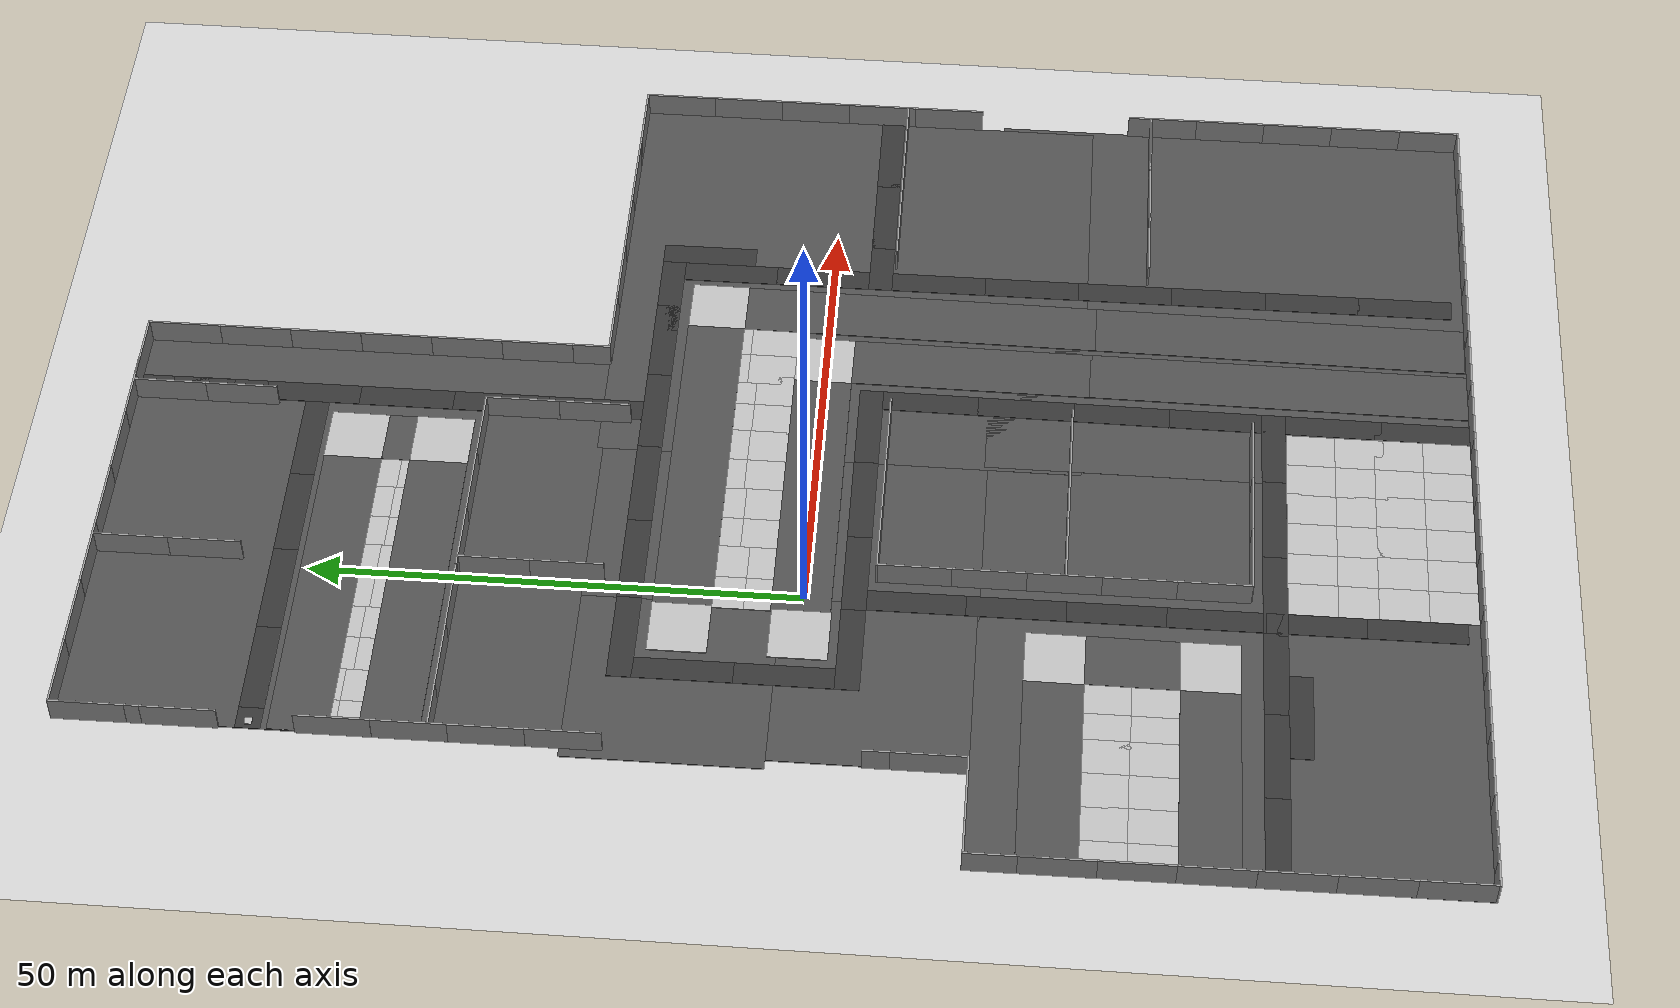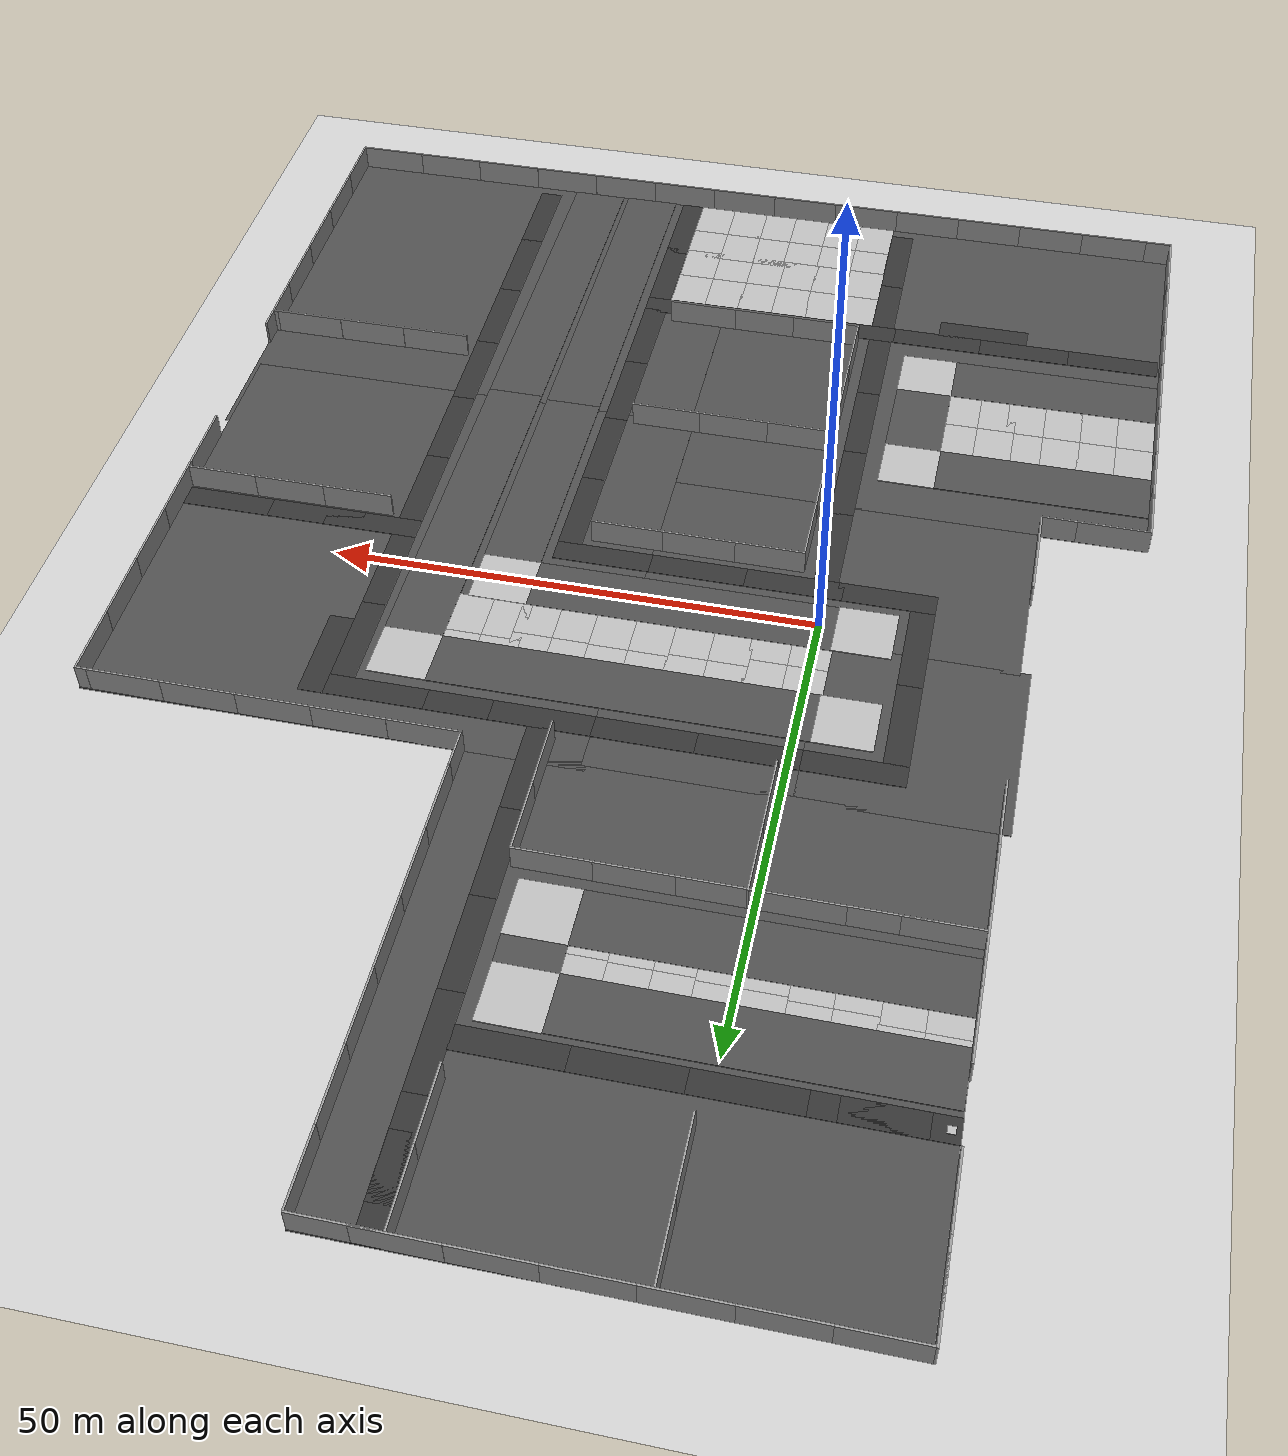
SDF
<sdf version="1.7">
 <world name="default">
  <plugin name="gazebo_ros_state" filename="libgazebo_ros_state.so">
   <ros>
    <namespace>/demo</namespace>
    <remapping>model_states:=model_states_demo</remapping>
    <remapping>link_states:=link_states_demo</remapping>
   </ros>
   <update_rate>1.0</update_rate>
  </plugin>
  <model name="ground_plane">
   <static>1</static>
   <link name="link">
    <collision name="collision">
     <geometry><plane><normal>0 0 1</normal><size>100 100</size></plane></geometry>
     <surface><friction><ode><mu>100</mu><mu2>50</mu2></ode></friction></surface>
    </collision>
    <visual name="visual">
     <cast_shadows>0</cast_shadows>
     <geometry><plane><normal>0 0 1</normal><size>100 100</size></plane></geometry>
     <material>
      <script><uri>file://media/materials/scripts/gazebo.material</uri><name>Gazebo/Grey</name></script>
     </material>
    </visual>
   </link>
  </model>
  <model name="asphalt_plane">
   <static>1</static>
   <link name="link">
    <collision name="collision">
     <geometry><box><size>20 20 0.1</size></box></geometry>
     <surface><friction><ode><mu>100</mu><mu2>50</mu2></ode></friction></surface>
    </collision>
    <visual name="visual">
     <cast_shadows>0</cast_shadows>
     <geometry><box><size>20 20 0.1</size></box></geometry>
     <material>
      <script>
       <uri>model://asphalt_plane/materials/scripts</uri>
       <uri>model://asphalt_plane/materials/textures</uri>
       <name>vrc/asphalt</name>
      </script>
     </material>
    </visual>
   </link>
   <pose>-10.1692 -7.43707 0 0 -0 0</pose>
  </model>
  <model name="asphalt_plane_clone">
   <static>1</static>
   <link name="link">
    <collision name="collision">
     <geometry><box><size>20 20 0.1</size></box></geometry>
     <surface><friction><ode><mu>100</mu><mu2>50</mu2></ode></friction></surface>
    </collision>
    <visual name="visual">
     <cast_shadows>0</cast_shadows>
     <geometry><box><size>20 20 0.1</size></box></geometry>
     <material>
      <script>
       <uri>model://asphalt_plane/materials/scripts</uri>
       <uri>model://asphalt_plane/materials/textures</uri>
       <name>vrc/asphalt</name>
      </script>
     </material>
    </visual>
   </link>
   <pose>-11.1971 12.1802 0 0 -0 0</pose>
  </model>
  <model name="asphalt_plane_clone_clone">
   <static>1</static>
   <link name="link">
    <collision name="collision">
     <geometry><box><size>20 20 0.1</size></box></geometry>
     <surface><friction><ode><mu>100</mu><mu2>50</mu2></ode></friction></surface>
    </collision>
    <visual name="visual">
     <cast_shadows>0</cast_shadows>
     <geometry><box><size>20 20 0.1</size></box></geometry>
     <material>
      <script>
       <uri>model://asphalt_plane/materials/scripts</uri>
       <uri>model://asphalt_plane/materials/textures</uri>
       <name>vrc/asphalt</name>
      </script>
     </material>
    </visual>
   </link>
   <pose>8.71597 12.1785 0 0 -0 0</pose>
  </model>
  <model name="asphalt_plane_clone_clone_0">
   <static>1</static>
   <link name="link">
    <collision name="collision">
     <geometry><box><size>20 20 0.1</size></box></geometry>
     <surface><friction><ode><mu>100</mu><mu2>50</mu2></ode></friction></surface>
    </collision>
    <visual name="visual">
     <cast_shadows>0</cast_shadows>
     <geometry><box><size>20 20 0.1</size></box></geometry>
     <material>
      <script>
       <uri>model://asphalt_plane/materials/scripts</uri>
       <uri>model://asphalt_plane/materials/textures</uri>
       <name>vrc/asphalt</name>
      </script>
     </material>
    </visual>
   </link>
   <pose>8.27987 -7.58982 0 0 -0 0</pose>
  </model>
  <model name="grey_wall_clone">
   <static>1</static>
   <link name="link">
    <pose>0 0 1.4 0 -0 0</pose>
    <collision name="collision"><geometry><box><size>7.5 0.2 2.8</size></box></geometry></collision>
    <visual name="visual">
     <cast_shadows>0</cast_shadows>
     <geometry><box><size>7.5 0.2 2.8</size></box></geometry>
     <material>
      <script>
       <uri>model://grey_wall/materials/scripts</uri>
       <uri>model://grey_wall/materials/textures</uri>
       <name>vrc/grey_wall</name>
      </script>
     </material>
    </visual>
   </link>
   <pose>49.4295 -33.5823 0 0 -0 0</pose>
  </model>
  <light name="sun" type="directional">
   <pose>0 0 10 0 -0 0</pose>
   <diffuse>0.8 0.8 0.8 1</diffuse>
   <specular>0.2 0.2 0.2 1</specular>
   <attenuation>
    <range>1000</range>
    <constant>0.9</constant>
    <linear>0.01</linear>
    <quadratic>0.001</quadratic>
   </attenuation>
   <direction>-0.5 0.1 -0.9</direction>
   <spot><inner_angle>0</inner_angle><outer_angle>0</outer_angle><falloff>0</falloff></spot>
  </light>
  <gravity>0 0 -9.8</gravity>
  <magnetic_field>6e-06 2.3e-05 -4.2e-05</magnetic_field>
  <atmosphere type="adiabatic"/>
  <physics name="default_physics" default="0" type="ode">
   <max_step_size>0.001</max_step_size>
   <real_time_factor>1</real_time_factor>
   <real_time_update_rate>1000</real_time_update_rate>
  </physics>
  <scene><ambient>0.4 0.4 0.4 1</ambient><background>0.7 0.7 0.7 1</background><shadows>0</shadows></scene>
  <audio><device>default</device></audio>
  <spherical_coordinates>
   <surface_model>EARTH_WGS84</surface_model>
   <latitude_deg>47.8406</latitude_deg>
   <longitude_deg>10.6199</longitude_deg>
   <elevation>740</elevation>
   <heading_deg>180</heading_deg>
  </spherical_coordinates>
  <include>
   <uri>file:///home/dhaval_lad/dhaval_ws/src/Outdoor_navigation_decision_making/outdoor_robot_spawner/models/actor_1</uri>
  </include>
  <include>
   <uri>file:///home/dhaval_lad/dhaval_ws/src/Outdoor_navigation_decision_making/outdoor_robot_spawner/models/actor_2</uri>
  </include>
  <model name="side walk">
   <pose>13.7924 17.3826 0 0 -0 0</pose>
   <static>1</static>
   <link name="link">
    <visual name="visual">
     <pose>0 0 0.05 0 -0 0</pose>
     <geometry><box><size>10 2.5 0.1</size></box></geometry>
     <material><ambient>0.2 0.2 0.2 1</ambient></material>
    </visual>
    <collision name="collision">
     <pose>0 0 0.05 0 -0 0</pose>
     <geometry><box><size>10 2.5 0.1</size></box></geometry>
    </collision>
   </link>
  </model>
  <model name="side walk_clone">
   <pose>3.79611 17.3771 0 0 -0 0</pose>
   <static>1</static>
   <link name="link">
    <visual name="visual">
     <pose>0 0 0.05 0 -0 0</pose>
     <geometry><box><size>10 2.5 0.1</size></box></geometry>
     <material><ambient>0.2 0.2 0.2 1</ambient></material>
    </visual>
    <collision name="collision">
     <pose>0 0 0.05 0 -0 0</pose>
     <geometry><box><size>10 2.5 0.1</size></box></geometry>
    </collision>
   </link>
  </model>
  <model name="side walk_clone_0">
   <pose>-6.19156 17.3637 0 0 -0 0</pose>
   <static>1</static>
   <link name="link">
    <visual name="visual">
     <pose>0 0 0.05 0 -0 0</pose>
     <geometry><box><size>10 2.5 0.1</size></box></geometry>
     <material><ambient>0.2 0.2 0.2 1</ambient></material>
    </visual>
    <collision name="collision">
     <pose>0 0 0.05 0 -0 0</pose>
     <geometry><box><size>10 2.5 0.1</size></box></geometry>
    </collision>
   </link>
  </model>
  <model name="side walk_clone_1">
   <pose>-9.91314 11.1641 0 0 0 -1.5667</pose>
   <static>1</static>
   <link name="link">
    <visual name="visual">
     <pose>0 0 0.05 0 -0 0</pose>
     <geometry><box><size>10 2.5 0.1</size></box></geometry>
     <material><ambient>0.2 0.2 0.2 1</ambient></material>
    </visual>
    <collision name="collision">
     <pose>0 0 0.05 0 -0 0</pose>
     <geometry><box><size>10 2.5 0.1</size></box></geometry>
    </collision>
   </link>
  </model>
  <model name="side walk_clone_1_clone">
   <pose>-9.88629 1.1782 0 0 0 -1.56946</pose>
   <static>1</static>
   <link name="link">
    <visual name="visual">
     <pose>0 0 0.05 0 -0 0</pose>
     <geometry><box><size>10 2.5 0.1</size></box></geometry>
     <material><ambient>0.2 0.2 0.2 1</ambient></material>
    </visual>
    <collision name="collision">
     <pose>0 0 0.05 0 -0 0</pose>
     <geometry><box><size>10 2.5 0.1</size></box></geometry>
    </collision>
   </link>
  </model>
  <model name="side walk_clone_0_clone">
   <pose>-6.1264 -5.0705 0 0 -0 0</pose>
   <static>1</static>
   <link name="link">
    <visual name="visual">
     <pose>0 0 0.05 0 -0 0</pose>
     <geometry><box><size>10 2.5 0.1</size></box></geometry>
     <material><ambient>0.2 0.2 0.2 1</ambient></material>
    </visual>
    <collision name="collision">
     <pose>0 0 0.05 0 -0 0</pose>
     <geometry><box><size>10 2.5 0.1</size></box></geometry>
    </collision>
   </link>
  </model>
  <model name="side walk_clone_0_clone_0">
   <pose>3.31852 -5.07088 0 0 -0 0</pose>
   <static>1</static>
   <link name="link">
    <visual name="visual">
     <pose>0 0 0.05 0 -0 0</pose>
     <geometry><box><size>10 2.5 0.1</size></box></geometry>
     <material><ambient>0.2 0.2 0.2 1</ambient></material>
    </visual>
    <collision name="collision">
     <pose>0 0 0.05 0 -0 0</pose>
     <geometry><box><size>10 2.5 0.1</size></box></geometry>
    </collision>
   </link>
  </model>
  <model name="side walk_clone_1_clone_clone">
   <pose>0.222815 -11.3123 0 0 0 -1.5667</pose>
   <static>1</static>
   <link name="link">
    <visual name="visual">
     <pose>0 0 0.05 0 -0 0</pose>
     <geometry><box><size>10 2.5 0.1</size></box></geometry>
     <material><ambient>0.2 0.2 0.2 1</ambient></material>
    </visual>
    <collision name="collision">
     <pose>0 0 0.05 0 -0 0</pose>
     <geometry><box><size>10 2.5 0.1</size></box></geometry>
    </collision>
   </link>
  </model>
  <model name="side walk_clone_0_clone_clone">
   <pose>13.2672 -5.07602 0 0 -0 0</pose>
   <static>1</static>
   <link name="link">
    <visual name="visual">
     <pose>0 0 0.05 0 -0 0</pose>
     <geometry><box><size>10 2.5 0.1</size></box></geometry>
     <material><ambient>0.2 0.2 0.2 1</ambient></material>
    </visual>
    <collision name="collision">
     <pose>0 0 0.05 0 -0 0</pose>
     <geometry><box><size>10 2.5 0.1</size></box></geometry>
    </collision>
   </link>
  </model>
  <model name="asphalt_plane_0">
   <static>1</static>
   <link name="link">
    <collision name="collision"><geometry><box><size>50 50 0.1</size></box></geometry></collision>
    <visual name="visual">
     <cast_shadows>0</cast_shadows>
     <geometry><box><size>50 50 0.1</size></box></geometry>
     <material>
      <script>
       <uri>model://asphalt_plane/materials/scripts</uri>
       <uri>model://asphalt_plane/materials/textures</uri>
       <name>vrc/asphalt</name>
      </script>
     </material>
    </visual>
   </link>
   <pose>-6.22709 -42.2685 -0.007309 0 -0 0</pose>
  </model>
  <model name="asphalt_plane_0_clone">
   <static>1</static>
   <link name="link">
    <collision name="collision"><geometry><box><size>50 50 0.1</size></box></geometry></collision>
    <visual name="visual">
     <cast_shadows>0</cast_shadows>
     <geometry><box><size>50 50 0.1</size></box></geometry>
     <material>
      <script>
       <uri>model://asphalt_plane/materials/scripts</uri>
       <uri>model://asphalt_plane/materials/textures</uri>
       <name>vrc/asphalt</name>
      </script>
     </material>
    </visual>
   </link>
   <pose>43.2053 -2.21198 0 0 -0 0</pose>
  </model>
  <model name="asphalt_plane_0_clone_clone">
   <static>1</static>
   <link name="link">
    <collision name="collision"><geometry><box><size>50 50 0.1</size></box></geometry></collision>
    <visual name="visual">
     <cast_shadows>0</cast_shadows>
     <geometry><box><size>50 50 0.1</size></box></geometry>
     <material>
      <script>
       <uri>model://asphalt_plane/materials/scripts</uri>
       <uri>model://asphalt_plane/materials/textures</uri>
       <name>vrc/asphalt</name>
      </script>
     </material>
    </visual>
   </link>
   <pose>4.81 46.7209 0 0 -0 0</pose>
  </model>
  <model name="side walk_clone_2">
   <pose>23.7417 17.3764 0 0 -0 0</pose>
   <static>1</static>
   <link name="link">
    <visual name="visual">
     <pose>0 0 0.05 0 -0 0</pose>
     <geometry><box><size>10 2.5 0.1</size></box></geometry>
     <material><ambient>0.2 0.2 0.2 1</ambient></material>
    </visual>
    <collision name="collision">
     <pose>0 0 0.05 0 -0 0</pose>
     <geometry><box><size>10 2.5 0.1</size></box></geometry>
    </collision>
   </link>
  </model>
  <model name="side walk_clone_3">
   <pose>33.7384 17.3743 0 0 -0 0</pose>
   <static>1</static>
   <link name="link">
    <visual name="visual">
     <pose>0 0 0.05 0 -0 0</pose>
     <geometry><box><size>10 2.5 0.1</size></box></geometry>
     <material><ambient>0.2 0.2 0.2 1</ambient></material>
    </visual>
    <collision name="collision">
     <pose>0 0 0.05 0 -0 0</pose>
     <geometry><box><size>10 2.5 0.1</size></box></geometry>
    </collision>
   </link>
  </model>
  <model name="side walk_clone_1_clone_clone_clone">
   <pose>23.5717 23.5135 0 0 0 -1.5667</pose>
   <static>1</static>
   <link name="link">
    <visual name="visual">
     <pose>0 0 0.05 0 -0 0</pose>
     <geometry><box><size>10 2.5 0.1</size></box></geometry>
     <material><ambient>0.2 0.2 0.2 1</ambient></material>
    </visual>
    <collision name="collision">
     <pose>0 0 0.05 0 -0 0</pose>
     <geometry><box><size>10 2.5 0.1</size></box></geometry>
    </collision>
   </link>
  </model>
  <model name="side walk_clone_1_clone_clone_clone_0">
   <pose>23.5407 33.4582 0 0 0 -1.5667</pose>
   <static>1</static>
   <link name="link">
    <visual name="visual">
     <pose>0 0 0.05 0 -0 0</pose>
     <geometry><box><size>10 2.5 0.1</size></box></geometry>
     <material><ambient>0.2 0.2 0.2 1</ambient></material>
    </visual>
    <collision name="collision">
     <pose>0 0 0.05 0 -0 0</pose>
     <geometry><box><size>10 2.5 0.1</size></box></geometry>
    </collision>
   </link>
  </model>
  <model name="side walk_clone_1_clone_clone_clone_1">
   <pose>23.5123 43.4347 0 0 0 -1.5667</pose>
   <static>1</static>
   <link name="link">
    <visual name="visual">
     <pose>0 0 0.05 0 -0 0</pose>
     <geometry><box><size>10 2.5 0.1</size></box></geometry>
     <material><ambient>0.2 0.2 0.2 1</ambient></material>
    </visual>
    <collision name="collision">
     <pose>0 0 0.05 0 -0 0</pose>
     <geometry><box><size>10 2.5 0.1</size></box></geometry>
    </collision>
   </link>
  </model>
  <model name="side walk_clone_1_clone_clone_clone_2">
   <pose>23.482 53.3149 0 0 0 -1.5667</pose>
   <static>1</static>
   <link name="link">
    <visual name="visual">
     <pose>0 0 0.05 0 -0 0</pose>
     <geometry><box><size>10 2.5 0.1</size></box></geometry>
     <material><ambient>0.2 0.2 0.2 1</ambient></material>
    </visual>
    <collision name="collision">
     <pose>0 0 0.05 0 -0 0</pose>
     <geometry><box><size>10 2.5 0.1</size></box></geometry>
    </collision>
   </link>
  </model>
  <model name="side walk_clone_1_clone_clone_clone_clone">
   <pose>0.256591 -21.2274 0 0 0 -1.5667</pose>
   <static>1</static>
   <link name="link">
    <visual name="visual">
     <pose>0 0 0.05 0 -0 0</pose>
     <geometry><box><size>10 2.5 0.1</size></box></geometry>
     <material><ambient>0.2 0.2 0.2 1</ambient></material>
    </visual>
    <collision name="collision">
     <pose>0 0 0.05 0 -0 0</pose>
     <geometry><box><size>10 2.5 0.1</size></box></geometry>
    </collision>
   </link>
  </model>
  <model name="side walk_clone_1_clone_clone_clone_clone_0">
   <pose>0.290651 -31.2092 0 0 0 -1.5667</pose>
   <static>1</static>
   <link name="link">
    <visual name="visual">
     <pose>0 0 0.05 0 -0 0</pose>
     <geometry><box><size>10 2.5 0.1</size></box></geometry>
     <material><ambient>0.2 0.2 0.2 1</ambient></material>
    </visual>
    <collision name="collision">
     <pose>0 0 0.05 0 -0 0</pose>
     <geometry><box><size>10 2.5 0.1</size></box></geometry>
    </collision>
   </link>
  </model>
  <model name="side walk_clone_0_clone_clone_clone">
   <pose>23.1677 -5.07058 0 0 -0 0</pose>
   <static>1</static>
   <link name="link">
    <visual name="visual">
     <pose>0 0 0.05 0 -0 0</pose>
     <geometry><box><size>10 2.5 0.1</size></box></geometry>
     <material><ambient>0.2 0.2 0.2 1</ambient></material>
    </visual>
    <collision name="collision">
     <pose>0 0 0.05 0 -0 0</pose>
     <geometry><box><size>10 2.5 0.1</size></box></geometry>
    </collision>
   </link>
  </model>
  <model name="side walk_clone_1_clone_clone_clone_clone_1">
   <pose>43.9499 11.1428 0 0 0 -1.5667</pose>
   <static>1</static>
   <link name="link">
    <visual name="visual">
     <pose>0 0 0.05 0 -0 0</pose>
     <geometry><box><size>10 2.5 0.1</size></box></geometry>
     <material><ambient>0.2 0.2 0.2 1</ambient></material>
    </visual>
    <collision name="collision">
     <pose>0 0 0.05 0 -0 0</pose>
     <geometry><box><size>10 2.5 0.1</size></box></geometry>
    </collision>
   </link>
  </model>
  <model name="side walk_clone_1_clone_clone_clone_clone_2">
   <pose>43.9881 1.1868 0 0 0 -1.5667</pose>
   <static>1</static>
   <link name="link">
    <visual name="visual">
     <pose>0 0 0.05 0 -0 0</pose>
     <geometry><box><size>10 2.5 0.1</size></box></geometry>
     <material><ambient>0.2 0.2 0.2 1</ambient></material>
    </visual>
    <collision name="collision">
     <pose>0 0 0.05 0 -0 0</pose>
     <geometry><box><size>10 2.5 0.1</size></box></geometry>
    </collision>
   </link>
  </model>
  <model name="side walk_clone_0_clone_clone_clone_0_clone_clone">
   <pose>53.9006 -4.98965 0 0 -0 0</pose>
   <static>1</static>
   <link name="link">
    <visual name="visual">
     <pose>0 0 0.05 0 -0 0</pose>
     <geometry><box><size>10 2.5 0.1</size></box></geometry>
     <material><ambient>0.2 0.2 0.2 1</ambient></material>
    </visual>
    <collision name="collision">
     <pose>0 0 0.05 0 -0 0</pose>
     <geometry><box><size>10 2.5 0.1</size></box></geometry>
    </collision>
   </link>
  </model>
  <model name="side walk_clone_0_clone_clone_clone_0_clone_clone_0">
   <pose>63.3362 -4.96787 0 0 -0 0</pose>
   <static>1</static>
   <link name="link">
    <visual name="visual">
     <pose>0 0 0.05 0 -0 0</pose>
     <geometry><box><size>10 2.5 0.1</size></box></geometry>
     <material><ambient>0.2 0.2 0.2 1</ambient></material>
    </visual>
    <collision name="collision">
     <pose>0 0 0.05 0 -0 0</pose>
     <geometry><box><size>10 2.5 0.1</size></box></geometry>
    </collision>
   </link>
  </model>
  <model name="side walk_clone_1_clone_clone_clone_2_clone">
   <pose>23.4414 63.1752 0 0 0 -1.5667</pose>
   <static>1</static>
   <link name="link">
    <visual name="visual">
     <pose>0 0 0.05 0 -0 0</pose>
     <geometry><box><size>10 2.5 0.1</size></box></geometry>
     <material><ambient>0.2 0.2 0.2 1</ambient></material>
    </visual>
    <collision name="collision">
     <pose>0 0 0.05 0 -0 0</pose>
     <geometry><box><size>10 2.5 0.1</size></box></geometry>
    </collision>
   </link>
  </model>
  <model name="side walk_clone_1_clone_clone_clone_2_clone_0">
   <pose>23.4031 66.7362 0 0 0 -1.5667</pose>
   <static>1</static>
   <link name="link">
    <visual name="visual">
     <pose>0 0 0.05 0 -0 0</pose>
     <geometry><box><size>10 2.5 0.1</size></box></geometry>
     <material><ambient>0.2 0.2 0.2 1</ambient></material>
    </visual>
    <collision name="collision">
     <pose>0 0 0.05 0 -0 0</pose>
     <geometry><box><size>10 2.5 0.1</size></box></geometry>
    </collision>
   </link>
  </model>
  <model name="grey_wall_clone_clone">
   <static>1</static>
   <link name="link">
    <pose>0 0 1.4 0 -0 0</pose>
    <collision name="collision"><geometry><box><size>7.5 0.2 2.8</size></box></geometry></collision>
    <visual name="visual">
     <cast_shadows>0</cast_shadows>
     <geometry><box><size>7.5 0.2 2.8</size></box></geometry>
     <material>
      <script>
       <uri>model://grey_wall/materials/scripts</uri>
       <uri>model://grey_wall/materials/textures</uri>
       <name>vrc/grey_wall</name>
      </script>
     </material>
    </visual>
   </link>
   <pose>0.663264 23.7766 0 0 0 -1.56776</pose>
  </model>
  <model name="side walk_clone_4_clone">
   <pose>17.2612 52.615 0 0 -0 0</pose>
   <static>1</static>
   <link name="link">
    <visual name="visual">
     <pose>0 0 0.05 0 -0 0</pose>
     <geometry><box><size>10 2.5 0.1</size></box></geometry>
     <material><ambient>0.2 0.2 0.2 1</ambient></material>
    </visual>
    <collision name="collision">
     <pose>0 0 0.05 0 -0 0</pose>
     <geometry><box><size>10 2.5 0.1</size></box></geometry>
    </collision>
   </link>
  </model>
  <model name="side walk_clone_4_clone_0">
   <pose>7.25478 52.6157 0 0 -0 0</pose>
   <static>1</static>
   <link name="link">
    <visual name="visual">
     <pose>0 0 0.05 0 -0 0</pose>
     <geometry><box><size>10 2.5 0.1</size></box></geometry>
     <material><ambient>0.2 0.2 0.2 1</ambient></material>
    </visual>
    <collision name="collision">
     <pose>0 0 0.05 0 -0 0</pose>
     <geometry><box><size>10 2.5 0.1</size></box></geometry>
    </collision>
   </link>
  </model>
  <model name="side walk_clone_4_clone_1">
   <pose>-2.73893 52.607 0 0 -0 0</pose>
   <static>1</static>
   <link name="link">
    <visual name="visual">
     <pose>0 0 0.05 0 -0 0</pose>
     <geometry><box><size>10 2.5 0.1</size></box></geometry>
     <material><ambient>0.2 0.2 0.2 1</ambient></material>
    </visual>
    <collision name="collision">
     <pose>0 0 0.05 0 -0 0</pose>
     <geometry><box><size>10 2.5 0.1</size></box></geometry>
    </collision>
   </link>
  </model>
  <model name="side walk_clone_4_clone_2">
   <pose>-12.7156 52.6002 0 0 -0 0</pose>
   <static>1</static>
   <link name="link">
    <visual name="visual">
     <pose>0 0 0.05 0 -0 0</pose>
     <geometry><box><size>10 2.5 0.1</size></box></geometry>
     <material><ambient>0.2 0.2 0.2 1</ambient></material>
    </visual>
    <collision name="collision">
     <pose>0 0 0.05 0 -0 0</pose>
     <geometry><box><size>10 2.5 0.1</size></box></geometry>
    </collision>
   </link>
  </model>
  <model name="grey_wall_clone_clone_clone">
   <static>1</static>
   <link name="link">
    <pose>0 0 1.4 0 -0 0</pose>
    <collision name="collision"><geometry><box><size>7.5 0.2 2.8</size></box></geometry></collision>
    <visual name="visual">
     <cast_shadows>0</cast_shadows>
     <geometry><box><size>7.5 0.2 2.8</size></box></geometry>
     <material>
      <script>
       <uri>model://grey_wall/materials/scripts</uri>
       <uri>model://grey_wall/materials/textures</uri>
       <name>vrc/grey_wall</name>
      </script>
     </material>
    </visual>
   </link>
   <pose>0.641842 31.1008 0 0 0 -1.56776</pose>
  </model>
  <model name="grey_wall_clone_clone_clone_0">
   <static>1</static>
   <link name="link">
    <pose>0 0 1.4 0 -0 0</pose>
    <collision name="collision"><geometry><box><size>7.5 0.2 2.8</size></box></geometry></collision>
    <visual name="visual">
     <cast_shadows>0</cast_shadows>
     <geometry><box><size>7.5 0.2 2.8</size></box></geometry>
     <material>
      <script>
       <uri>model://grey_wall/materials/scripts</uri>
       <uri>model://grey_wall/materials/textures</uri>
       <name>vrc/grey_wall</name>
      </script>
     </material>
    </visual>
   </link>
   <pose>0.782654 60.3851 0 0 0 -1.56776</pose>
  </model>
  <model name="grey_wall_clone_clone_clone_1">
   <static>1</static>
   <link name="link">
    <pose>0 0 1.4 0 -0 0</pose>
    <collision name="collision"><geometry><box><size>7.5 0.2 2.8</size></box></geometry></collision>
    <visual name="visual">
     <cast_shadows>0</cast_shadows>
     <geometry><box><size>7.5 0.2 2.8</size></box></geometry>
     <material>
      <script>
       <uri>model://grey_wall/materials/scripts</uri>
       <uri>model://grey_wall/materials/textures</uri>
       <name>vrc/grey_wall</name>
      </script>
     </material>
    </visual>
   </link>
   <pose>0.745884 67.8409 0 0 0 -1.56776</pose>
  </model>
  <model name="grey_wall_clone_clone_clone_2">
   <static>1</static>
   <link name="link">
    <pose>0 0 1.4 0 -0 0</pose>
    <collision name="collision"><geometry><box><size>7.5 0.2 2.8</size></box></geometry></collision>
    <visual name="visual">
     <cast_shadows>0</cast_shadows>
     <geometry><box><size>7.5 0.2 2.8</size></box></geometry>
     <material>
      <script>
       <uri>model://grey_wall/materials/scripts</uri>
       <uri>model://grey_wall/materials/textures</uri>
       <name>vrc/grey_wall</name>
      </script>
     </material>
    </visual>
   </link>
   <pose>-4.2983 34.7434 0 0 -0 3.13795</pose>
  </model>
  <model name="grey_wall_clone_clone_clone_2_clone">
   <static>1</static>
   <link name="link">
    <pose>0 0 1.4 0 -0 0</pose>
    <collision name="collision"><geometry><box><size>7.5 0.2 2.8</size></box></geometry></collision>
    <visual name="visual">
     <cast_shadows>0</cast_shadows>
     <geometry><box><size>7.5 0.2 2.8</size></box></geometry>
     <material>
      <script>
       <uri>model://grey_wall/materials/scripts</uri>
       <uri>model://grey_wall/materials/textures</uri>
       <name>vrc/grey_wall</name>
      </script>
     </material>
    </visual>
   </link>
   <pose>-11.7464 34.7461 0 0 -0 3.13795</pose>
  </model>
  <model name="grey_wall_clone_clone_clone_2_clone_0">
   <static>1</static>
   <link name="link">
    <pose>0 0 1.4 0 -0 0</pose>
    <collision name="collision"><geometry><box><size>7.5 0.2 2.8</size></box></geometry></collision>
    <visual name="visual">
     <cast_shadows>0</cast_shadows>
     <geometry><box><size>7.5 0.2 2.8</size></box></geometry>
     <material>
      <script>
       <uri>model://grey_wall/materials/scripts</uri>
       <uri>model://grey_wall/materials/textures</uri>
       <name>vrc/grey_wall</name>
      </script>
     </material>
    </visual>
   </link>
   <pose>-16.4804 34.7656 0 0 -0 3.13795</pose>
  </model>
  <model name="grey_wall_clone_clone_clone_2_clone_1">
   <static>1</static>
   <link name="link">
    <pose>0 0 1.4 0 -0 0</pose>
    <collision name="collision"><geometry><box><size>7.5 0.2 2.8</size></box></geometry></collision>
    <visual name="visual">
     <cast_shadows>0</cast_shadows>
     <geometry><box><size>7.5 0.2 2.8</size></box></geometry>
     <material>
      <script>
       <uri>model://grey_wall/materials/scripts</uri>
       <uri>model://grey_wall/materials/textures</uri>
       <name>vrc/grey_wall</name>
      </script>
     </material>
    </visual>
   </link>
   <pose>3.28789 34.7184 0 0 -0 3.13795</pose>
  </model>
  <model name="grey_wall_clone_clone_clone_2_clone_2">
   <static>1</static>
   <link name="link">
    <pose>0 0 1.4 0 -0 0</pose>
    <collision name="collision"><geometry><box><size>7.5 0.2 2.8</size></box></geometry></collision>
    <visual name="visual">
     <cast_shadows>0</cast_shadows>
     <geometry><box><size>7.5 0.2 2.8</size></box></geometry>
     <material>
      <script>
       <uri>model://grey_wall/materials/scripts</uri>
       <uri>model://grey_wall/materials/textures</uri>
       <name>vrc/grey_wall</name>
      </script>
     </material>
    </visual>
   </link>
   <pose>10.7527 34.6951 0 0 -0 3.13795</pose>
  </model>
  <model name="grey_wall_clone_clone_clone_2_clone_3">
   <static>1</static>
   <link name="link">
    <pose>0 0 1.4 0 -0 0</pose>
    <collision name="collision"><geometry><box><size>7.5 0.2 2.8</size></box></geometry></collision>
    <visual name="visual">
     <cast_shadows>0</cast_shadows>
     <geometry><box><size>7.5 0.2 2.8</size></box></geometry>
     <material>
      <script>
       <uri>model://grey_wall/materials/scripts</uri>
       <uri>model://grey_wall/materials/textures</uri>
       <name>vrc/grey_wall</name>
      </script>
     </material>
    </visual>
   </link>
   <pose>18.2492 34.6563 0 0 -0 3.13795</pose>
  </model>
  <model name="grey_wall_clone_clone_clone_clone">
   <static>1</static>
   <link name="link">
    <pose>0 0 1.4 0 -0 0</pose>
    <collision name="collision"><geometry><box><size>7.5 0.2 2.8</size></box></geometry></collision>
    <visual name="visual">
     <cast_shadows>0</cast_shadows>
     <geometry><box><size>7.5 0.2 2.8</size></box></geometry>
     <material>
      <script>
       <uri>model://grey_wall/materials/scripts</uri>
       <uri>model://grey_wall/materials/textures</uri>
       <name>vrc/grey_wall</name>
      </script>
     </material>
    </visual>
   </link>
   <pose>21.9008 30.8248 0 0 0 -1.56776</pose>
  </model>
  <model name="grey_wall_clone_clone_clone_clone_0">
   <static>1</static>
   <link name="link">
    <pose>0 0 1.4 0 -0 0</pose>
    <collision name="collision"><geometry><box><size>7.5 0.2 2.8</size></box></geometry></collision>
    <visual name="visual">
     <cast_shadows>0</cast_shadows>
     <geometry><box><size>7.5 0.2 2.8</size></box></geometry>
     <material>
      <script>
       <uri>model://grey_wall/materials/scripts</uri>
       <uri>model://grey_wall/materials/textures</uri>
       <name>vrc/grey_wall</name>
      </script>
     </material>
    </visual>
   </link>
   <pose>21.932 23.3788 0 0 0 -1.56776</pose>
  </model>
  <model name="grey_wall_clone_clone_clone_2_clone_0_clone">
   <static>1</static>
   <link name="link">
    <pose>0 0 1.4 0 -0 0</pose>
    <collision name="collision"><geometry><box><size>7.5 0.2 2.8</size></box></geometry></collision>
    <visual name="visual">
     <cast_shadows>0</cast_shadows>
     <geometry><box><size>7.5 0.2 2.8</size></box></geometry>
     <material>
      <script>
       <uri>model://grey_wall/materials/scripts</uri>
       <uri>model://grey_wall/materials/textures</uri>
       <name>vrc/grey_wall</name>
      </script>
     </material>
    </visual>
   </link>
   <pose>-16.4775 71.7397 0 0 -0 3.13795</pose>
  </model>
  <model name="grey_wall_clone_clone_clone_2_clone_0_clone_0">
   <static>1</static>
   <link name="link">
    <pose>0 0 1.4 0 -0 0</pose>
    <collision name="collision"><geometry><box><size>7.5 0.2 2.8</size></box></geometry></collision>
    <visual name="visual">
     <cast_shadows>0</cast_shadows>
     <geometry><box><size>7.5 0.2 2.8</size></box></geometry>
     <material>
      <script>
       <uri>model://grey_wall/materials/scripts</uri>
       <uri>model://grey_wall/materials/textures</uri>
       <name>vrc/grey_wall</name>
      </script>
     </material>
    </visual>
   </link>
   <pose>-9.07049 71.7023 0 0 -0 3.13795</pose>
  </model>
  <model name="grey_wall_clone_clone_clone_2_clone_0_clone_1">
   <static>1</static>
   <link name="link">
    <pose>0 0 1.4 0 -0 0</pose>
    <collision name="collision"><geometry><box><size>7.5 0.2 2.8</size></box></geometry></collision>
    <visual name="visual">
     <cast_shadows>0</cast_shadows>
     <geometry><box><size>7.5 0.2 2.8</size></box></geometry>
     <material>
      <script>
       <uri>model://grey_wall/materials/scripts</uri>
       <uri>model://grey_wall/materials/textures</uri>
       <name>vrc/grey_wall</name>
      </script>
     </material>
    </visual>
   </link>
   <pose>-1.64416 71.6785 0 0 -0 3.13795</pose>
  </model>
  <model name="grey_wall_clone_clone_clone_2_clone_0_clone_2">
   <static>1</static>
   <link name="link">
    <pose>0 0 1.4 0 -0 0</pose>
    <collision name="collision"><geometry><box><size>7.5 0.2 2.8</size></box></geometry></collision>
    <visual name="visual">
     <cast_shadows>0</cast_shadows>
     <geometry><box><size>7.5 0.2 2.8</size></box></geometry>
     <material>
      <script>
       <uri>model://grey_wall/materials/scripts</uri>
       <uri>model://grey_wall/materials/textures</uri>
       <name>vrc/grey_wall</name>
      </script>
     </material>
    </visual>
   </link>
   <pose>5.83626 71.649 0 0 -0 3.13795</pose>
  </model>
  <model name="grey_wall_clone_clone_clone_2_clone_0_clone_3">
   <static>1</static>
   <link name="link">
    <pose>0 0 1.4 0 -0 0</pose>
    <collision name="collision"><geometry><box><size>7.5 0.2 2.8</size></box></geometry></collision>
    <visual name="visual">
     <cast_shadows>0</cast_shadows>
     <geometry><box><size>7.5 0.2 2.8</size></box></geometry>
     <material>
      <script>
       <uri>model://grey_wall/materials/scripts</uri>
       <uri>model://grey_wall/materials/textures</uri>
       <name>vrc/grey_wall</name>
      </script>
     </material>
    </visual>
   </link>
   <pose>13.3382 71.616 0 0 -0 3.13795</pose>
  </model>
  <model name="grey_wall_clone_clone_clone_2_clone_0_clone_4">
   <static>1</static>
   <link name="link">
    <pose>0 0 1.4 0 -0 0</pose>
    <collision name="collision"><geometry><box><size>7.5 0.2 2.8</size></box></geometry></collision>
    <visual name="visual">
     <cast_shadows>0</cast_shadows>
     <geometry><box><size>7.5 0.2 2.8</size></box></geometry>
     <material>
      <script>
       <uri>model://grey_wall/materials/scripts</uri>
       <uri>model://grey_wall/materials/textures</uri>
       <name>vrc/grey_wall</name>
      </script>
     </material>
    </visual>
   </link>
   <pose>20.8292 71.5956 0 0 -0 3.13795</pose>
  </model>
  <model name="grey_wall_clone_clone_clone_2_clone_0_clone_5">
   <static>1</static>
   <link name="link">
    <pose>0 0 1.4 0 -0 0</pose>
    <collision name="collision"><geometry><box><size>7.5 0.2 2.8</size></box></geometry></collision>
    <visual name="visual">
     <cast_shadows>0</cast_shadows>
     <geometry><box><size>7.5 0.2 2.8</size></box></geometry>
     <material>
      <script>
       <uri>model://grey_wall/materials/scripts</uri>
       <uri>model://grey_wall/materials/textures</uri>
       <name>vrc/grey_wall</name>
      </script>
     </material>
    </visual>
   </link>
   <pose>26.0628 71.555 0 0 -0 3.13795</pose>
  </model>
  <model name="side walk_clone_0_clone_clone_clone_0_clone_clone_3">
   <pose>3.83426 -46.9929 0 0 -0 0</pose>
   <static>1</static>
   <link name="link">
    <visual name="visual">
     <pose>0 0 0.05 0 -0 0</pose>
     <geometry><box><size>10 2.5 0.1</size></box></geometry>
     <material><ambient>0.2 0.2 0.2 1</ambient></material>
    </visual>
    <collision name="collision">
     <pose>0 0 0.05 0 -0 0</pose>
     <geometry><box><size>10 2.5 0.1</size></box></geometry>
    </collision>
   </link>
  </model>
  <model name="side walk_clone_0_clone_clone_clone_0_clone_clone_4">
   <pose>-5.93815 -47.0144 0 0 -0 0</pose>
   <static>1</static>
   <link name="link">
    <visual name="visual">
     <pose>0 0 0.05 0 -0 0</pose>
     <geometry><box><size>10 2.5 0.1</size></box></geometry>
     <material><ambient>0.2 0.2 0.2 1</ambient></material>
    </visual>
    <collision name="collision">
     <pose>0 0 0.05 0 -0 0</pose>
     <geometry><box><size>10 2.5 0.1</size></box></geometry>
    </collision>
   </link>
  </model>
  <model name="side walk_clone_0_clone_clone_clone_0_clone_clone_5">
   <pose>-15.9248 -47.0111 0 0 -0 0</pose>
   <static>1</static>
   <link name="link">
    <visual name="visual">
     <pose>0 0 0.05 0 -0 0</pose>
     <geometry><box><size>10 2.5 0.1</size></box></geometry>
     <material><ambient>0.2 0.2 0.2 1</ambient></material>
    </visual>
    <collision name="collision">
     <pose>0 0 0.05 0 -0 0</pose>
     <geometry><box><size>10 2.5 0.1</size></box></geometry>
    </collision>
   </link>
  </model>
  <model name="side walk_clone_0_clone_clone_clone_0_clone_clone_6">
   <pose>-25.9206 -47.0184 0 0 -0 0</pose>
   <static>1</static>
   <link name="link">
    <visual name="visual">
     <pose>0 0 0.05 0 -0 0</pose>
     <geometry><box><size>10 2.5 0.1</size></box></geometry>
     <material><ambient>0.2 0.2 0.2 1</ambient></material>
    </visual>
    <collision name="collision">
     <pose>0 0 0.05 0 -0 0</pose>
     <geometry><box><size>10 2.5 0.1</size></box></geometry>
    </collision>
   </link>
  </model>
  <model name="side walk_clone_0_clone_clone_clone_0_clone_clone_7">
   <pose>13.792 -46.9837 0 0 -0 0</pose>
   <static>1</static>
   <link name="link">
    <visual name="visual">
     <pose>0 0 0.05 0 -0 0</pose>
     <geometry><box><size>10 2.5 0.1</size></box></geometry>
     <material><ambient>0.2 0.2 0.2 1</ambient></material>
    </visual>
    <collision name="collision">
     <pose>0 0 0.05 0 -0 0</pose>
     <geometry><box><size>10 2.5 0.1</size></box></geometry>
    </collision>
   </link>
  </model>
  <model name="side walk_clone_1_clone_clone_clone_clone_0_clone">
   <pose>0.312658 -41.1369 0 0 0 -1.5667</pose>
   <static>1</static>
   <link name="link">
    <visual name="visual">
     <pose>0 0 0.05 0 -0 0</pose>
     <geometry><box><size>10 2.5 0.1</size></box></geometry>
     <material><ambient>0.2 0.2 0.2 1</ambient></material>
    </visual>
    <collision name="collision">
     <pose>0 0 0.05 0 -0 0</pose>
     <geometry><box><size>10 2.5 0.1</size></box></geometry>
    </collision>
   </link>
  </model>
  <model name="side walk_clone_1_clone_clone_clone_clone_0_clone_0">
   <pose>0.356942 -51.0999 0 0 0 -1.5667</pose>
   <static>1</static>
   <link name="link">
    <visual name="visual">
     <pose>0 0 0.05 0 -0 0</pose>
     <geometry><box><size>10 2.5 0.1</size></box></geometry>
     <material><ambient>0.2 0.2 0.2 1</ambient></material>
    </visual>
    <collision name="collision">
     <pose>0 0 0.05 0 -0 0</pose>
     <geometry><box><size>10 2.5 0.1</size></box></geometry>
    </collision>
   </link>
  </model>
  <model name="side walk_clone_1_clone_clone_clone_clone_0_clone_0_clone">
   <pose>0.402208 -61.0372 0 0 0 -1.5667</pose>
   <static>1</static>
   <link name="link">
    <visual name="visual">
     <pose>0 0 0.05 0 -0 0</pose>
     <geometry><box><size>10 2.5 0.1</size></box></geometry>
     <material><ambient>0.2 0.2 0.2 1</ambient></material>
    </visual>
    <collision name="collision">
     <pose>0 0 0.05 0 -0 0</pose>
     <geometry><box><size>10 2.5 0.1</size></box></geometry>
    </collision>
   </link>
  </model>
  <model name="mud_box_clone_5">
   <static>1</static>
   <link name="link">
    <collision name="collision"><geometry><box><size>8 10 0.2</size></box></geometry></collision>
    <visual name="visual_1">
     <pose>-2 2.5 0 0 -0 0</pose>
     <cast_shadows>0</cast_shadows>
     <geometry><box><size>4 5 0.2</size></box></geometry>
     <material>
      <script>
       <uri>model://mud_box/materials/scripts</uri>
       <uri>model://mud_box/materials/textures</uri>
       <name>vrc/mud</name>
      </script>
     </material>
    </visual>
    <visual name="visual_2">
     <pose>2 2.5 0 0 -0 0</pose>
     <cast_shadows>0</cast_shadows>
     <geometry><box><size>4 5 0.2</size></box></geometry>
     <material>
      <script>
       <uri>model://mud_box/materials/scripts</uri>
       <uri>model://mud_box/materials/textures</uri>
       <name>vrc/mud</name>
      </script>
     </material>
    </visual>
    <visual name="visual_3">
     <pose>2 -2.5 0 0 -0 0</pose>
     <cast_shadows>0</cast_shadows>
     <geometry><box><size>4 5 0.2</size></box></geometry>
     <material>
      <script>
       <uri>model://mud_box/materials/scripts</uri>
       <uri>model://mud_box/materials/textures</uri>
       <name>vrc/mud</name>
      </script>
     </material>
    </visual>
    <visual name="visual_4">
     <pose>-2 -2.5 0 0 -0 0</pose>
     <cast_shadows>0</cast_shadows>
     <geometry><box><size>4 5 0.2</size></box></geometry>
     <material>
      <script>
       <uri>model://mud_box/materials/scripts</uri>
       <uri>model://mud_box/materials/textures</uri>
       <name>vrc/mud</name>
      </script>
     </material>
    </visual>
   </link>
   <pose>5.61442 -53.24 0 0 -0 0</pose>
  </model>
  <model name="road_plane_without_marks">
   <static>1</static>
   <link name="link">
    <collision name="collision"><geometry><box><size>22.5097 6 0.1</size></box></geometry></collision>
    <visual name="visual">
     <cast_shadows>0</cast_shadows>
     <geometry><box><size>22.5097 6 0.1</size></box></geometry>
     <material>
      <script>
       <uri>model://road_plane_without_marks/materials/scripts</uri>
       <uri>model://road_plane_without_marks/materials/textures</uri>
       <name>vrc/road_no_m</name>
      </script>
     </material>
    </visual>
   </link>
   <pose>-19.9337 -40.6069 0.081661 0 -0 0</pose>
  </model>
  <model name="road_diag">
   <static>1</static>
   <link name="link">
    <collision name="collision"><geometry><box><size>6 6 0.1</size></box></geometry></collision>
    <visual name="visual">
     <cast_shadows>0</cast_shadows>
     <geometry><box><size>6 6 0.1</size></box></geometry>
     <material>
      <script>
       <uri>model://road_diag/materials/scripts</uri>
       <uri>model://road_diag/materials/textures</uri>
       <name>vrc/diag</name>
      </script>
     </material>
    </visual>
   </link>
   <pose>-5.72976 -40.6178 0.084251 0 -0 0</pose>
  </model>
  <model name="road_plane_without_marks_clone">
   <static>1</static>
   <link name="link">
    <collision name="collision"><geometry><box><size>22.5097 6 0.1</size></box></geometry></collision>
    <visual name="visual">
     <cast_shadows>0</cast_shadows>
     <geometry><box><size>22.5097 6 0.1</size></box></geometry>
     <material>
      <script>
       <uri>model://road_plane_without_marks/materials/scripts</uri>
       <uri>model://road_plane_without_marks/materials/textures</uri>
       <name>vrc/road_no_m</name>
      </script>
     </material>
    </visual>
   </link>
   <pose>-19.9247 -25.2286 0.081661 0 -0 0</pose>
  </model>
  <model name="road_diag_clone">
   <static>1</static>
   <link name="link">
    <collision name="collision"><geometry><box><size>6 6 0.1</size></box></geometry></collision>
    <visual name="visual">
     <cast_shadows>0</cast_shadows>
     <geometry><box><size>6 6 0.1</size></box></geometry>
     <material>
      <script>
       <uri>model://road_diag/materials/scripts</uri>
       <uri>model://road_diag/materials/textures</uri>
       <name>vrc/diag</name>
      </script>
     </material>
    </visual>
   </link>
   <pose>-5.71886 -25.2377 0.084251 0 -0 1.56496</pose>
  </model>
  <model name="road_plane_without_marks_clone_0">
   <static>1</static>
   <link name="link">
    <collision name="collision"><geometry><box><size>9.63712 6 0.1</size></box></geometry></collision>
    <visual name="visual">
     <cast_shadows>0</cast_shadows>
     <geometry><box><size>9.63712 6 0.1</size></box></geometry>
     <material>
      <script>
       <uri>model://road_plane_without_marks/materials/scripts</uri>
       <uri>model://road_plane_without_marks/materials/textures</uri>
       <name>vrc/road_no_m</name>
      </script>
     </material>
    </visual>
   </link>
   <pose>-5.71284 -32.9976 0.081661 0 -0 1.56522</pose>
  </model>
  <model name="road_plane_without_marks_clone_clone">
   <static>1</static>
   <link name="link">
    <collision name="collision"><geometry><box><size>37.9662 6 0.1</size></box></geometry></collision>
    <visual name="visual">
     <cast_shadows>0</cast_shadows>
     <geometry><box><size>37.9662 6 0.1</size></box></geometry>
     <material>
      <script>
       <uri>model://road_plane_without_marks/materials/scripts</uri>
       <uri>model://road_plane_without_marks/materials/textures</uri>
       <name>vrc/road_no_m</name>
      </script>
     </material>
    </visual>
   </link>
   <pose>17.0824 12.0438 0.081661 0 -0 0</pose>
  </model>
  <model name="road_diag_clone_0">
   <static>1</static>
   <link name="link">
    <collision name="collision"><geometry><box><size>6 6 0.1</size></box></geometry></collision>
    <visual name="visual">
     <cast_shadows>0</cast_shadows>
     <geometry><box><size>6 6 0.1</size></box></geometry>
     <material>
      <script>
       <uri>model://road_diag/materials/scripts</uri>
       <uri>model://road_diag/materials/textures</uri>
       <name>vrc/diag</name>
      </script>
     </material>
    </visual>
   </link>
   <pose>-4.65965 12.0313 0.084251 0 -0 3.1412</pose>
  </model>
  <model name="road_plane_without_marks_clone_clone_clone">
   <static>1</static>
   <link name="link">
    <collision name="collision"><geometry><box><size>37.8755 6 0.1</size></box></geometry></collision>
    <visual name="visual">
     <cast_shadows>0</cast_shadows>
     <geometry><box><size>37.8755 6 0.1</size></box></geometry>
     <material>
      <script>
       <uri>model://road_plane_without_marks/materials/scripts</uri>
       <uri>model://road_plane_without_marks/materials/textures</uri>
       <name>vrc/road_no_m</name>
      </script>
     </material>
    </visual>
   </link>
   <pose>38.793 -9.3092 0.081661 0 0 -1.57875</pose>
  </model>
  <model name="road_diag_clone_0_clone">
   <static>1</static>
   <link name="link">
    <collision name="collision"><geometry><box><size>6 6 0.1</size></box></geometry></collision>
    <visual name="visual">
     <cast_shadows>0</cast_shadows>
     <geometry><box><size>6 6 0.1</size></box></geometry>
     <material>
      <script>
       <uri>model://road_diag/materials/scripts</uri>
       <uri>model://road_diag/materials/textures</uri>
       <name>vrc/diag</name>
      </script>
     </material>
    </visual>
   </link>
   <pose>-4.66703 0.067296 0.084251 0 0 -1.57009</pose>
  </model>
  <model name="road_diag_clone_clone">
   <static>1</static>
   <link name="link">
    <collision name="collision"><geometry><box><size>6 6 0.1</size></box></geometry></collision>
    <visual name="visual">
     <cast_shadows>0</cast_shadows>
     <geometry><box><size>6 6 0.1</size></box></geometry>
     <material>
      <script>
       <uri>model://road_diag/materials/scripts</uri>
       <uri>model://road_diag/materials/textures</uri>
       <name>vrc/diag</name>
      </script>
     </material>
    </visual>
   </link>
   <pose>32.0741 0.165658 0.084251 0 -0 1.56496</pose>
  </model>
  <model name="road_plane_without_marks_clone_clone_clone_0">
   <static>1</static>
   <link name="link">
    <collision name="collision"><geometry><box><size>31.1862 6 0.1</size></box></geometry></collision>
    <visual name="visual">
     <cast_shadows>0</cast_shadows>
     <geometry><box><size>31.1862 6 0.1</size></box></geometry>
     <material>
      <script>
       <uri>model://road_plane_without_marks/materials/scripts</uri>
       <uri>model://road_plane_without_marks/materials/textures</uri>
       <name>vrc/road_no_m</name>
      </script>
     </material>
    </visual>
   </link>
   <pose>13.7408 0.166139 0.081661 0 -0 0</pose>
  </model>
  <model name="road_plane_without_marks_clone_0_clone">
   <static>1</static>
   <link name="link">
    <collision name="collision"><geometry><box><size>25.2144 6 0.1</size></box></geometry></collision>
    <visual name="visual">
     <cast_shadows>0</cast_shadows>
     <geometry><box><size>25.2144 6 0.1</size></box></geometry>
     <material>
      <script>
       <uri>model://road_plane_without_marks/materials/scripts</uri>
       <uri>model://road_plane_without_marks/materials/textures</uri>
       <name>vrc/road_no_m</name>
      </script>
     </material>
    </visual>
   </link>
   <pose>32.0175 -15.3655 0.081661 0 -0 1.56522</pose>
  </model>
  <model name="road_diag_clone_clone_clone">
   <static>1</static>
   <link name="link">
    <collision name="collision"><geometry><box><size>6 6 0.1</size></box></geometry></collision>
    <visual name="visual">
     <cast_shadows>0</cast_shadows>
     <geometry><box><size>6 6 0.1</size></box></geometry>
     <material>
      <script>
       <uri>model://road_diag/materials/scripts</uri>
       <uri>model://road_diag/materials/textures</uri>
       <name>vrc/diag</name>
      </script>
     </material>
    </visual>
   </link>
   <pose>38.9706 11.9877 0.084251 0 -0 1.56496</pose>
  </model>
  <model name="side walk_clone_0_clone_clone_clone_0_clone_clone_clone">
   <pose>47.7688 -4.98861 0 0 -0 0</pose>
   <static>1</static>
   <link name="link">
    <visual name="visual">
     <pose>0 0 0.05 0 -0 0</pose>
     <geometry><box><size>10 2.5 0.1</size></box></geometry>
     <material><ambient>0.2 0.2 0.2 1</ambient></material>
    </visual>
    <collision name="collision">
     <pose>0 0 0.05 0 -0 0</pose>
     <geometry><box><size>10 2.5 0.1</size></box></geometry>
    </collision>
   </link>
  </model>
  <model name="side walk_clone_3_clone">
   <pose>40.1805 17.3766 0 0 -0 0.000857</pose>
   <static>1</static>
   <link name="link">
    <visual name="visual">
     <pose>0 0 0.05 0 -0 0</pose>
     <geometry><box><size>10 2.5 0.1</size></box></geometry>
     <material><ambient>0.2 0.2 0.2 1</ambient></material>
    </visual>
    <collision name="collision">
     <pose>0 0 0.05 0 -0 0</pose>
     <geometry><box><size>10 2.5 0.1</size></box></geometry>
    </collision>
   </link>
  </model>
  <model name="road_plane_without_marks_clone_clone_clone_1">
   <static>1</static>
   <link name="link">
    <collision name="collision"><geometry><box><size>35.3438 6 0.1</size></box></geometry></collision>
    <visual name="visual">
     <cast_shadows>0</cast_shadows>
     <geometry><box><size>35.3438 6 0.1</size></box></geometry>
     <material>
      <script>
       <uri>model://road_plane_without_marks/materials/scripts</uri>
       <uri>model://road_plane_without_marks/materials/textures</uri>
       <name>vrc/road_no_m</name>
      </script>
     </material>
    </visual>
   </link>
   <pose>-2.47636 47.7503 0.081661 0 -0 0</pose>
  </model>
  <model name="road_diag_clone_2">
   <static>1</static>
   <link name="link">
    <collision name="collision"><geometry><box><size>6 6 0.1</size></box></geometry></collision>
    <visual name="visual">
     <cast_shadows>0</cast_shadows>
     <geometry><box><size>6 6 0.1</size></box></geometry>
     <material>
      <script>
       <uri>model://road_diag/materials/scripts</uri>
       <uri>model://road_diag/materials/textures</uri>
       <name>vrc/diag</name>
      </script>
     </material>
    </visual>
   </link>
   <pose>17.985 38.8563 0.084251 0 -0 0</pose>
  </model>
  <model name="road_diag_clone_clone_clone_clone">
   <static>1</static>
   <link name="link">
    <collision name="collision"><geometry><box><size>6 6 0.1</size></box></geometry></collision>
    <visual name="visual">
     <cast_shadows>0</cast_shadows>
     <geometry><box><size>6 6 0.1</size></box></geometry>
     <material>
      <script>
       <uri>model://road_diag/materials/scripts</uri>
       <uri>model://road_diag/materials/textures</uri>
       <name>vrc/diag</name>
      </script>
     </material>
    </visual>
   </link>
   <pose>17.9385 47.7789 0.084251 0 -0 1.56496</pose>
  </model>
  <model name="road_plane_without_marks_clone_clone_clone_1_clone">
   <static>1</static>
   <link name="link">
    <collision name="collision"><geometry><box><size>35.3438 6 0.1</size></box></geometry></collision>
    <visual name="visual">
     <cast_shadows>0</cast_shadows>
     <geometry><box><size>35.3438 6 0.1</size></box></geometry>
     <material>
      <script>
       <uri>model://road_plane_without_marks/materials/scripts</uri>
       <uri>model://road_plane_without_marks/materials/textures</uri>
       <name>vrc/road_no_m</name>
      </script>
     </material>
    </visual>
   </link>
   <pose>-2.59325 38.8724 0.081661 0 -0 0</pose>
  </model>
  <model name="road_plane_without_marks_clone_0_clone_0">
   <static>1</static>
   <link name="link">
    <collision name="collision"><geometry><box><size>6.09192 6 0.1</size></box></geometry></collision>
    <visual name="visual">
     <cast_shadows>0</cast_shadows>
     <geometry><box><size>6.09192 6 0.1</size></box></geometry>
     <material>
      <script>
       <uri>model://road_plane_without_marks/materials/scripts</uri>
       <uri>model://road_plane_without_marks/materials/textures</uri>
       <name>vrc/road_no_m</name>
      </script>
     </material>
    </visual>
   </link>
   <pose>17.9268 43.4917 0.074352 0 -0 1.57814</pose>
  </model>
  <model name="side walk_clone_4_clone_2_clone">
   <pose>-15.2237 52.5951 0 0 -0 0</pose>
   <static>1</static>
   <link name="link">
    <visual name="visual">
     <pose>0 0 0.05 0 -0 0</pose>
     <geometry><box><size>10 2.5 0.1</size></box></geometry>
     <material><ambient>0.2 0.2 0.2 1</ambient></material>
    </visual>
    <collision name="collision">
     <pose>0 0 0.05 0 -0 0</pose>
     <geometry><box><size>10 2.5 0.1</size></box></geometry>
    </collision>
   </link>
  </model>
  <model name="side walk_clone_1_clone_clone_clone_3">
   <pose>26.8909 -11.2773 0 0 0 -1.57698</pose>
   <static>1</static>
   <link name="link">
    <visual name="visual">
     <pose>0 0 0.05 0 -0 0</pose>
     <geometry><box><size>10 2.5 0.1</size></box></geometry>
     <material><ambient>0.2 0.2 0.2 1</ambient></material>
    </visual>
    <collision name="collision">
     <pose>0 0 0.05 0 -0 0</pose>
     <geometry><box><size>10 2.5 0.1</size></box></geometry>
    </collision>
   </link>
  </model>
  <model name="side walk_clone_1_clone_clone_clone_3_clone">
   <pose>26.8122 -21.2253 0 0 0 -1.57698</pose>
   <static>1</static>
   <link name="link">
    <visual name="visual">
     <pose>0 0 0.05 0 -0 0</pose>
     <geometry><box><size>10 2.5 0.1</size></box></geometry>
     <material><ambient>0.2 0.2 0.2 1</ambient></material>
    </visual>
    <collision name="collision">
     <pose>0 0 0.05 0 -0 0</pose>
     <geometry><box><size>10 2.5 0.1</size></box></geometry>
    </collision>
   </link>
  </model>
  <model name="side walk_clone_1_clone_clone_clone_3_clone_0">
   <pose>26.7287 -31.1872 0 0 0 -1.57698</pose>
   <static>1</static>
   <link name="link">
    <visual name="visual">
     <pose>0 0 0.05 0 -0 0</pose>
     <geometry><box><size>10 2.5 0.1</size></box></geometry>
     <material><ambient>0.2 0.2 0.2 1</ambient></material>
    </visual>
    <collision name="collision">
     <pose>0 0 0.05 0 -0 0</pose>
     <geometry><box><size>10 2.5 0.1</size></box></geometry>
    </collision>
   </link>
  </model>
  <model name="side walk_clone_1_clone_clone_clone_3_clone_1">
   <pose>26.6853 -41.121 0 0 0 -1.57698</pose>
   <static>1</static>
   <link name="link">
    <visual name="visual">
     <pose>0 0 0.05 0 -0 0</pose>
     <geometry><box><size>10 2.5 0.1</size></box></geometry>
     <material><ambient>0.2 0.2 0.2 1</ambient></material>
    </visual>
    <collision name="collision">
     <pose>0 0 0.05 0 -0 0</pose>
     <geometry><box><size>10 2.5 0.1</size></box></geometry>
    </collision>
   </link>
  </model>
  <model name="side walk_clone_0_clone_clone_clone_0_clone_clone_7_clone">
   <pose>22.914 -46.9841 0 0 -0 0</pose>
   <static>1</static>
   <link name="link">
    <visual name="visual">
     <pose>0 0 0.05 0 -0 0</pose>
     <geometry><box><size>10 2.5 0.1</size></box></geometry>
     <material><ambient>0.2 0.2 0.2 1</ambient></material>
    </visual>
    <collision name="collision">
     <pose>0 0 0.05 0 -0 0</pose>
     <geometry><box><size>10 2.5 0.1</size></box></geometry>
    </collision>
   </link>
  </model>
  <model name="grey_wall_clone_clone_clone_clone_clone">
   <static>1</static>
   <link name="link">
    <pose>0 0 1.4 0 -0 0</pose>
    <collision name="collision"><geometry><box><size>7.5 0.2 2.8</size></box></geometry></collision>
    <visual name="visual">
     <cast_shadows>0</cast_shadows>
     <geometry><box><size>7.5 0.2 2.8</size></box></geometry>
     <material>
      <script>
       <uri>model://grey_wall/materials/scripts</uri>
       <uri>model://grey_wall/materials/textures</uri>
       <name>vrc/grey_wall</name>
      </script>
     </material>
    </visual>
   </link>
   <pose>21.6309 67.7575 0 0 0 -1.56776</pose>
  </model>
  <model name="grey_wall_clone_clone_clone_clone_clone_0">
   <static>1</static>
   <link name="link">
    <pose>0 0 1.4 0 -0 0</pose>
    <collision name="collision"><geometry><box><size>7.5 0.2 2.8</size></box></geometry></collision>
    <visual name="visual">
     <cast_shadows>0</cast_shadows>
     <geometry><box><size>7.5 0.2 2.8</size></box></geometry>
     <material>
      <script>
       <uri>model://grey_wall/materials/scripts</uri>
       <uri>model://grey_wall/materials/textures</uri>
       <name>vrc/grey_wall</name>
      </script>
     </material>
    </visual>
   </link>
   <pose>21.6488 60.2891 0 0 0 -1.56776</pose>
  </model>
  <model name="road_plane_without_marks_clone_clone_clone_clone">
   <static>1</static>
   <link name="link">
    <collision name="collision"><geometry><box><size>38.9031 6 0.1</size></box></geometry></collision>
    <visual name="visual">
     <cast_shadows>0</cast_shadows>
     <geometry><box><size>38.9031 6 0.1</size></box></geometry>
     <material>
      <script>
       <uri>model://road_plane_without_marks/materials/scripts</uri>
       <uri>model://road_plane_without_marks/materials/textures</uri>
       <name>vrc/road_no_m</name>
      </script>
     </material>
    </visual>
   </link>
   <pose>38.4844 -47.6889 0.081661 0 0 -1.57875</pose>
  </model>
  <model name="road_plane_without_marks_clone_0_clone_clone">
   <static>1</static>
   <link name="link">
    <collision name="collision"><geometry><box><size>39.5896 6 0.1</size></box></geometry></collision>
    <visual name="visual">
     <cast_shadows>0</cast_shadows>
     <geometry><box><size>39.5896 6 0.1</size></box></geometry>
     <material>
      <script>
       <uri>model://road_plane_without_marks/materials/scripts</uri>
       <uri>model://road_plane_without_marks/materials/textures</uri>
       <name>vrc/road_no_m</name>
      </script>
     </material>
    </visual>
   </link>
   <pose>31.8601 -47.57 0.081661 0 -0 1.56522</pose>
  </model>
  <model name="side walk_clone_1_clone_clone_clone_clone_3">
   <pose>44.0417 -11.233 0 0 0 -1.5667</pose>
   <static>1</static>
   <link name="link">
    <visual name="visual">
     <pose>0 0 0.05 0 -0 0</pose>
     <geometry><box><size>10 2.5 0.1</size></box></geometry>
     <material><ambient>0.2 0.2 0.2 1</ambient></material>
    </visual>
    <collision name="collision">
     <pose>0 0 0.05 0 -0 0</pose>
     <geometry><box><size>10 2.5 0.1</size></box></geometry>
    </collision>
   </link>
  </model>
  <model name="side walk_clone_1_clone_clone_clone_clone_4">
   <pose>44.0825 -21.2337 0 0 0 -1.5667</pose>
   <static>1</static>
   <link name="link">
    <visual name="visual">
     <pose>0 0 0.05 0 -0 0</pose>
     <geometry><box><size>10 2.5 0.1</size></box></geometry>
     <material><ambient>0.2 0.2 0.2 1</ambient></material>
    </visual>
    <collision name="collision">
     <pose>0 0 0.05 0 -0 0</pose>
     <geometry><box><size>10 2.5 0.1</size></box></geometry>
    </collision>
   </link>
  </model>
  <model name="side walk_clone_1_clone_clone_clone_clone_5">
   <pose>44.1275 -31.2282 0 0 0 -1.5667</pose>
   <static>1</static>
   <link name="link">
    <visual name="visual">
     <pose>0 0 0.05 0 -0 0</pose>
     <geometry><box><size>10 2.5 0.1</size></box></geometry>
     <material><ambient>0.2 0.2 0.2 1</ambient></material>
    </visual>
    <collision name="collision">
     <pose>0 0 0.05 0 -0 0</pose>
     <geometry><box><size>10 2.5 0.1</size></box></geometry>
    </collision>
   </link>
  </model>
  <model name="side walk_clone_1_clone_clone_clone_clone_6">
   <pose>44.1743 -41.2159 0 0 0 -1.5667</pose>
   <static>1</static>
   <link name="link">
    <visual name="visual">
     <pose>0 0 0.05 0 -0 0</pose>
     <geometry><box><size>10 2.5 0.1</size></box></geometry>
     <material><ambient>0.2 0.2 0.2 1</ambient></material>
    </visual>
    <collision name="collision">
     <pose>0 0 0.05 0 -0 0</pose>
     <geometry><box><size>10 2.5 0.1</size></box></geometry>
    </collision>
   </link>
  </model>
  <model name="side walk_clone_1_clone_clone_clone_clone_7">
   <pose>44.2221 -51.2123 0 0 0 -1.5667</pose>
   <static>1</static>
   <link name="link">
    <visual name="visual">
     <pose>0 0 0.05 0 -0 0</pose>
     <geometry><box><size>10 2.5 0.1</size></box></geometry>
     <material><ambient>0.2 0.2 0.2 1</ambient></material>
    </visual>
    <collision name="collision">
     <pose>0 0 0.05 0 -0 0</pose>
     <geometry><box><size>10 2.5 0.1</size></box></geometry>
    </collision>
   </link>
  </model>
  <model name="side walk_clone_1_clone_clone_clone_clone_8">
   <pose>44.2667 -61.0443 0 0 0 -1.5667</pose>
   <static>1</static>
   <link name="link">
    <visual name="visual">
     <pose>0 0 0.05 0 -0 0</pose>
     <geometry><box><size>10 2.5 0.1</size></box></geometry>
     <material><ambient>0.2 0.2 0.2 1</ambient></material>
    </visual>
    <collision name="collision">
     <pose>0 0 0.05 0 -0 0</pose>
     <geometry><box><size>10 2.5 0.1</size></box></geometry>
    </collision>
   </link>
  </model>
  <model name="mud_box_clone_5_clone">
   <static>1</static>
   <link name="link">
    <collision name="collision"><geometry><box><size>8 10 0.2</size></box></geometry></collision>
    <visual name="visual_1">
     <pose>-2 2.5 0 0 -0 0</pose>
     <cast_shadows>0</cast_shadows>
     <geometry><box><size>4 5 0.2</size></box></geometry>
     <material>
      <script>
       <uri>model://mud_box/materials/scripts</uri>
       <uri>model://mud_box/materials/textures</uri>
       <name>vrc/mud</name>
      </script>
     </material>
    </visual>
    <visual name="visual_2">
     <pose>2 2.5 0 0 -0 0</pose>
     <cast_shadows>0</cast_shadows>
     <geometry><box><size>4 5 0.2</size></box></geometry>
     <material>
      <script>
       <uri>model://mud_box/materials/scripts</uri>
       <uri>model://mud_box/materials/textures</uri>
       <name>vrc/mud</name>
      </script>
     </material>
    </visual>
    <visual name="visual_3">
     <pose>2 -2.5 0 0 -0 0</pose>
     <cast_shadows>0</cast_shadows>
     <geometry><box><size>4 5 0.2</size></box></geometry>
     <material>
      <script>
       <uri>model://mud_box/materials/scripts</uri>
       <uri>model://mud_box/materials/textures</uri>
       <name>vrc/mud</name>
      </script>
     </material>
    </visual>
    <visual name="visual_4">
     <pose>-2 -2.5 0 0 -0 0</pose>
     <cast_shadows>0</cast_shadows>
     <geometry><box><size>4 5 0.2</size></box></geometry>
     <material>
      <script>
       <uri>model://mud_box/materials/scripts</uri>
       <uri>model://mud_box/materials/textures</uri>
       <name>vrc/mud</name>
      </script>
     </material>
    </visual>
   </link>
   <pose>5.68059 -62.285 0 0 -0 0</pose>
  </model>
  <model name="mud_box_clone_5_clone_0">
   <static>1</static>
   <link name="link">
    <collision name="collision"><geometry><box><size>8 10 0.2</size></box></geometry></collision>
    <visual name="visual_1">
     <pose>-2 2.5 0 0 -0 0</pose>
     <cast_shadows>0</cast_shadows>
     <geometry><box><size>4 5 0.2</size></box></geometry>
     <material>
      <script>
       <uri>model://mud_box/materials/scripts</uri>
       <uri>model://mud_box/materials/textures</uri>
       <name>vrc/mud</name>
      </script>
     </material>
    </visual>
    <visual name="visual_2">
     <pose>2 2.5 0 0 -0 0</pose>
     <cast_shadows>0</cast_shadows>
     <geometry><box><size>4 5 0.2</size></box></geometry>
     <material>
      <script>
       <uri>model://mud_box/materials/scripts</uri>
       <uri>model://mud_box/materials/textures</uri>
       <name>vrc/mud</name>
      </script>
     </material>
    </visual>
    <visual name="visual_3">
     <pose>2 -2.5 0 0 -0 0</pose>
     <cast_shadows>0</cast_shadows>
     <geometry><box><size>4 5 0.2</size></box></geometry>
     <material>
      <script>
       <uri>model://mud_box/materials/scripts</uri>
       <uri>model://mud_box/materials/textures</uri>
       <name>vrc/mud</name>
      </script>
     </material>
    </visual>
    <visual name="visual_4">
     <pose>-2 -2.5 0 0 -0 0</pose>
     <cast_shadows>0</cast_shadows>
     <geometry><box><size>4 5 0.2</size></box></geometry>
     <material>
      <script>
       <uri>model://mud_box/materials/scripts</uri>
       <uri>model://mud_box/materials/textures</uri>
       <name>vrc/mud</name>
      </script>
     </material>
    </visual>
   </link>
   <pose>13.6756 -62.2979 0 0 -0 0</pose>
  </model>
  <model name="mud_box_clone_5_clone_1">
   <static>1</static>
   <link name="link">
    <collision name="collision"><geometry><box><size>8 10 0.2</size></box></geometry></collision>
    <visual name="visual_1">
     <pose>-2 2.5 0 0 -0 0</pose>
     <cast_shadows>0</cast_shadows>
     <geometry><box><size>4 5 0.2</size></box></geometry>
     <material>
      <script>
       <uri>model://mud_box/materials/scripts</uri>
       <uri>model://mud_box/materials/textures</uri>
       <name>vrc/mud</name>
      </script>
     </material>
    </visual>
    <visual name="visual_2">
     <pose>2 2.5 0 0 -0 0</pose>
     <cast_shadows>0</cast_shadows>
     <geometry><box><size>4 5 0.2</size></box></geometry>
     <material>
      <script>
       <uri>model://mud_box/materials/scripts</uri>
       <uri>model://mud_box/materials/textures</uri>
       <name>vrc/mud</name>
      </script>
     </material>
    </visual>
    <visual name="visual_3">
     <pose>2 -2.5 0 0 -0 0</pose>
     <cast_shadows>0</cast_shadows>
     <geometry><box><size>4 5 0.2</size></box></geometry>
     <material>
      <script>
       <uri>model://mud_box/materials/scripts</uri>
       <uri>model://mud_box/materials/textures</uri>
       <name>vrc/mud</name>
      </script>
     </material>
    </visual>
    <visual name="visual_4">
     <pose>-2 -2.5 0 0 -0 0</pose>
     <cast_shadows>0</cast_shadows>
     <geometry><box><size>4 5 0.2</size></box></geometry>
     <material>
      <script>
       <uri>model://mud_box/materials/scripts</uri>
       <uri>model://mud_box/materials/textures</uri>
       <name>vrc/mud</name>
      </script>
     </material>
    </visual>
   </link>
   <pose>13.4481 -53.2526 0 0 -0 0</pose>
  </model>
  <model name="mud_box_clone_5_clone_2">
   <static>1</static>
   <link name="link">
    <collision name="collision"><geometry><box><size>8 10 0.2</size></box></geometry></collision>
    <visual name="visual_1">
     <pose>-2 2.5 0 0 -0 0</pose>
     <cast_shadows>0</cast_shadows>
     <geometry><box><size>4 5 0.2</size></box></geometry>
     <material>
      <script>
       <uri>model://mud_box/materials/scripts</uri>
       <uri>model://mud_box/materials/textures</uri>
       <name>vrc/mud</name>
      </script>
     </material>
    </visual>
    <visual name="visual_2">
     <pose>2 2.5 0 0 -0 0</pose>
     <cast_shadows>0</cast_shadows>
     <geometry><box><size>4 5 0.2</size></box></geometry>
     <material>
      <script>
       <uri>model://mud_box/materials/scripts</uri>
       <uri>model://mud_box/materials/textures</uri>
       <name>vrc/mud</name>
      </script>
     </material>
    </visual>
    <visual name="visual_3">
     <pose>2 -2.5 0 0 -0 0</pose>
     <cast_shadows>0</cast_shadows>
     <geometry><box><size>4 5 0.2</size></box></geometry>
     <material>
      <script>
       <uri>model://mud_box/materials/scripts</uri>
       <uri>model://mud_box/materials/textures</uri>
       <name>vrc/mud</name>
      </script>
     </material>
    </visual>
    <visual name="visual_4">
     <pose>-2 -2.5 0 0 -0 0</pose>
     <cast_shadows>0</cast_shadows>
     <geometry><box><size>4 5 0.2</size></box></geometry>
     <material>
      <script>
       <uri>model://mud_box/materials/scripts</uri>
       <uri>model://mud_box/materials/textures</uri>
       <name>vrc/mud</name>
      </script>
     </material>
    </visual>
   </link>
   <pose>21.2812 -53.2427 0 0 -0 0</pose>
  </model>
  <model name="mud_box_clone_5_clone_3">
   <static>1</static>
   <link name="link">
    <collision name="collision"><geometry><box><size>8 10 0.2</size></box></geometry></collision>
    <visual name="visual_1">
     <pose>-2 2.5 0 0 -0 0</pose>
     <cast_shadows>0</cast_shadows>
     <geometry><box><size>4 5 0.2</size></box></geometry>
     <material>
      <script>
       <uri>model://mud_box/materials/scripts</uri>
       <uri>model://mud_box/materials/textures</uri>
       <name>vrc/mud</name>
      </script>
     </material>
    </visual>
    <visual name="visual_2">
     <pose>2 2.5 0 0 -0 0</pose>
     <cast_shadows>0</cast_shadows>
     <geometry><box><size>4 5 0.2</size></box></geometry>
     <material>
      <script>
       <uri>model://mud_box/materials/scripts</uri>
       <uri>model://mud_box/materials/textures</uri>
       <name>vrc/mud</name>
      </script>
     </material>
    </visual>
    <visual name="visual_3">
     <pose>2 -2.5 0 0 -0 0</pose>
     <cast_shadows>0</cast_shadows>
     <geometry><box><size>4 5 0.2</size></box></geometry>
     <material>
      <script>
       <uri>model://mud_box/materials/scripts</uri>
       <uri>model://mud_box/materials/textures</uri>
       <name>vrc/mud</name>
      </script>
     </material>
    </visual>
    <visual name="visual_4">
     <pose>-2 -2.5 0 0 -0 0</pose>
     <cast_shadows>0</cast_shadows>
     <geometry><box><size>4 5 0.2</size></box></geometry>
     <material>
      <script>
       <uri>model://mud_box/materials/scripts</uri>
       <uri>model://mud_box/materials/textures</uri>
       <name>vrc/mud</name>
      </script>
     </material>
    </visual>
   </link>
   <pose>21.3161 -62.3091 0 0 -0 0</pose>
  </model>
  <model name="side walk_clone_1_clone_clone_clone_3_clone_1_clone">
   <pose>26.6326 -53.1674 0 0 0 -1.57698</pose>
   <static>1</static>
   <link name="link">
    <visual name="visual">
     <pose>0 0 0.05 0 -0 0</pose>
     <geometry><box><size>10 2.5 0.1</size></box></geometry>
     <material><ambient>0.2 0.2 0.2 1</ambient></material>
    </visual>
    <collision name="collision">
     <pose>0 0 0.05 0 -0 0</pose>
     <geometry><box><size>10 2.5 0.1</size></box></geometry>
    </collision>
   </link>
  </model>
  <model name="side walk_clone_1_clone_clone_clone_3_clone_1_clone_0">
   <pose>26.5733 -62.3868 0 0 0 -1.57698</pose>
   <static>1</static>
   <link name="link">
    <visual name="visual">
     <pose>0 0 0.05 0 -0 0</pose>
     <geometry><box><size>10 2.5 0.1</size></box></geometry>
     <material><ambient>0.2 0.2 0.2 1</ambient></material>
    </visual>
    <collision name="collision">
     <pose>0 0 0.05 0 -0 0</pose>
     <geometry><box><size>10 2.5 0.1</size></box></geometry>
    </collision>
   </link>
  </model>
  <model name="grey_wall_clone_clone_clone_2_clone_1_clone">
   <static>1</static>
   <link name="link">
    <pose>0 0 1.4 0 -0 0</pose>
    <collision name="collision"><geometry><box><size>7.5 0.2 2.8</size></box></geometry></collision>
    <visual name="visual">
     <cast_shadows>0</cast_shadows>
     <geometry><box><size>7.5 0.2 2.8</size></box></geometry>
     <material>
      <script>
       <uri>model://grey_wall/materials/scripts</uri>
       <uri>model://grey_wall/materials/textures</uri>
       <name>vrc/grey_wall</name>
      </script>
     </material>
    </visual>
   </link>
   <pose>6.42593 -26.0029 0 0 -0 3.13795</pose>
  </model>
  <model name="grey_wall_clone_clone_clone_2_clone_1_clone_0">
   <static>1</static>
   <link name="link">
    <pose>0 0 1.4 0 -0 0</pose>
    <collision name="collision"><geometry><box><size>7.5 0.2 2.8</size></box></geometry></collision>
    <visual name="visual">
     <cast_shadows>0</cast_shadows>
     <geometry><box><size>7.5 0.2 2.8</size></box></geometry>
     <material>
      <script>
       <uri>model://grey_wall/materials/scripts</uri>
       <uri>model://grey_wall/materials/textures</uri>
       <name>vrc/grey_wall</name>
      </script>
     </material>
    </visual>
   </link>
   <pose>13.669 -26.0243 0 0 -0 3.13795</pose>
  </model>
  <model name="grey_wall_clone_clone_clone_2_clone_1_clone_1">
   <static>1</static>
   <link name="link">
    <pose>0 0 1.4 0 -0 0</pose>
    <collision name="collision"><geometry><box><size>7.5 0.2 2.8</size></box></geometry></collision>
    <visual name="visual">
     <cast_shadows>0</cast_shadows>
     <geometry><box><size>7.5 0.2 2.8</size></box></geometry>
     <material>
      <script>
       <uri>model://grey_wall/materials/scripts</uri>
       <uri>model://grey_wall/materials/textures</uri>
       <name>vrc/grey_wall</name>
      </script>
     </material>
    </visual>
   </link>
   <pose>21.0262 -26.0554 0 0 -0 3.13795</pose>
  </model>
  <model name="grey_wall_clone_clone_clone_2_clone_1_clone_2">
   <static>1</static>
   <link name="link">
    <pose>0 0 1.4 0 -0 0</pose>
    <collision name="collision"><geometry><box><size>7.5 0.2 2.8</size></box></geometry></collision>
    <visual name="visual">
     <cast_shadows>0</cast_shadows>
     <geometry><box><size>7.5 0.2 2.8</size></box></geometry>
     <material>
      <script>
       <uri>model://grey_wall/materials/scripts</uri>
       <uri>model://grey_wall/materials/textures</uri>
       <name>vrc/grey_wall</name>
      </script>
     </material>
    </visual>
   </link>
   <pose>6.34936 -7.14951 0 0 -0 3.13795</pose>
  </model>
  <model name="grey_wall_clone_clone_clone_2_clone_1_clone_3">
   <static>1</static>
   <link name="link">
    <pose>0 0 1.4 0 -0 0</pose>
    <collision name="collision"><geometry><box><size>7.5 0.2 2.8</size></box></geometry></collision>
    <visual name="visual">
     <cast_shadows>0</cast_shadows>
     <geometry><box><size>7.5 0.2 2.8</size></box></geometry>
     <material>
      <script>
       <uri>model://grey_wall/materials/scripts</uri>
       <uri>model://grey_wall/materials/textures</uri>
       <name>vrc/grey_wall</name>
      </script>
     </material>
    </visual>
   </link>
   <pose>13.5814 -7.17054 0 0 -0 3.13795</pose>
  </model>
  <model name="grey_wall_clone_clone_clone_2_clone_1_clone_4">
   <static>1</static>
   <link name="link">
    <pose>0 0 1.4 0 -0 0</pose>
    <collision name="collision"><geometry><box><size>7.5 0.2 2.8</size></box></geometry></collision>
    <visual name="visual">
     <cast_shadows>0</cast_shadows>
     <geometry><box><size>7.5 0.2 2.8</size></box></geometry>
     <material>
      <script>
       <uri>model://grey_wall/materials/scripts</uri>
       <uri>model://grey_wall/materials/textures</uri>
       <name>vrc/grey_wall</name>
      </script>
     </material>
    </visual>
   </link>
   <pose>21.0766 -7.19683 0 0 -0 3.13795</pose>
  </model>
  <model name="grey_wall_clone_clone_0">
   <static>1</static>
   <link name="link">
    <pose>0 0 1.4 0 -0 0</pose>
    <collision name="collision"><geometry><box><size>7.5 0.2 2.8</size></box></geometry></collision>
    <visual name="visual">
     <cast_shadows>0</cast_shadows>
     <geometry><box><size>7.5 0.2 2.8</size></box></geometry>
     <material>
      <script>
       <uri>model://grey_wall/materials/scripts</uri>
       <uri>model://grey_wall/materials/textures</uri>
       <name>vrc/grey_wall</name>
      </script>
     </material>
    </visual>
   </link>
   <pose>56.8834 -33.5658 0 0 -0 0</pose>
  </model>
  <model name="grey_wall_clone_clone_1">
   <static>1</static>
   <link name="link">
    <pose>0 0 1.4 0 -0 0</pose>
    <collision name="collision"><geometry><box><size>7.5 0.2 2.8</size></box></geometry></collision>
    <visual name="visual">
     <cast_shadows>0</cast_shadows>
     <geometry><box><size>7.5 0.2 2.8</size></box></geometry>
     <material>
      <script>
       <uri>model://grey_wall/materials/scripts</uri>
       <uri>model://grey_wall/materials/textures</uri>
       <name>vrc/grey_wall</name>
      </script>
     </material>
    </visual>
   </link>
   <pose>64.2954 -33.542 0 0 -0 0</pose>
  </model>
  <model name="grey_wall_clone_clone_1_clone">
   <static>1</static>
   <link name="link">
    <pose>0 0 1.4 0 -0 0</pose>
    <collision name="collision"><geometry><box><size>7.5 0.2 2.8</size></box></geometry></collision>
    <visual name="visual">
     <cast_shadows>0</cast_shadows>
     <geometry><box><size>7.5 0.2 2.8</size></box></geometry>
     <material>
      <script>
       <uri>model://grey_wall/materials/scripts</uri>
       <uri>model://grey_wall/materials/textures</uri>
       <name>vrc/grey_wall</name>
      </script>
     </material>
    </visual>
   </link>
   <pose>64.5798 -6.54659 0 0 -0 0</pose>
  </model>
  <model name="grey_wall_clone_clone_1_clone_0">
   <static>1</static>
   <link name="link">
    <pose>0 0 1.4 0 -0 0</pose>
    <collision name="collision"><geometry><box><size>7.5 0.2 2.8</size></box></geometry></collision>
    <visual name="visual">
     <cast_shadows>0</cast_shadows>
     <geometry><box><size>7.5 0.2 2.8</size></box></geometry>
     <material>
      <script>
       <uri>model://grey_wall/materials/scripts</uri>
       <uri>model://grey_wall/materials/textures</uri>
       <name>vrc/grey_wall</name>
      </script>
     </material>
    </visual>
   </link>
   <pose>57.1351 -6.55035 0 0 -0 0</pose>
  </model>
  <model name="grey_wall_clone_clone_1_clone_1">
   <static>1</static>
   <link name="link">
    <pose>0 0 1.4 0 -0 0</pose>
    <collision name="collision"><geometry><box><size>7.5 0.2 2.8</size></box></geometry></collision>
    <visual name="visual">
     <cast_shadows>0</cast_shadows>
     <geometry><box><size>7.5 0.2 2.8</size></box></geometry>
     <material>
      <script>
       <uri>model://grey_wall/materials/scripts</uri>
       <uri>model://grey_wall/materials/textures</uri>
       <name>vrc/grey_wall</name>
      </script>
     </material>
    </visual>
   </link>
   <pose>49.7247 -6.55287 0 0 -0 0</pose>
  </model>
  <model name="mud_box_clone_5_clone_clone">
   <static>1</static>
   <link name="link">
    <collision name="collision"><geometry><box><size>8 10 0.2</size></box></geometry></collision>
    <visual name="visual_1">
     <pose>-2 2.5 0 0 -0 0</pose>
     <cast_shadows>0</cast_shadows>
     <geometry><box><size>4 5 0.2</size></box></geometry>
     <material>
      <script>
       <uri>model://mud_box/materials/scripts</uri>
       <uri>model://mud_box/materials/textures</uri>
       <name>vrc/mud</name>
      </script>
     </material>
    </visual>
    <visual name="visual_2">
     <pose>2 2.5 0 0 -0 0</pose>
     <cast_shadows>0</cast_shadows>
     <geometry><box><size>4 5 0.2</size></box></geometry>
     <material>
      <script>
       <uri>model://mud_box/materials/scripts</uri>
       <uri>model://mud_box/materials/textures</uri>
       <name>vrc/mud</name>
      </script>
     </material>
    </visual>
    <visual name="visual_3">
     <pose>2 -2.5 0 0 -0 0</pose>
     <cast_shadows>0</cast_shadows>
     <geometry><box><size>4 5 0.2</size></box></geometry>
     <material>
      <script>
       <uri>model://mud_box/materials/scripts</uri>
       <uri>model://mud_box/materials/textures</uri>
       <name>vrc/mud</name>
      </script>
     </material>
    </visual>
    <visual name="visual_4">
     <pose>-2 -2.5 0 0 -0 0</pose>
     <cast_shadows>0</cast_shadows>
     <geometry><box><size>4 5 0.2</size></box></geometry>
     <material>
      <script>
       <uri>model://mud_box/materials/scripts</uri>
       <uri>model://mud_box/materials/textures</uri>
       <name>vrc/mud</name>
      </script>
     </material>
    </visual>
   </link>
   <pose>-16.1685 44.1215 0 0 -0 0</pose>
  </model>
  <model name="mud_box_clone_5_clone_clone_0">
   <static>1</static>
   <link name="link">
    <collision name="collision"><geometry><box><size>8 10 0.2</size></box></geometry></collision>
    <visual name="visual_1">
     <pose>-2 2.5 0 0 -0 0</pose>
     <cast_shadows>0</cast_shadows>
     <geometry><box><size>4 5 0.2</size></box></geometry>
     <material>
      <script>
       <uri>model://mud_box/materials/scripts</uri>
       <uri>model://mud_box/materials/textures</uri>
       <name>vrc/mud</name>
      </script>
     </material>
    </visual>
    <visual name="visual_2">
     <pose>2 2.5 0 0 -0 0</pose>
     <cast_shadows>0</cast_shadows>
     <geometry><box><size>4 5 0.2</size></box></geometry>
     <material>
      <script>
       <uri>model://mud_box/materials/scripts</uri>
       <uri>model://mud_box/materials/textures</uri>
       <name>vrc/mud</name>
      </script>
     </material>
    </visual>
    <visual name="visual_3">
     <pose>2 -2.5 0 0 -0 0</pose>
     <cast_shadows>0</cast_shadows>
     <geometry><box><size>4 5 0.2</size></box></geometry>
     <material>
      <script>
       <uri>model://mud_box/materials/scripts</uri>
       <uri>model://mud_box/materials/textures</uri>
       <name>vrc/mud</name>
      </script>
     </material>
    </visual>
    <visual name="visual_4">
     <pose>-2 -2.5 0 0 -0 0</pose>
     <cast_shadows>0</cast_shadows>
     <geometry><box><size>4 5 0.2</size></box></geometry>
     <material>
      <script>
       <uri>model://mud_box/materials/scripts</uri>
       <uri>model://mud_box/materials/textures</uri>
       <name>vrc/mud</name>
      </script>
     </material>
    </visual>
   </link>
   <pose>-8.32219 43.3947 0 0 -0 0</pose>
  </model>
  <model name="mud_box_clone_5_clone_clone_1">
   <static>1</static>
   <link name="link">
    <collision name="collision"><geometry><box><size>8 10 0.2</size></box></geometry></collision>
    <visual name="visual_1">
     <pose>-2 2.5 0 0 -0 0</pose>
     <cast_shadows>0</cast_shadows>
     <geometry><box><size>4 5 0.2</size></box></geometry>
     <material>
      <script>
       <uri>model://mud_box/materials/scripts</uri>
       <uri>model://mud_box/materials/textures</uri>
       <name>vrc/mud</name>
      </script>
     </material>
    </visual>
    <visual name="visual_2">
     <pose>2 2.5 0 0 -0 0</pose>
     <cast_shadows>0</cast_shadows>
     <geometry><box><size>4 5 0.2</size></box></geometry>
     <material>
      <script>
       <uri>model://mud_box/materials/scripts</uri>
       <uri>model://mud_box/materials/textures</uri>
       <name>vrc/mud</name>
      </script>
     </material>
    </visual>
    <visual name="visual_3">
     <pose>2 -2.5 0 0 -0 0</pose>
     <cast_shadows>0</cast_shadows>
     <geometry><box><size>4 5 0.2</size></box></geometry>
     <material>
      <script>
       <uri>model://mud_box/materials/scripts</uri>
       <uri>model://mud_box/materials/textures</uri>
       <name>vrc/mud</name>
      </script>
     </material>
    </visual>
    <visual name="visual_4">
     <pose>-2 -2.5 0 0 -0 0</pose>
     <cast_shadows>0</cast_shadows>
     <geometry><box><size>4 5 0.2</size></box></geometry>
     <material>
      <script>
       <uri>model://mud_box/materials/scripts</uri>
       <uri>model://mud_box/materials/textures</uri>
       <name>vrc/mud</name>
      </script>
     </material>
    </visual>
   </link>
   <pose>-0.439616 43.0488 0 0 -0 0</pose>
  </model>
  <model name="mud_box_clone_5_clone_clone_2">
   <static>1</static>
   <link name="link">
    <collision name="collision"><geometry><box><size>8 10 0.2</size></box></geometry></collision>
    <visual name="visual_1">
     <pose>-2 2.5 0 0 -0 0</pose>
     <cast_shadows>0</cast_shadows>
     <geometry><box><size>4 5 0.2</size></box></geometry>
     <material>
      <script>
       <uri>model://mud_box/materials/scripts</uri>
       <uri>model://mud_box/materials/textures</uri>
       <name>vrc/mud</name>
      </script>
     </material>
    </visual>
    <visual name="visual_2">
     <pose>2 2.5 0 0 -0 0</pose>
     <cast_shadows>0</cast_shadows>
     <geometry><box><size>4 5 0.2</size></box></geometry>
     <material>
      <script>
       <uri>model://mud_box/materials/scripts</uri>
       <uri>model://mud_box/materials/textures</uri>
       <name>vrc/mud</name>
      </script>
     </material>
    </visual>
    <visual name="visual_3">
     <pose>2 -2.5 0 0 -0 0</pose>
     <cast_shadows>0</cast_shadows>
     <geometry><box><size>4 5 0.2</size></box></geometry>
     <material>
      <script>
       <uri>model://mud_box/materials/scripts</uri>
       <uri>model://mud_box/materials/textures</uri>
       <name>vrc/mud</name>
      </script>
     </material>
    </visual>
    <visual name="visual_4">
     <pose>-2 -2.5 0 0 -0 0</pose>
     <cast_shadows>0</cast_shadows>
     <geometry><box><size>4 5 0.2</size></box></geometry>
     <material>
      <script>
       <uri>model://mud_box/materials/scripts</uri>
       <uri>model://mud_box/materials/textures</uri>
       <name>vrc/mud</name>
      </script>
     </material>
    </visual>
   </link>
   <pose>7.26219 42.797 0 0 -0 0</pose>
  </model>
  <model name="mud_box_clone_5_clone_clone_3">
   <static>1</static>
   <link name="link">
    <collision name="collision"><geometry><box><size>8 10 0.2</size></box></geometry></collision>
    <visual name="visual_1">
     <pose>-2 2.5 0 0 -0 0</pose>
     <cast_shadows>0</cast_shadows>
     <geometry><box><size>4 5 0.2</size></box></geometry>
     <material>
      <script>
       <uri>model://mud_box/materials/scripts</uri>
       <uri>model://mud_box/materials/textures</uri>
       <name>vrc/mud</name>
      </script>
     </material>
    </visual>
    <visual name="visual_2">
     <pose>2 2.5 0 0 -0 0</pose>
     <cast_shadows>0</cast_shadows>
     <geometry><box><size>4 5 0.2</size></box></geometry>
     <material>
      <script>
       <uri>model://mud_box/materials/scripts</uri>
       <uri>model://mud_box/materials/textures</uri>
       <name>vrc/mud</name>
      </script>
     </material>
    </visual>
    <visual name="visual_3">
     <pose>2 -2.5 0 0 -0 0</pose>
     <cast_shadows>0</cast_shadows>
     <geometry><box><size>4 5 0.2</size></box></geometry>
     <material>
      <script>
       <uri>model://mud_box/materials/scripts</uri>
       <uri>model://mud_box/materials/textures</uri>
       <name>vrc/mud</name>
      </script>
     </material>
    </visual>
    <visual name="visual_4">
     <pose>-2 -2.5 0 0 -0 0</pose>
     <cast_shadows>0</cast_shadows>
     <geometry><box><size>4 5 0.2</size></box></geometry>
     <material>
      <script>
       <uri>model://mud_box/materials/scripts</uri>
       <uri>model://mud_box/materials/textures</uri>
       <name>vrc/mud</name>
      </script>
     </material>
    </visual>
   </link>
   <pose>15.124 42.6696 0 0 -0 0</pose>
  </model>
  <model name="mud_box_clone_5_clone_clone_4">
   <static>1</static>
   <link name="link">
    <collision name="collision"><geometry><box><size>8 10 0.2</size></box></geometry></collision>
    <visual name="visual_1">
     <pose>-2 2.5 0 0 -0 0</pose>
     <cast_shadows>0</cast_shadows>
     <geometry><box><size>4 5 0.2</size></box></geometry>
     <material>
      <script>
       <uri>model://mud_box/materials/scripts</uri>
       <uri>model://mud_box/materials/textures</uri>
       <name>vrc/mud</name>
      </script>
     </material>
    </visual>
    <visual name="visual_2">
     <pose>2 2.5 0 0 -0 0</pose>
     <cast_shadows>0</cast_shadows>
     <geometry><box><size>4 5 0.2</size></box></geometry>
     <material>
      <script>
       <uri>model://mud_box/materials/scripts</uri>
       <uri>model://mud_box/materials/textures</uri>
       <name>vrc/mud</name>
      </script>
     </material>
    </visual>
    <visual name="visual_3">
     <pose>2 -2.5 0 0 -0 0</pose>
     <cast_shadows>0</cast_shadows>
     <geometry><box><size>4 5 0.2</size></box></geometry>
     <material>
      <script>
       <uri>model://mud_box/materials/scripts</uri>
       <uri>model://mud_box/materials/textures</uri>
       <name>vrc/mud</name>
      </script>
     </material>
    </visual>
    <visual name="visual_4">
     <pose>-2 -2.5 0 0 -0 0</pose>
     <cast_shadows>0</cast_shadows>
     <geometry><box><size>4 5 0.2</size></box></geometry>
     <material>
      <script>
       <uri>model://mud_box/materials/scripts</uri>
       <uri>model://mud_box/materials/textures</uri>
       <name>vrc/mud</name>
      </script>
     </material>
    </visual>
   </link>
   <pose>-27.172 -32.7959 0 0 -0 0</pose>
  </model>
  <model name="mud_box_clone_5_clone_clone_5">
   <static>1</static>
   <link name="link">
    <collision name="collision"><geometry><box><size>8 10 0.2</size></box></geometry></collision>
    <visual name="visual_1">
     <pose>-2 2.5 0 0 -0 0</pose>
     <cast_shadows>0</cast_shadows>
     <geometry><box><size>4 5 0.2</size></box></geometry>
     <material>
      <script>
       <uri>model://mud_box/materials/scripts</uri>
       <uri>model://mud_box/materials/textures</uri>
       <name>vrc/mud</name>
      </script>
     </material>
    </visual>
    <visual name="visual_2">
     <pose>2 2.5 0 0 -0 0</pose>
     <cast_shadows>0</cast_shadows>
     <geometry><box><size>4 5 0.2</size></box></geometry>
     <material>
      <script>
       <uri>model://mud_box/materials/scripts</uri>
       <uri>model://mud_box/materials/textures</uri>
       <name>vrc/mud</name>
      </script>
     </material>
    </visual>
    <visual name="visual_3">
     <pose>2 -2.5 0 0 -0 0</pose>
     <cast_shadows>0</cast_shadows>
     <geometry><box><size>4 5 0.2</size></box></geometry>
     <material>
      <script>
       <uri>model://mud_box/materials/scripts</uri>
       <uri>model://mud_box/materials/textures</uri>
       <name>vrc/mud</name>
      </script>
     </material>
    </visual>
    <visual name="visual_4">
     <pose>-2 -2.5 0 0 -0 0</pose>
     <cast_shadows>0</cast_shadows>
     <geometry><box><size>4 5 0.2</size></box></geometry>
     <material>
      <script>
       <uri>model://mud_box/materials/scripts</uri>
       <uri>model://mud_box/materials/textures</uri>
       <name>vrc/mud</name>
      </script>
     </material>
    </visual>
   </link>
   <pose>-19.2965 -32.8021 0 0 -0 0</pose>
  </model>
  <model name="mud_box_clone_5_clone_clone_6">
   <static>1</static>
   <link name="link">
    <collision name="collision"><geometry><box><size>8 10 0.2</size></box></geometry></collision>
    <visual name="visual_1">
     <pose>-2 2.5 0 0 -0 0</pose>
     <cast_shadows>0</cast_shadows>
     <geometry><box><size>4 5 0.2</size></box></geometry>
     <material>
      <script>
       <uri>model://mud_box/materials/scripts</uri>
       <uri>model://mud_box/materials/textures</uri>
       <name>vrc/mud</name>
      </script>
     </material>
    </visual>
    <visual name="visual_2">
     <pose>2 2.5 0 0 -0 0</pose>
     <cast_shadows>0</cast_shadows>
     <geometry><box><size>4 5 0.2</size></box></geometry>
     <material>
      <script>
       <uri>model://mud_box/materials/scripts</uri>
       <uri>model://mud_box/materials/textures</uri>
       <name>vrc/mud</name>
      </script>
     </material>
    </visual>
    <visual name="visual_3">
     <pose>2 -2.5 0 0 -0 0</pose>
     <cast_shadows>0</cast_shadows>
     <geometry><box><size>4 5 0.2</size></box></geometry>
     <material>
      <script>
       <uri>model://mud_box/materials/scripts</uri>
       <uri>model://mud_box/materials/textures</uri>
       <name>vrc/mud</name>
      </script>
     </material>
    </visual>
    <visual name="visual_4">
     <pose>-2 -2.5 0 0 -0 0</pose>
     <cast_shadows>0</cast_shadows>
     <geometry><box><size>4 5 0.2</size></box></geometry>
     <material>
      <script>
       <uri>model://mud_box/materials/scripts</uri>
       <uri>model://mud_box/materials/textures</uri>
       <name>vrc/mud</name>
      </script>
     </material>
    </visual>
   </link>
   <pose>-12.1662 -32.883 0 0 -0 0</pose>
  </model>
  <model name="mud_box_clone_5_clone_clone_7">
   <static>1</static>
   <link name="link">
    <collision name="collision"><geometry><box><size>8 10 0.2</size></box></geometry></collision>
    <visual name="visual_1">
     <pose>-2 2.5 0 0 -0 0</pose>
     <cast_shadows>0</cast_shadows>
     <geometry><box><size>4 5 0.2</size></box></geometry>
     <material>
      <script>
       <uri>model://mud_box/materials/scripts</uri>
       <uri>model://mud_box/materials/textures</uri>
       <name>vrc/mud</name>
      </script>
     </material>
    </visual>
    <visual name="visual_2">
     <pose>2 2.5 0 0 -0 0</pose>
     <cast_shadows>0</cast_shadows>
     <geometry><box><size>4 5 0.2</size></box></geometry>
     <material>
      <script>
       <uri>model://mud_box/materials/scripts</uri>
       <uri>model://mud_box/materials/textures</uri>
       <name>vrc/mud</name>
      </script>
     </material>
    </visual>
    <visual name="visual_3">
     <pose>2 -2.5 0 0 -0 0</pose>
     <cast_shadows>0</cast_shadows>
     <geometry><box><size>4 5 0.2</size></box></geometry>
     <material>
      <script>
       <uri>model://mud_box/materials/scripts</uri>
       <uri>model://mud_box/materials/textures</uri>
       <name>vrc/mud</name>
      </script>
     </material>
    </visual>
    <visual name="visual_4">
     <pose>-2 -2.5 0 0 -0 0</pose>
     <cast_shadows>0</cast_shadows>
     <geometry><box><size>4 5 0.2</size></box></geometry>
     <material>
      <script>
       <uri>model://mud_box/materials/scripts</uri>
       <uri>model://mud_box/materials/textures</uri>
       <name>vrc/mud</name>
      </script>
     </material>
    </visual>
   </link>
   <pose>2.11021 5.88317 0 0 -0 0</pose>
  </model>
  <model name="mud_box_clone_5_clone_clone_8">
   <static>1</static>
   <link name="link">
    <collision name="collision"><geometry><box><size>8 10 0.2</size></box></geometry></collision>
    <visual name="visual_1">
     <pose>-2 2.5 0 0 -0 0</pose>
     <cast_shadows>0</cast_shadows>
     <geometry><box><size>4 5 0.2</size></box></geometry>
     <material>
      <script>
       <uri>model://mud_box/materials/scripts</uri>
       <uri>model://mud_box/materials/textures</uri>
       <name>vrc/mud</name>
      </script>
     </material>
    </visual>
    <visual name="visual_2">
     <pose>2 2.5 0 0 -0 0</pose>
     <cast_shadows>0</cast_shadows>
     <geometry><box><size>4 5 0.2</size></box></geometry>
     <material>
      <script>
       <uri>model://mud_box/materials/scripts</uri>
       <uri>model://mud_box/materials/textures</uri>
       <name>vrc/mud</name>
      </script>
     </material>
    </visual>
    <visual name="visual_3">
     <pose>2 -2.5 0 0 -0 0</pose>
     <cast_shadows>0</cast_shadows>
     <geometry><box><size>4 5 0.2</size></box></geometry>
     <material>
      <script>
       <uri>model://mud_box/materials/scripts</uri>
       <uri>model://mud_box/materials/textures</uri>
       <name>vrc/mud</name>
      </script>
     </material>
    </visual>
    <visual name="visual_4">
     <pose>-2 -2.5 0 0 -0 0</pose>
     <cast_shadows>0</cast_shadows>
     <geometry><box><size>4 5 0.2</size></box></geometry>
     <material>
      <script>
       <uri>model://mud_box/materials/scripts</uri>
       <uri>model://mud_box/materials/textures</uri>
       <name>vrc/mud</name>
      </script>
     </material>
    </visual>
   </link>
   <pose>9.81831 6.85602 0 0 -0 0</pose>
  </model>
  <model name="mud_box_clone_5_clone_clone_9">
   <static>1</static>
   <link name="link">
    <collision name="collision"><geometry><box><size>8 10 0.2</size></box></geometry></collision>
    <visual name="visual_1">
     <pose>-2 2.5 0 0 -0 0</pose>
     <cast_shadows>0</cast_shadows>
     <geometry><box><size>4 5 0.2</size></box></geometry>
     <material>
      <script>
       <uri>model://mud_box/materials/scripts</uri>
       <uri>model://mud_box/materials/textures</uri>
       <name>vrc/mud</name>
      </script>
     </material>
    </visual>
    <visual name="visual_2">
     <pose>2 2.5 0 0 -0 0</pose>
     <cast_shadows>0</cast_shadows>
     <geometry><box><size>4 5 0.2</size></box></geometry>
     <material>
      <script>
       <uri>model://mud_box/materials/scripts</uri>
       <uri>model://mud_box/materials/textures</uri>
       <name>vrc/mud</name>
      </script>
     </material>
    </visual>
    <visual name="visual_3">
     <pose>2 -2.5 0 0 -0 0</pose>
     <cast_shadows>0</cast_shadows>
     <geometry><box><size>4 5 0.2</size></box></geometry>
     <material>
      <script>
       <uri>model://mud_box/materials/scripts</uri>
       <uri>model://mud_box/materials/textures</uri>
       <name>vrc/mud</name>
      </script>
     </material>
    </visual>
    <visual name="visual_4">
     <pose>-2 -2.5 0 0 -0 0</pose>
     <cast_shadows>0</cast_shadows>
     <geometry><box><size>4 5 0.2</size></box></geometry>
     <material>
      <script>
       <uri>model://mud_box/materials/scripts</uri>
       <uri>model://mud_box/materials/textures</uri>
       <name>vrc/mud</name>
      </script>
     </material>
    </visual>
   </link>
   <pose>17.7013 7.15849 0 0 -0 0</pose>
  </model>
  <model name="mud_box_clone_5_clone_clone_10">
   <static>1</static>
   <link name="link">
    <collision name="collision"><geometry><box><size>8 10 0.2</size></box></geometry></collision>
    <visual name="visual_1">
     <pose>-2 2.5 0 0 -0 0</pose>
     <cast_shadows>0</cast_shadows>
     <geometry><box><size>4 5 0.2</size></box></geometry>
     <material>
      <script>
       <uri>model://mud_box/materials/scripts</uri>
       <uri>model://mud_box/materials/textures</uri>
       <name>vrc/mud</name>
      </script>
     </material>
    </visual>
    <visual name="visual_2">
     <pose>2 2.5 0 0 -0 0</pose>
     <cast_shadows>0</cast_shadows>
     <geometry><box><size>4 5 0.2</size></box></geometry>
     <material>
      <script>
       <uri>model://mud_box/materials/scripts</uri>
       <uri>model://mud_box/materials/textures</uri>
       <name>vrc/mud</name>
      </script>
     </material>
    </visual>
    <visual name="visual_3">
     <pose>2 -2.5 0 0 -0 0</pose>
     <cast_shadows>0</cast_shadows>
     <geometry><box><size>4 5 0.2</size></box></geometry>
     <material>
      <script>
       <uri>model://mud_box/materials/scripts</uri>
       <uri>model://mud_box/materials/textures</uri>
       <name>vrc/mud</name>
      </script>
     </material>
    </visual>
    <visual name="visual_4">
     <pose>-2 -2.5 0 0 -0 0</pose>
     <cast_shadows>0</cast_shadows>
     <geometry><box><size>4 5 0.2</size></box></geometry>
     <material>
      <script>
       <uri>model://mud_box/materials/scripts</uri>
       <uri>model://mud_box/materials/textures</uri>
       <name>vrc/mud</name>
      </script>
     </material>
    </visual>
   </link>
   <pose>25.3751 7.06472 0 0 -0 0</pose>
  </model>
  <model name="mud_box_clone_5_clone_clone_11">
   <static>1</static>
   <link name="link">
    <collision name="collision"><geometry><box><size>8 10 0.2</size></box></geometry></collision>
    <visual name="visual_1">
     <pose>-2 2.5 0 0 -0 0</pose>
     <cast_shadows>0</cast_shadows>
     <geometry><box><size>4 5 0.2</size></box></geometry>
     <material>
      <script>
       <uri>model://mud_box/materials/scripts</uri>
       <uri>model://mud_box/materials/textures</uri>
       <name>vrc/mud</name>
      </script>
     </material>
    </visual>
    <visual name="visual_2">
     <pose>2 2.5 0 0 -0 0</pose>
     <cast_shadows>0</cast_shadows>
     <geometry><box><size>4 5 0.2</size></box></geometry>
     <material>
      <script>
       <uri>model://mud_box/materials/scripts</uri>
       <uri>model://mud_box/materials/textures</uri>
       <name>vrc/mud</name>
      </script>
     </material>
    </visual>
    <visual name="visual_3">
     <pose>2 -2.5 0 0 -0 0</pose>
     <cast_shadows>0</cast_shadows>
     <geometry><box><size>4 5 0.2</size></box></geometry>
     <material>
      <script>
       <uri>model://mud_box/materials/scripts</uri>
       <uri>model://mud_box/materials/textures</uri>
       <name>vrc/mud</name>
      </script>
     </material>
    </visual>
    <visual name="visual_4">
     <pose>-2 -2.5 0 0 -0 0</pose>
     <cast_shadows>0</cast_shadows>
     <geometry><box><size>4 5 0.2</size></box></geometry>
     <material>
      <script>
       <uri>model://mud_box/materials/scripts</uri>
       <uri>model://mud_box/materials/textures</uri>
       <name>vrc/mud</name>
      </script>
     </material>
    </visual>
   </link>
   <pose>32.3382 8.06211 0 0 -0 0</pose>
  </model>
  <model name="start_clone">
   <static>1</static>
   <link name="start_link">
    <visual name="visual_start">
     <geometry><box><size>0.75 0.75 0.05</size></box></geometry>
     <material>
      <script>
       <uri>model://start/materials/scripts</uri>
       <uri>model://start/materials/textures</uri>
       <name>start/texture</name>
      </script>
     </material>
    </visual>
   </link>
   <pose>-19.3538 52.6138 0.111043 0 -0 0</pose>
  </model>
  <model name="grey_wall_clone_clone_clone_2_clone_1_clone_1_clone">
   <static>1</static>
   <link name="link">
    <pose>0 0 1.4 0 -0 0</pose>
    <collision name="collision"><geometry><box><size>7.5 0.2 2.8</size></box></geometry></collision>
    <visual name="visual">
     <cast_shadows>0</cast_shadows>
     <geometry><box><size>7.5 0.2 2.8</size></box></geometry>
     <material>
      <script>
       <uri>model://grey_wall/materials/scripts</uri>
       <uri>model://grey_wall/materials/textures</uri>
       <name>vrc/grey_wall</name>
      </script>
     </material>
    </visual>
   </link>
   <pose>6.49718 -44.5365 0 0 -0 3.13795</pose>
  </model>
  <model name="grey_wall_clone_clone_clone_2_clone_1_clone_1_clone_0">
   <static>1</static>
   <link name="link">
    <pose>0 0 1.4 0 -0 0</pose>
    <collision name="collision"><geometry><box><size>7.5 0.2 2.8</size></box></geometry></collision>
    <visual name="visual">
     <cast_shadows>0</cast_shadows>
     <geometry><box><size>7.5 0.2 2.8</size></box></geometry>
     <material>
      <script>
       <uri>model://grey_wall/materials/scripts</uri>
       <uri>model://grey_wall/materials/textures</uri>
       <name>vrc/grey_wall</name>
      </script>
     </material>
    </visual>
   </link>
   <pose>13.9949 -44.5705 0 0 -0 3.13795</pose>
  </model>
  <model name="grey_wall_clone_clone_clone_clone_1">
   <static>1</static>
   <link name="link">
    <pose>0 0 1.4 0 -0 0</pose>
    <collision name="collision"><geometry><box><size>7.5 0.2 2.8</size></box></geometry></collision>
    <visual name="visual">
     <cast_shadows>0</cast_shadows>
     <geometry><box><size>7.5 0.2 2.8</size></box></geometry>
     <material>
      <script>
       <uri>model://grey_wall/materials/scripts</uri>
       <uri>model://grey_wall/materials/textures</uri>
       <name>vrc/grey_wall</name>
      </script>
     </material>
    </visual>
   </link>
   <pose>2.72532 -10.9569 0 0 0 -1.56776</pose>
  </model>
  <model name="grey_wall_clone_clone_clone_clone_2">
   <static>1</static>
   <link name="link">
    <pose>0 0 1.4 0 -0 0</pose>
    <collision name="collision"><geometry><box><size>7.5 0.2 2.8</size></box></geometry></collision>
    <visual name="visual">
     <cast_shadows>0</cast_shadows>
     <geometry><box><size>7.5 0.2 2.8</size></box></geometry>
     <material>
      <script>
       <uri>model://grey_wall/materials/scripts</uri>
       <uri>model://grey_wall/materials/textures</uri>
       <name>vrc/grey_wall</name>
      </script>
     </material>
    </visual>
   </link>
   <pose>2.74087 -18.3711 0 0 0 -1.56776</pose>
  </model>
  <model name="grey_wall_clone_clone_clone_clone_3">
   <static>1</static>
   <link name="link">
    <pose>0 0 1.4 0 -0 0</pose>
    <collision name="collision"><geometry><box><size>7.5 0.2 2.8</size></box></geometry></collision>
    <visual name="visual">
     <cast_shadows>0</cast_shadows>
     <geometry><box><size>7.5 0.2 2.8</size></box></geometry>
     <material>
      <script>
       <uri>model://grey_wall/materials/scripts</uri>
       <uri>model://grey_wall/materials/textures</uri>
       <name>vrc/grey_wall</name>
      </script>
     </material>
    </visual>
   </link>
   <pose>2.76764 -25.8697 0 0 0 -1.56776</pose>
  </model>
  <model name="grey_wall_clone_clone_clone_clone_4">
   <static>1</static>
   <link name="link">
    <pose>0 0 1.4 0 -0 0</pose>
    <collision name="collision"><geometry><box><size>7.5 0.2 2.8</size></box></geometry></collision>
    <visual name="visual">
     <cast_shadows>0</cast_shadows>
     <geometry><box><size>7.5 0.2 2.8</size></box></geometry>
     <material>
      <script>
       <uri>model://grey_wall/materials/scripts</uri>
       <uri>model://grey_wall/materials/textures</uri>
       <name>vrc/grey_wall</name>
      </script>
     </material>
    </visual>
   </link>
   <pose>2.7968 -33.3615 0 0 0 -1.56776</pose>
  </model>
  <model name="grey_wall_clone_clone_clone_clone_5">
   <static>1</static>
   <link name="link">
    <pose>0 0 1.4 0 -0 0</pose>
    <collision name="collision"><geometry><box><size>7.5 0.2 2.8</size></box></geometry></collision>
    <visual name="visual">
     <cast_shadows>0</cast_shadows>
     <geometry><box><size>7.5 0.2 2.8</size></box></geometry>
     <material>
      <script>
       <uri>model://grey_wall/materials/scripts</uri>
       <uri>model://grey_wall/materials/textures</uri>
       <name>vrc/grey_wall</name>
      </script>
     </material>
    </visual>
   </link>
   <pose>2.8217 -40.8088 0 0 0 -1.56776</pose>
  </model>
  <model name="grey_wall_clone_clone_clone_2_clone_0_clone_5_clone">
   <static>1</static>
   <link name="link">
    <pose>0 0 1.4 0 -0 0</pose>
    <collision name="collision"><geometry><box><size>7.5 0.2 2.8</size></box></geometry></collision>
    <visual name="visual">
     <cast_shadows>0</cast_shadows>
     <geometry><box><size>7.5 0.2 2.8</size></box></geometry>
     <material>
      <script>
       <uri>model://grey_wall/materials/scripts</uri>
       <uri>model://grey_wall/materials/textures</uri>
       <name>vrc/grey_wall</name>
      </script>
     </material>
    </visual>
   </link>
   <pose>33.5551 22.6916 0 0 -0 3.13795</pose>
  </model>
  <model name="grey_wall_clone_clone_clone_2_clone_0_clone_5_clone_0">
   <static>1</static>
   <link name="link">
    <pose>0 0 1.4 0 -0 0</pose>
    <collision name="collision"><geometry><box><size>7.5 0.2 2.8</size></box></geometry></collision>
    <visual name="visual">
     <cast_shadows>0</cast_shadows>
     <geometry><box><size>7.5 0.2 2.8</size></box></geometry>
     <material>
      <script>
       <uri>model://grey_wall/materials/scripts</uri>
       <uri>model://grey_wall/materials/textures</uri>
       <name>vrc/grey_wall</name>
      </script>
     </material>
    </visual>
   </link>
   <pose>40.9462 22.6722 0 0 -0 3.13795</pose>
  </model>
  <model name="grey_wall_clone_clone_clone_2_clone_0_clone_5_clone_1">
   <static>1</static>
   <link name="link">
    <pose>0 0 1.4 0 -0 0</pose>
    <collision name="collision"><geometry><box><size>7.5 0.2 2.8</size></box></geometry></collision>
    <visual name="visual">
     <cast_shadows>0</cast_shadows>
     <geometry><box><size>7.5 0.2 2.8</size></box></geometry>
     <material>
      <script>
       <uri>model://grey_wall/materials/scripts</uri>
       <uri>model://grey_wall/materials/textures</uri>
       <name>vrc/grey_wall</name>
      </script>
     </material>
    </visual>
   </link>
   <pose>48.3734 22.6494 0 0 -0 3.13795</pose>
  </model>
  <model name="grey_wall_clone_clone_clone_2_clone_0_clone_5_clone_2">
   <static>1</static>
   <link name="link">
    <pose>0 0 1.4 0 -0 0</pose>
    <collision name="collision"><geometry><box><size>7.5 0.2 2.8</size></box></geometry></collision>
    <visual name="visual">
     <cast_shadows>0</cast_shadows>
     <geometry><box><size>7.5 0.2 2.8</size></box></geometry>
     <material>
      <script>
       <uri>model://grey_wall/materials/scripts</uri>
       <uri>model://grey_wall/materials/textures</uri>
       <name>vrc/grey_wall</name>
      </script>
     </material>
    </visual>
   </link>
   <pose>55.8523 22.6255 0 0 -0 3.13795</pose>
  </model>
  <model name="grey_wall_clone_clone_clone_2_clone_0_clone_5_clone_3">
   <static>1</static>
   <link name="link">
    <pose>0 0 1.4 0 -0 0</pose>
    <collision name="collision"><geometry><box><size>7.5 0.2 2.8</size></box></geometry></collision>
    <visual name="visual">
     <cast_shadows>0</cast_shadows>
     <geometry><box><size>7.5 0.2 2.8</size></box></geometry>
     <material>
      <script>
       <uri>model://grey_wall/materials/scripts</uri>
       <uri>model://grey_wall/materials/textures</uri>
       <name>vrc/grey_wall</name>
      </script>
     </material>
    </visual>
   </link>
   <pose>63.2952 22.5941 0 0 -0 3.13795</pose>
  </model>
  <model name="grey_wall_clone_clone_clone_2_clone_0_clone_5_clone_3_clone">
   <static>1</static>
   <link name="link">
    <pose>0 0 1.4 0 -0 0</pose>
    <collision name="collision"><geometry><box><size>7.5 0.2 2.8</size></box></geometry></collision>
    <visual name="visual">
     <cast_shadows>0</cast_shadows>
     <geometry><box><size>7.5 0.2 2.8</size></box></geometry>
     <material>
      <script>
       <uri>model://grey_wall/materials/scripts</uri>
       <uri>model://grey_wall/materials/textures</uri>
       <name>vrc/grey_wall</name>
      </script>
     </material>
    </visual>
   </link>
   <pose>64.4741 22.5785 0 0 -0 3.13795</pose>
  </model>
  <model name="grey_wall_clone_clone_clone_clone_0_clone">
   <static>1</static>
   <link name="link">
    <pose>0 0 1.4 0 -0 0</pose>
    <collision name="collision"><geometry><box><size>7.5 0.2 2.8</size></box></geometry></collision>
    <visual name="visual">
     <cast_shadows>0</cast_shadows>
     <geometry><box><size>7.5 0.2 2.8</size></box></geometry>
     <material>
      <script>
       <uri>model://grey_wall/materials/scripts</uri>
       <uri>model://grey_wall/materials/textures</uri>
       <name>vrc/grey_wall</name>
      </script>
     </material>
    </visual>
   </link>
   <pose>68.1341 18.8295 0 0 0 -1.56776</pose>
  </model>
  <model name="grey_wall_clone_clone_clone_clone_0_clone_0">
   <static>1</static>
   <link name="link">
    <pose>0 0 1.4 0 -0 0</pose>
    <collision name="collision"><geometry><box><size>7.5 0.2 2.8</size></box></geometry></collision>
    <visual name="visual">
     <cast_shadows>0</cast_shadows>
     <geometry><box><size>7.5 0.2 2.8</size></box></geometry>
     <material>
      <script>
       <uri>model://grey_wall/materials/scripts</uri>
       <uri>model://grey_wall/materials/textures</uri>
       <name>vrc/grey_wall</name>
      </script>
     </material>
    </visual>
   </link>
   <pose>68.1645 11.3404 0 0 0 -1.56776</pose>
  </model>
  <model name="grey_wall_clone_clone_clone_clone_0_clone_1">
   <static>1</static>
   <link name="link">
    <pose>0 0 1.4 0 -0 0</pose>
    <collision name="collision"><geometry><box><size>7.5 0.2 2.8</size></box></geometry></collision>
    <visual name="visual">
     <cast_shadows>0</cast_shadows>
     <geometry><box><size>7.5 0.2 2.8</size></box></geometry>
     <material>
      <script>
       <uri>model://grey_wall/materials/scripts</uri>
       <uri>model://grey_wall/materials/textures</uri>
       <name>vrc/grey_wall</name>
      </script>
     </material>
    </visual>
   </link>
   <pose>68.1905 3.84066 0 0 0 -1.56776</pose>
  </model>
  <model name="grey_wall_clone_clone_clone_clone_0_clone_2">
   <static>1</static>
   <link name="link">
    <pose>0 0 1.4 0 -0 0</pose>
    <collision name="collision"><geometry><box><size>7.5 0.2 2.8</size></box></geometry></collision>
    <visual name="visual">
     <cast_shadows>0</cast_shadows>
     <geometry><box><size>7.5 0.2 2.8</size></box></geometry>
     <material>
      <script>
       <uri>model://grey_wall/materials/scripts</uri>
       <uri>model://grey_wall/materials/textures</uri>
       <name>vrc/grey_wall</name>
      </script>
     </material>
    </visual>
   </link>
   <pose>68.2186 -3.62743 0 0 0 -1.56776</pose>
  </model>
  <model name="grey_wall_clone_clone_clone_clone_0_clone_3">
   <static>1</static>
   <link name="link">
    <pose>0 0 1.4 0 -0 0</pose>
    <collision name="collision"><geometry><box><size>7.5 0.2 2.8</size></box></geometry></collision>
    <visual name="visual">
     <cast_shadows>0</cast_shadows>
     <geometry><box><size>7.5 0.2 2.8</size></box></geometry>
     <material>
      <script>
       <uri>model://grey_wall/materials/scripts</uri>
       <uri>model://grey_wall/materials/textures</uri>
       <name>vrc/grey_wall</name>
      </script>
     </material>
    </visual>
   </link>
   <pose>68.237 -11.0833 0 0 0 -1.56776</pose>
  </model>
  <model name="grey_wall_clone_clone_clone_clone_0_clone_4">
   <static>1</static>
   <link name="link">
    <pose>0 0 1.4 0 -0 0</pose>
    <collision name="collision"><geometry><box><size>7.5 0.2 2.8</size></box></geometry></collision>
    <visual name="visual">
     <cast_shadows>0</cast_shadows>
     <geometry><box><size>7.5 0.2 2.8</size></box></geometry>
     <material>
      <script>
       <uri>model://grey_wall/materials/scripts</uri>
       <uri>model://grey_wall/materials/textures</uri>
       <name>vrc/grey_wall</name>
      </script>
     </material>
    </visual>
   </link>
   <pose>68.5684 -34.8034 0 0 0 -1.56776</pose>
  </model>
  <model name="grey_wall_clone_clone_1_clone_2">
   <static>1</static>
   <link name="link">
    <pose>0 0 1.4 0 -0 0</pose>
    <collision name="collision"><geometry><box><size>7.5 0.2 2.8</size></box></geometry></collision>
    <visual name="visual">
     <cast_shadows>0</cast_shadows>
     <geometry><box><size>7.5 0.2 2.8</size></box></geometry>
     <material>
      <script>
       <uri>model://grey_wall/materials/scripts</uri>
       <uri>model://grey_wall/materials/textures</uri>
       <name>vrc/grey_wall</name>
      </script>
     </material>
    </visual>
   </link>
   <pose>64.8496 -33.5469 0 0 -0 0</pose>
  </model>
  <model name="grey_wall_clone_clone_clone_clone_0_clone_4_clone">
   <static>1</static>
   <link name="link">
    <pose>0 0 1.4 0 -0 0</pose>
    <collision name="collision"><geometry><box><size>7.5 0.2 2.8</size></box></geometry></collision>
    <visual name="visual">
     <cast_shadows>0</cast_shadows>
     <geometry><box><size>7.5 0.2 2.8</size></box></geometry>
     <material>
      <script>
       <uri>model://grey_wall/materials/scripts</uri>
       <uri>model://grey_wall/materials/textures</uri>
       <name>vrc/grey_wall</name>
      </script>
     </material>
    </visual>
   </link>
   <pose>68.5966 -42.2466 0 0 0 -1.56776</pose>
  </model>
  <model name="grey_wall_clone_clone_clone_clone_0_clone_4_clone_0">
   <static>1</static>
   <link name="link">
    <pose>0 0 1.4 0 -0 0</pose>
    <collision name="collision"><geometry><box><size>7.5 0.2 2.8</size></box></geometry></collision>
    <visual name="visual">
     <cast_shadows>0</cast_shadows>
     <geometry><box><size>7.5 0.2 2.8</size></box></geometry>
     <material>
      <script>
       <uri>model://grey_wall/materials/scripts</uri>
       <uri>model://grey_wall/materials/textures</uri>
       <name>vrc/grey_wall</name>
      </script>
     </material>
    </visual>
   </link>
   <pose>68.6298 -49.7466 0 0 0 -1.56776</pose>
  </model>
  <model name="grey_wall_clone_clone_clone_clone_0_clone_4_clone_1">
   <static>1</static>
   <link name="link">
    <pose>0 0 1.4 0 -0 0</pose>
    <collision name="collision"><geometry><box><size>7.5 0.2 2.8</size></box></geometry></collision>
    <visual name="visual">
     <cast_shadows>0</cast_shadows>
     <geometry><box><size>7.5 0.2 2.8</size></box></geometry>
     <material>
      <script>
       <uri>model://grey_wall/materials/scripts</uri>
       <uri>model://grey_wall/materials/textures</uri>
       <name>vrc/grey_wall</name>
      </script>
     </material>
    </visual>
   </link>
   <pose>68.6504 -57.2219 0 0 0 -1.56776</pose>
  </model>
  <model name="grey_wall_clone_clone_clone_clone_0_clone_4_clone_2">
   <static>1</static>
   <link name="link">
    <pose>0 0 1.4 0 -0 0</pose>
    <collision name="collision"><geometry><box><size>7.5 0.2 2.8</size></box></geometry></collision>
    <visual name="visual">
     <cast_shadows>0</cast_shadows>
     <geometry><box><size>7.5 0.2 2.8</size></box></geometry>
     <material>
      <script>
       <uri>model://grey_wall/materials/scripts</uri>
       <uri>model://grey_wall/materials/textures</uri>
       <name>vrc/grey_wall</name>
      </script>
     </material>
    </visual>
   </link>
   <pose>68.6721 -63.677 0 0 0 -1.56776</pose>
  </model>
  <model name="grey_wall_clone_clone_2">
   <static>1</static>
   <link name="link">
    <pose>0 0 1.4 0 -0 0</pose>
    <collision name="collision"><geometry><box><size>7.5 0.2 2.8</size></box></geometry></collision>
    <visual name="visual">
     <cast_shadows>0</cast_shadows>
     <geometry><box><size>7.5 0.2 2.8</size></box></geometry>
     <material>
      <script>
       <uri>model://grey_wall/materials/scripts</uri>
       <uri>model://grey_wall/materials/textures</uri>
       <name>vrc/grey_wall</name>
      </script>
     </material>
    </visual>
   </link>
   <pose>65.029 -67.3329 0 0 -0 0</pose>
  </model>
  <model name="grey_wall_clone_clone_3">
   <static>1</static>
   <link name="link">
    <pose>0 0 1.4 0 -0 0</pose>
    <collision name="collision"><geometry><box><size>7.5 0.2 2.8</size></box></geometry></collision>
    <visual name="visual">
     <cast_shadows>0</cast_shadows>
     <geometry><box><size>7.5 0.2 2.8</size></box></geometry>
     <material>
      <script>
       <uri>model://grey_wall/materials/scripts</uri>
       <uri>model://grey_wall/materials/textures</uri>
       <name>vrc/grey_wall</name>
      </script>
     </material>
    </visual>
   </link>
   <pose>57.5488 -67.3242 0 0 -0 0</pose>
  </model>
  <model name="grey_wall_clone_clone_4">
   <static>1</static>
   <link name="link">
    <pose>0 0 1.4 0 -0 0</pose>
    <collision name="collision"><geometry><box><size>7.5 0.2 2.8</size></box></geometry></collision>
    <visual name="visual">
     <cast_shadows>0</cast_shadows>
     <geometry><box><size>7.5 0.2 2.8</size></box></geometry>
     <material>
      <script>
       <uri>model://grey_wall/materials/scripts</uri>
       <uri>model://grey_wall/materials/textures</uri>
       <name>vrc/grey_wall</name>
      </script>
     </material>
    </visual>
   </link>
   <pose>50.0536 -67.3043 0 0 -0 0</pose>
  </model>
  <model name="grey_wall_clone_clone_5">
   <static>1</static>
   <link name="link">
    <pose>0 0 1.4 0 -0 0</pose>
    <collision name="collision"><geometry><box><size>7.5 0.2 2.8</size></box></geometry></collision>
    <visual name="visual">
     <cast_shadows>0</cast_shadows>
     <geometry><box><size>7.5 0.2 2.8</size></box></geometry>
     <material>
      <script>
       <uri>model://grey_wall/materials/scripts</uri>
       <uri>model://grey_wall/materials/textures</uri>
       <name>vrc/grey_wall</name>
      </script>
     </material>
    </visual>
   </link>
   <pose>42.5967 -67.309 0 0 -0 0</pose>
  </model>
  <model name="grey_wall_clone_clone_6">
   <static>1</static>
   <link name="link">
    <pose>0 0 1.4 0 -0 0</pose>
    <collision name="collision"><geometry><box><size>7.5 0.2 2.8</size></box></geometry></collision>
    <visual name="visual">
     <cast_shadows>0</cast_shadows>
     <geometry><box><size>7.5 0.2 2.8</size></box></geometry>
     <material>
      <script>
       <uri>model://grey_wall/materials/scripts</uri>
       <uri>model://grey_wall/materials/textures</uri>
       <name>vrc/grey_wall</name>
      </script>
     </material>
    </visual>
   </link>
   <pose>35.1656 -67.3188 0 0 -0 0</pose>
  </model>
  <model name="grey_wall_clone_clone_7">
   <static>1</static>
   <link name="link">
    <pose>0 0 1.4 0 -0 0</pose>
    <collision name="collision"><geometry><box><size>7.5 0.2 2.8</size></box></geometry></collision>
    <visual name="visual">
     <cast_shadows>0</cast_shadows>
     <geometry><box><size>7.5 0.2 2.8</size></box></geometry>
     <material>
      <script>
       <uri>model://grey_wall/materials/scripts</uri>
       <uri>model://grey_wall/materials/textures</uri>
       <name>vrc/grey_wall</name>
      </script>
     </material>
    </visual>
   </link>
   <pose>27.7084 -67.327 0 0 -0 0</pose>
  </model>
  <model name="grey_wall_clone_clone_8">
   <static>1</static>
   <link name="link">
    <pose>0 0 1.4 0 -0 0</pose>
    <collision name="collision"><geometry><box><size>7.5 0.2 2.8</size></box></geometry></collision>
    <visual name="visual">
     <cast_shadows>0</cast_shadows>
     <geometry><box><size>7.5 0.2 2.8</size></box></geometry>
     <material>
      <script>
       <uri>model://grey_wall/materials/scripts</uri>
       <uri>model://grey_wall/materials/textures</uri>
       <name>vrc/grey_wall</name>
      </script>
     </material>
    </visual>
   </link>
   <pose>20.2123 -67.3237 0 0 -0 0</pose>
  </model>
  <model name="grey_wall_clone_clone_9">
   <static>1</static>
   <link name="link">
    <pose>0 0 1.4 0 -0 0</pose>
    <collision name="collision"><geometry><box><size>7.5 0.2 2.8</size></box></geometry></collision>
    <visual name="visual">
     <cast_shadows>0</cast_shadows>
     <geometry><box><size>7.5 0.2 2.8</size></box></geometry>
     <material>
      <script>
       <uri>model://grey_wall/materials/scripts</uri>
       <uri>model://grey_wall/materials/textures</uri>
       <name>vrc/grey_wall</name>
      </script>
     </material>
    </visual>
   </link>
   <pose>12.7097 -67.3197 0 0 -0 0</pose>
  </model>
  <model name="grey_wall_clone_clone_10">
   <static>1</static>
   <link name="link">
    <pose>0 0 1.4 0 -0 0</pose>
    <collision name="collision"><geometry><box><size>7.5 0.2 2.8</size></box></geometry></collision>
    <visual name="visual">
     <cast_shadows>0</cast_shadows>
     <geometry><box><size>7.5 0.2 2.8</size></box></geometry>
     <material>
      <script>
       <uri>model://grey_wall/materials/scripts</uri>
       <uri>model://grey_wall/materials/textures</uri>
       <name>vrc/grey_wall</name>
      </script>
     </material>
    </visual>
   </link>
   <pose>5.22567 -67.3226 0 0 -0 0</pose>
  </model>
  <model name="grey_wall_clone_clone_11">
   <static>1</static>
   <link name="link">
    <pose>0 0 1.4 0 -0 0</pose>
    <collision name="collision"><geometry><box><size>7.5 0.2 2.8</size></box></geometry></collision>
    <visual name="visual">
     <cast_shadows>0</cast_shadows>
     <geometry><box><size>7.5 0.2 2.8</size></box></geometry>
     <material>
      <script>
       <uri>model://grey_wall/materials/scripts</uri>
       <uri>model://grey_wall/materials/textures</uri>
       <name>vrc/grey_wall</name>
      </script>
     </material>
    </visual>
   </link>
   <pose>-2.21628 -67.3302 0 0 -0 0</pose>
  </model>
  <model name="grey_wall_clone_clone_12">
   <static>1</static>
   <link name="link">
    <pose>0 0 1.4 0 -0 0</pose>
    <collision name="collision"><geometry><box><size>7.5 0.2 2.8</size></box></geometry></collision>
    <visual name="visual">
     <cast_shadows>0</cast_shadows>
     <geometry><box><size>7.5 0.2 2.8</size></box></geometry>
     <material>
      <script>
       <uri>model://grey_wall/materials/scripts</uri>
       <uri>model://grey_wall/materials/textures</uri>
       <name>vrc/grey_wall</name>
      </script>
     </material>
    </visual>
   </link>
   <pose>-9.6821 -67.3345 0 0 -0 0</pose>
  </model>
  <model name="grey_wall_clone_clone_13">
   <static>1</static>
   <link name="link">
    <pose>0 0 1.4 0 -0 0</pose>
    <collision name="collision"><geometry><box><size>7.5 0.2 2.8</size></box></geometry></collision>
    <visual name="visual">
     <cast_shadows>0</cast_shadows>
     <geometry><box><size>7.5 0.2 2.8</size></box></geometry>
     <material>
      <script>
       <uri>model://grey_wall/materials/scripts</uri>
       <uri>model://grey_wall/materials/textures</uri>
       <name>vrc/grey_wall</name>
      </script>
     </material>
    </visual>
   </link>
   <pose>-17.0965 -67.3344 0 0 -0 0</pose>
  </model>
  <model name="grey_wall_clone_clone_14">
   <static>1</static>
   <link name="link">
    <pose>0 0 1.4 0 -0 0</pose>
    <collision name="collision"><geometry><box><size>7.5 0.2 2.8</size></box></geometry></collision>
    <visual name="visual">
     <cast_shadows>0</cast_shadows>
     <geometry><box><size>7.5 0.2 2.8</size></box></geometry>
     <material>
      <script>
       <uri>model://grey_wall/materials/scripts</uri>
       <uri>model://grey_wall/materials/textures</uri>
       <name>vrc/grey_wall</name>
      </script>
     </material>
    </visual>
   </link>
   <pose>-24.5295 -67.329 0 0 -0 0</pose>
  </model>
  <model name="grey_wall_clone_clone_15">
   <static>1</static>
   <link name="link">
    <pose>0 0 1.4 0 -0 0</pose>
    <collision name="collision"><geometry><box><size>7.5 0.2 2.8</size></box></geometry></collision>
    <visual name="visual">
     <cast_shadows>0</cast_shadows>
     <geometry><box><size>7.5 0.2 2.8</size></box></geometry>
     <material>
      <script>
       <uri>model://grey_wall/materials/scripts</uri>
       <uri>model://grey_wall/materials/textures</uri>
       <name>vrc/grey_wall</name>
      </script>
     </material>
    </visual>
   </link>
   <pose>-27.4926 -67.3364 0 0 -0 0</pose>
  </model>
  <model name="grey_wall_clone_clone_clone_clone_5_clone">
   <static>1</static>
   <link name="link">
    <pose>0 0 1.4 0 -0 0</pose>
    <collision name="collision"><geometry><box><size>7.5 0.2 2.8</size></box></geometry></collision>
    <visual name="visual">
     <cast_shadows>0</cast_shadows>
     <geometry><box><size>7.5 0.2 2.8</size></box></geometry>
     <material>
      <script>
       <uri>model://grey_wall/materials/scripts</uri>
       <uri>model://grey_wall/materials/textures</uri>
       <name>vrc/grey_wall</name>
      </script>
     </material>
    </visual>
   </link>
   <pose>-31.1489 -63.5851 0 0 0 -1.56776</pose>
  </model>
  <model name="grey_wall_clone_clone_clone_clone_5_clone_0">
   <static>1</static>
   <link name="link">
    <pose>0 0 1.4 0 -0 0</pose>
    <collision name="collision"><geometry><box><size>7.5 0.2 2.8</size></box></geometry></collision>
    <visual name="visual">
     <cast_shadows>0</cast_shadows>
     <geometry><box><size>7.5 0.2 2.8</size></box></geometry>
     <material>
      <script>
       <uri>model://grey_wall/materials/scripts</uri>
       <uri>model://grey_wall/materials/textures</uri>
       <name>vrc/grey_wall</name>
      </script>
     </material>
    </visual>
   </link>
   <pose>-31.1752 -56.0979 0 0 0 -1.56776</pose>
  </model>
  <model name="grey_wall_clone_clone_clone_clone_5_clone_1">
   <static>1</static>
   <link name="link">
    <pose>0 0 1.4 0 -0 0</pose>
    <collision name="collision"><geometry><box><size>7.5 0.2 2.8</size></box></geometry></collision>
    <visual name="visual">
     <cast_shadows>0</cast_shadows>
     <geometry><box><size>7.5 0.2 2.8</size></box></geometry>
     <material>
      <script>
       <uri>model://grey_wall/materials/scripts</uri>
       <uri>model://grey_wall/materials/textures</uri>
       <name>vrc/grey_wall</name>
      </script>
     </material>
    </visual>
   </link>
   <pose>-31.2066 -48.6225 0 0 0 -1.56776</pose>
  </model>
  <model name="grey_wall_clone_clone_clone_clone_5_clone_2">
   <static>1</static>
   <link name="link">
    <pose>0 0 1.4 0 -0 0</pose>
    <collision name="collision"><geometry><box><size>7.5 0.2 2.8</size></box></geometry></collision>
    <visual name="visual">
     <cast_shadows>0</cast_shadows>
     <geometry><box><size>7.5 0.2 2.8</size></box></geometry>
     <material>
      <script>
       <uri>model://grey_wall/materials/scripts</uri>
       <uri>model://grey_wall/materials/textures</uri>
       <name>vrc/grey_wall</name>
      </script>
     </material>
    </visual>
   </link>
   <pose>-31.2233 -41.1281 0 0 0 -1.56776</pose>
  </model>
  <model name="grey_wall_clone_clone_clone_clone_5_clone_3">
   <static>1</static>
   <link name="link">
    <pose>0 0 1.4 0 -0 0</pose>
    <collision name="collision"><geometry><box><size>7.5 0.2 2.8</size></box></geometry></collision>
    <visual name="visual">
     <cast_shadows>0</cast_shadows>
     <geometry><box><size>7.5 0.2 2.8</size></box></geometry>
     <material>
      <script>
       <uri>model://grey_wall/materials/scripts</uri>
       <uri>model://grey_wall/materials/textures</uri>
       <name>vrc/grey_wall</name>
      </script>
     </material>
    </visual>
   </link>
   <pose>-31.2445 -33.6786 0 0 0 -1.56776</pose>
  </model>
  <model name="grey_wall_clone_clone_clone_clone_5_clone_4">
   <static>1</static>
   <link name="link">
    <pose>0 0 1.4 0 -0 0</pose>
    <collision name="collision"><geometry><box><size>7.5 0.2 2.8</size></box></geometry></collision>
    <visual name="visual">
     <cast_shadows>0</cast_shadows>
     <geometry><box><size>7.5 0.2 2.8</size></box></geometry>
     <material>
      <script>
       <uri>model://grey_wall/materials/scripts</uri>
       <uri>model://grey_wall/materials/textures</uri>
       <name>vrc/grey_wall</name>
      </script>
     </material>
    </visual>
   </link>
   <pose>-31.2725 -26.1973 0 0 0 -1.56776</pose>
  </model>
  <model name="grey_wall_clone_clone_clone_clone_5_clone_5">
   <static>1</static>
   <link name="link">
    <pose>0 0 1.4 0 -0 0</pose>
    <collision name="collision"><geometry><box><size>7.5 0.2 2.8</size></box></geometry></collision>
    <visual name="visual">
     <cast_shadows>0</cast_shadows>
     <geometry><box><size>7.5 0.2 2.8</size></box></geometry>
     <material>
      <script>
       <uri>model://grey_wall/materials/scripts</uri>
       <uri>model://grey_wall/materials/textures</uri>
       <name>vrc/grey_wall</name>
      </script>
     </material>
    </visual>
   </link>
   <pose>-31.2877 -20.9704 0 0 0 -1.56776</pose>
  </model>
  <model name="grey_wall_clone_clone_clone_clone_5_clone_6">
   <static>1</static>
   <link name="link">
    <pose>0 0 1.4 0 -0 0</pose>
    <collision name="collision"><geometry><box><size>7.5 0.2 2.8</size></box></geometry></collision>
    <visual name="visual">
     <cast_shadows>0</cast_shadows>
     <geometry><box><size>7.5 0.2 2.8</size></box></geometry>
     <material>
      <script>
       <uri>model://grey_wall/materials/scripts</uri>
       <uri>model://grey_wall/materials/textures</uri>
       <name>vrc/grey_wall</name>
      </script>
     </material>
    </visual>
   </link>
   <pose>-20.2176 -10.8809 0 0 0 -1.56776</pose>
  </model>
  <model name="grey_wall_clone_clone_clone_clone_5_clone_7">
   <static>1</static>
   <link name="link">
    <pose>0 0 1.4 0 -0 0</pose>
    <collision name="collision"><geometry><box><size>7.5 0.2 2.8</size></box></geometry></collision>
    <visual name="visual">
     <cast_shadows>0</cast_shadows>
     <geometry><box><size>7.5 0.2 2.8</size></box></geometry>
     <material>
      <script>
       <uri>model://grey_wall/materials/scripts</uri>
       <uri>model://grey_wall/materials/textures</uri>
       <name>vrc/grey_wall</name>
      </script>
     </material>
    </visual>
   </link>
   <pose>-20.211 -13.5781 0 0 0 -1.56776</pose>
  </model>
  <model name="grey_wall_clone_clone_clone_2_clone_1_clone_3_clone">
   <static>1</static>
   <link name="link">
    <pose>0 0 1.4 0 -0 0</pose>
    <collision name="collision"><geometry><box><size>7.5 0.2 2.8</size></box></geometry></collision>
    <visual name="visual">
     <cast_shadows>0</cast_shadows>
     <geometry><box><size>7.5 0.2 2.8</size></box></geometry>
     <material>
      <script>
       <uri>model://grey_wall/materials/scripts</uri>
       <uri>model://grey_wall/materials/textures</uri>
       <name>vrc/grey_wall</name>
      </script>
     </material>
    </visual>
   </link>
   <pose>-27.6285 -17.3302 0 0 -0 3.13795</pose>
  </model>
  <model name="grey_wall_clone_clone_clone_2_clone_1_clone_3_clone_0">
   <static>1</static>
   <link name="link">
    <pose>0 0 1.4 0 -0 0</pose>
    <collision name="collision"><geometry><box><size>7.5 0.2 2.8</size></box></geometry></collision>
    <visual name="visual">
     <cast_shadows>0</cast_shadows>
     <geometry><box><size>7.5 0.2 2.8</size></box></geometry>
     <material>
      <script>
       <uri>model://grey_wall/materials/scripts</uri>
       <uri>model://grey_wall/materials/textures</uri>
       <name>vrc/grey_wall</name>
      </script>
     </material>
    </visual>
   </link>
   <pose>-23.848 -17.3453 0 0 -0 3.13795</pose>
  </model>
  <model name="grey_wall_clone_clone_clone_clone_1_clone">
   <static>1</static>
   <link name="link">
    <pose>0 0 1.4 0 -0 0</pose>
    <collision name="collision"><geometry><box><size>7.5 0.2 2.8</size></box></geometry></collision>
    <visual name="visual">
     <cast_shadows>0</cast_shadows>
     <geometry><box><size>7.5 0.2 2.8</size></box></geometry>
     <material>
      <script>
       <uri>model://grey_wall/materials/scripts</uri>
       <uri>model://grey_wall/materials/textures</uri>
       <name>vrc/grey_wall</name>
      </script>
     </material>
    </visual>
   </link>
   <pose>-20.152 21.6904 0 0 0 -1.56776</pose>
  </model>
  <model name="grey_wall_clone_clone_clone_clone_1_clone_0">
   <static>1</static>
   <link name="link">
    <pose>0 0 1.4 0 -0 0</pose>
    <collision name="collision"><geometry><box><size>7.5 0.2 2.8</size></box></geometry></collision>
    <visual name="visual">
     <cast_shadows>0</cast_shadows>
     <geometry><box><size>7.5 0.2 2.8</size></box></geometry>
     <material>
      <script>
       <uri>model://grey_wall/materials/scripts</uri>
       <uri>model://grey_wall/materials/textures</uri>
       <name>vrc/grey_wall</name>
      </script>
     </material>
    </visual>
   </link>
   <pose>-20.2019 29.1856 0 0 0 -1.56776</pose>
  </model>
  <model name="grey_wall_clone_clone_clone_clone_1_clone_1">
   <static>1</static>
   <link name="link">
    <pose>0 0 1.4 0 -0 0</pose>
    <collision name="collision"><geometry><box><size>7.5 0.2 2.8</size></box></geometry></collision>
    <visual name="visual">
     <cast_shadows>0</cast_shadows>
     <geometry><box><size>7.5 0.2 2.8</size></box></geometry>
     <material>
      <script>
       <uri>model://grey_wall/materials/scripts</uri>
       <uri>model://grey_wall/materials/textures</uri>
       <name>vrc/grey_wall</name>
      </script>
     </material>
    </visual>
   </link>
   <pose>-20.22 36.647 0 0 0 -1.56776</pose>
  </model>
  <model name="grey_wall_clone_clone_clone_clone_1_clone_2">
   <static>1</static>
   <link name="link">
    <pose>0 0 1.4 0 -0 0</pose>
    <collision name="collision"><geometry><box><size>7.5 0.2 2.8</size></box></geometry></collision>
    <visual name="visual">
     <cast_shadows>0</cast_shadows>
     <geometry><box><size>7.5 0.2 2.8</size></box></geometry>
     <material>
      <script>
       <uri>model://grey_wall/materials/scripts</uri>
       <uri>model://grey_wall/materials/textures</uri>
       <name>vrc/grey_wall</name>
      </script>
     </material>
    </visual>
   </link>
   <pose>-20.2354 44.151 0 0 0 -1.56776</pose>
  </model>
  <model name="grey_wall_clone_clone_clone_clone_1_clone_4">
   <static>1</static>
   <link name="link">
    <pose>0 0 1.4 0 -0 0</pose>
    <collision name="collision"><geometry><box><size>7.5 0.2 2.8</size></box></geometry></collision>
    <visual name="visual">
     <cast_shadows>0</cast_shadows>
     <geometry><box><size>7.5 0.2 2.8</size></box></geometry>
     <material>
      <script>
       <uri>model://grey_wall/materials/scripts</uri>
       <uri>model://grey_wall/materials/textures</uri>
       <name>vrc/grey_wall</name>
      </script>
     </material>
    </visual>
   </link>
   <pose>-20.2864 59.1175 0 0 0 -1.56776</pose>
  </model>
  <model name="grey_wall_clone_clone_clone_clone_1_clone_5">
   <static>1</static>
   <link name="link">
    <pose>0 0 1.4 0 -0 0</pose>
    <collision name="collision"><geometry><box><size>7.5 0.2 2.8</size></box></geometry></collision>
    <visual name="visual">
     <cast_shadows>0</cast_shadows>
     <geometry><box><size>7.5 0.2 2.8</size></box></geometry>
     <material>
      <script>
       <uri>model://grey_wall/materials/scripts</uri>
       <uri>model://grey_wall/materials/textures</uri>
       <name>vrc/grey_wall</name>
      </script>
     </material>
    </visual>
   </link>
   <pose>-20.2997 66.5744 0 0 0 -1.56776</pose>
  </model>
  <model name="grey_wall_clone_clone_clone_clone_1_clone_6">
   <static>1</static>
   <link name="link">
    <pose>0 0 1.4 0 -0 0</pose>
    <collision name="collision"><geometry><box><size>7.5 0.2 2.8</size></box></geometry></collision>
    <visual name="visual">
     <cast_shadows>0</cast_shadows>
     <geometry><box><size>7.5 0.2 2.8</size></box></geometry>
     <material>
      <script>
       <uri>model://grey_wall/materials/scripts</uri>
       <uri>model://grey_wall/materials/textures</uri>
       <name>vrc/grey_wall</name>
      </script>
     </material>
    </visual>
   </link>
   <pose>-20.3064 68.1066 0 0 0 -1.56776</pose>
  </model>
  <model name="grey_wall_clone_clone_clone_clone_clone_1">
   <static>1</static>
   <link name="link">
    <pose>0 0 1.4 0 -0 0</pose>
    <collision name="collision"><geometry><box><size>7.5 0.2 2.8</size></box></geometry></collision>
    <visual name="visual">
     <cast_shadows>0</cast_shadows>
     <geometry><box><size>7.5 0.2 2.8</size></box></geometry>
     <material>
      <script>
       <uri>model://grey_wall/materials/scripts</uri>
       <uri>model://grey_wall/materials/textures</uri>
       <name>vrc/grey_wall</name>
      </script>
     </material>
    </visual>
   </link>
   <pose>29.7435 67.7273 0 0 0 -1.56776</pose>
  </model>
  <model name="grey_wall_clone_clone_clone_clone_clone_2">
   <static>1</static>
   <link name="link">
    <pose>0 0 1.4 0 -0 0</pose>
    <collision name="collision"><geometry><box><size>7.5 0.2 2.8</size></box></geometry></collision>
    <visual name="visual">
     <cast_shadows>0</cast_shadows>
     <geometry><box><size>7.5 0.2 2.8</size></box></geometry>
     <material>
      <script>
       <uri>model://grey_wall/materials/scripts</uri>
       <uri>model://grey_wall/materials/textures</uri>
       <name>vrc/grey_wall</name>
      </script>
     </material>
    </visual>
   </link>
   <pose>29.7638 60.2541 0 0 0 -1.56776</pose>
  </model>
  <model name="grey_wall_clone_clone_clone_clone_clone_3">
   <static>1</static>
   <link name="link">
    <pose>0 0 1.4 0 -0 0</pose>
    <collision name="collision"><geometry><box><size>7.5 0.2 2.8</size></box></geometry></collision>
    <visual name="visual">
     <cast_shadows>0</cast_shadows>
     <geometry><box><size>7.5 0.2 2.8</size></box></geometry>
     <material>
      <script>
       <uri>model://grey_wall/materials/scripts</uri>
       <uri>model://grey_wall/materials/textures</uri>
       <name>vrc/grey_wall</name>
      </script>
     </material>
    </visual>
   </link>
   <pose>29.7904 52.7787 0 0 0 -1.56776</pose>
  </model>
  <model name="grey_wall_clone_clone_clone_clone_clone_4">
   <static>1</static>
   <link name="link">
    <pose>0 0 1.4 0 -0 0</pose>
    <collision name="collision"><geometry><box><size>7.5 0.2 2.8</size></box></geometry></collision>
    <visual name="visual">
     <cast_shadows>0</cast_shadows>
     <geometry><box><size>7.5 0.2 2.8</size></box></geometry>
     <material>
      <script>
       <uri>model://grey_wall/materials/scripts</uri>
       <uri>model://grey_wall/materials/textures</uri>
       <name>vrc/grey_wall</name>
      </script>
     </material>
    </visual>
   </link>
   <pose>29.8192 45.2922 0 0 0 -1.56776</pose>
  </model>
  <model name="grey_wall_clone_clone_clone_clone_clone_5">
   <static>1</static>
   <link name="link">
    <pose>0 0 1.4 0 -0 0</pose>
    <collision name="collision"><geometry><box><size>7.5 0.2 2.8</size></box></geometry></collision>
    <visual name="visual">
     <cast_shadows>0</cast_shadows>
     <geometry><box><size>7.5 0.2 2.8</size></box></geometry>
     <material>
      <script>
       <uri>model://grey_wall/materials/scripts</uri>
       <uri>model://grey_wall/materials/textures</uri>
       <name>vrc/grey_wall</name>
      </script>
     </material>
    </visual>
   </link>
   <pose>29.8433 37.8236 0 0 0 -1.56776</pose>
  </model>
  <model name="grey_wall_clone_clone_clone_clone_clone_6">
   <static>1</static>
   <link name="link">
    <pose>0 0 1.4 0 -0 0</pose>
    <collision name="collision"><geometry><box><size>7.5 0.2 2.8</size></box></geometry></collision>
    <visual name="visual">
     <cast_shadows>0</cast_shadows>
     <geometry><box><size>7.5 0.2 2.8</size></box></geometry>
     <material>
      <script>
       <uri>model://grey_wall/materials/scripts</uri>
       <uri>model://grey_wall/materials/textures</uri>
       <name>vrc/grey_wall</name>
      </script>
     </material>
    </visual>
   </link>
   <pose>29.8657 30.3304 0 0 0 -1.56776</pose>
  </model>
  <model name="grey_wall_clone_clone_clone_clone_clone_7">
   <static>1</static>
   <link name="link">
    <pose>0 0 1.4 0 -0 0</pose>
    <collision name="collision"><geometry><box><size>7.5 0.2 2.8</size></box></geometry></collision>
    <visual name="visual">
     <cast_shadows>0</cast_shadows>
     <geometry><box><size>7.5 0.2 2.8</size></box></geometry>
     <material>
      <script>
       <uri>model://grey_wall/materials/scripts</uri>
       <uri>model://grey_wall/materials/textures</uri>
       <name>vrc/grey_wall</name>
      </script>
     </material>
    </visual>
   </link>
   <pose>29.8815 26.3795 0 0 0 -1.56776</pose>
  </model>
  <model name="asphalt_plane_0_clone_clone_0">
   <static>1</static>
   <link name="link">
    <collision name="collision"><geometry><box><size>50 50 0.1</size></box></geometry></collision>
    <visual name="visual">
     <cast_shadows>0</cast_shadows>
     <geometry><box><size>50 50 0.1</size></box></geometry>
     <material>
      <script>
       <uri>model://asphalt_plane/materials/scripts</uri>
       <uri>model://asphalt_plane/materials/textures</uri>
       <name>vrc/asphalt</name>
      </script>
     </material>
    </visual>
   </link>
   <pose>43.6248 -42.278 0 0 -0 0</pose>
  </model>
  <model name="grey_wall_clone_clone_clone_2_clone_1_clone_1_clone_0_clone">
   <static>1</static>
   <link name="link">
    <pose>0 0 1.4 0 -0 0</pose>
    <collision name="collision"><geometry><box><size>7.5 0.2 2.8</size></box></geometry></collision>
    <visual name="visual">
     <cast_shadows>0</cast_shadows>
     <geometry><box><size>7.5 0.2 2.8</size></box></geometry>
     <material>
      <script>
       <uri>model://grey_wall/materials/scripts</uri>
       <uri>model://grey_wall/materials/textures</uri>
       <name>vrc/grey_wall</name>
      </script>
     </material>
    </visual>
   </link>
   <pose>20.7155 -44.5815 0 0 -0 3.13795</pose>
  </model>
  <model name="side walk_clone_1_clone_clone_clone_clone_1_clone">
   <pose>46.4383 13.6494 0 0 0 -1.5667</pose>
   <static>1</static>
   <link name="link">
    <visual name="visual">
     <pose>0 0 0.05 0 -0 0</pose>
     <geometry><box><size>10 2.5 0.1</size></box></geometry>
     <material><ambient>0.2 0.2 0.2 1</ambient></material>
    </visual>
    <collision name="collision">
     <pose>0 0 0.05 0 -0 0</pose>
     <geometry><box><size>10 2.5 0.1</size></box></geometry>
    </collision>
   </link>
  </model>
  <model name="side walk_clone_0_clone_clone_clone_0_clone_clone_5_clone">
   <pose>-11.1119 -49.3677 0 0 -0 0</pose>
   <static>1</static>
   <link name="link">
    <visual name="visual">
     <pose>0 0 0.05 0 -0 0</pose>
     <geometry><box><size>10 2.5 0.1</size></box></geometry>
     <material><ambient>0.2 0.2 0.2 1</ambient></material>
    </visual>
    <collision name="collision">
     <pose>0 0 0.05 0 -0 0</pose>
     <geometry><box><size>10 2.5 0.1</size></box></geometry>
    </collision>
   </link>
  </model>
 </world>
</sdf>

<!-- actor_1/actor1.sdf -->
<sdf version='1.7'>
  <actor name='actor'>
    <plugin name='actor_collisions_plugin' filename='libActorCollisionsPlugin.so'>
      <scaling collision='LHipJoint_LeftUpLeg_collision' scale='
      0.01
      0.001
      0.001
'/>
      <sensor name='contact_LHipJoint_LeftUpLeg' type='contact'>
        <contact>
          <collision>LHipJoint_LeftUpLeg_collision</collision>
        </contact>
      </sensor>
      <scaling collision='LeftUpLeg_LeftLeg_collision' scale='
      8.0
      8.0
      1.0
'/>
      <sensor name='contact_LeftUpLeg_LeftLeg' type='contact'>
        <contact>
          <collision>LeftUpLeg_LeftLeg_collision</collision>
        </contact>
      </sensor>
      <scaling collision='LeftLeg_LeftFoot_collision' scale='
      8.0
      8.0
      1.0
'/>
      <sensor name='contact_LeftLeg_LeftFoot' type='contact'>
        <contact>
          <collision>LeftLeg_LeftFoot_collision</collision>
        </contact>
      </sensor>
      <scaling collision='LeftFoot_LeftToeBase_collision' scale='
      4.0
      4.0
      1.5
'/>
      <sensor name='contact_LeftFoot_LeftToeBase' type='contact'>
        <contact>
          <collision>LeftFoot_LeftToeBase_collision</collision>
        </contact>
      </sensor>
      <scaling collision='RHipJoint_RightUpLeg_collision' scale='
      0.01
      0.001
      0.001
'/>
      <sensor name='contact_RHipJoint_RightUpLeg' type='contact'>
        <contact>
          <collision>RHipJoint_RightUpLeg_collision</collision>
        </contact>
      </sensor>
      <scaling collision='RightUpLeg_RightLeg_collision' scale='
      8.0
      8.0
      1.0
'/>
      <sensor name='contact_RightUpLeg_RightLeg' type='contact'>
        <contact>
          <collision>RightUpLeg_RightLeg_collision</collision>
        </contact>
      </sensor>
      <scaling collision='RightLeg_RightFoot_collision' scale='
      8.0
      8.0
      1.0
'/>
      <sensor name='contact_RightLeg_RightFoot' type='contact'>
        <contact>
          <collision>RightLeg_RightFoot_collision</collision>
        </contact>
      </sensor>
      <scaling collision='RightFoot_RightToeBase_collision' scale='
      4.0
      4.0
      1.5
'/>
      <sensor name='contact_RightFoot_RightToeBase' type='contact'>
        <contact>
          <collision>RightFoot_RightToeBase_collision</collision>
        </contact>
      </sensor>
      <scaling collision='Spine_Spine1_collision' scale='
      0.01
      0.001
      0.001
'/>
      <sensor name='contact_Spine_Spine1' type='contact'>
        <contact>
          <collision>Spine_Spine1_collision</collision>
        </contact>
      </sensor>
      <scaling collision='Neck_Neck1_collision' scale='
      0.01
      0.001
      0.001
'/>
      <sensor name='contact_Neck_Neck1' type='contact'>
        <contact>
          <collision>Neck_Neck1_collision</collision>
        </contact>
      </sensor>
      <scaling collision='Neck1_Head_collision' scale='
      5.0
      5.0
      3.0
'/>
      <sensor name='contact_Neck1_Head' type='contact'>
        <contact>
          <collision>Neck1_Head_collision</collision>
        </contact>
      </sensor>
      <scaling collision='LeftShoulder_LeftArm_collision' scale='
      0.01
      0.001
      0.001
'/>
      <sensor name='contact_LeftShoulder_LeftArm' type='contact'>
        <contact>
          <collision>LeftShoulder_LeftArm_collision</collision>
        </contact>
      </sensor>
      <scaling collision='LeftArm_LeftForeArm_collision' scale='
      5.0
      5.0
      1.0
'/>
      <sensor name='contact_LeftArm_LeftForeArm' type='contact'>
        <contact>
          <collision>LeftArm_LeftForeArm_collision</collision>
        </contact>
      </sensor>
      <scaling collision='LeftForeArm_LeftHand_collision' scale='
      5.0
      5.0
      1.0
'/>
      <sensor name='contact_LeftForeArm_LeftHand' type='contact'>
        <contact>
          <collision>LeftForeArm_LeftHand_collision</collision>
        </contact>
      </sensor>
      <scaling collision='LeftFingerBase_LeftHandIndex1_collision' scale='
      4.0
      4.0
      3.0
'/>
      <sensor name='contact_LeftFingerBase_LeftHandIndex1' type='contact'>
        <contact>
          <collision>LeftFingerBase_LeftHandIndex1_collision</collision>
        </contact>
      </sensor>
      <scaling collision='RightShoulder_RightArm_collision' scale='
      0.01
      0.001
      0.001
'/>
      <sensor name='contact_RightShoulder_RightArm' type='contact'>
        <contact>
          <collision>RightShoulder_RightArm_collision</collision>
        </contact>
      </sensor>
      <scaling collision='RightArm_RightForeArm_collision' scale='
      5.0
      5.0
      1.0
'/>
      <sensor name='contact_RightArm_RightForeArm' type='contact'>
        <contact>
          <collision>RightArm_RightForeArm_collision</collision>
        </contact>
      </sensor>
      <scaling collision='RightForeArm_RightHand_collision' scale='
      5.0
      5.0
      1.0
'/>
      <sensor name='contact_RightForeArm_RightHand' type='contact'>
        <contact>
          <collision>RightForeArm_RightHand_collision</collision>
        </contact>
      </sensor>
      <scaling collision='RightFingerBase_RightHandIndex1_collision' scale='
      4.0
      4.0
      3.0
'/>
      <sensor name='contact_RightFingerBase_RightHandIndex1' type='contact'>
        <contact>
          <collision>RightFingerBase_RightHandIndex1_collision</collision>
        </contact>
      </sensor>
      <scaling collision='LowerBack_Spine_collision' scale='
      12.0
      20.0
      5.0
' pose='0.05 0 0 0 -0.2 0'/>
      <sensor name='contact_LowerBack_Spine' type='contact'>
        <contact>
          <collision>LowerBack_Spine_collision</collision>
        </contact>
      </sensor>
    </plugin>
    <skin>
      <filename>walk.dae</filename>
      <scale>1</scale>
    </skin>
    <animation name='walking'>
      <filename>walk.dae</filename>
      <scale>1</scale>
      <interpolate_x>1</interpolate_x>
    </animation>
    <script>
      <loop>1</loop>
      <delay_start>0</delay_start>
      <auto_start>1</auto_start>
      <trajectory id='0' type='walking'>
        <waypoint>
          <time>0</time>
          <pose>24.3 53.4 0.1 0 0 3.14</pose>
        </waypoint>
        <waypoint>
          <time>1</time>
          <pose>23.8 53.4 0.1 0 0 3.14</pose>
        </waypoint>
        <waypoint>
          <time>2</time>
          <pose>23.3 53.4 0.1 0 0 3.14</pose>
        </waypoint>
        <waypoint>
          <time>3</time>
          <pose>22.8 53.4 0.1 0 0 3.14</pose>
        </waypoint>
        <waypoint>
          <time>4</time>
          <pose>22.3 53.4 0.1 0 0 3.14</pose>
        </waypoint>
        <waypoint>
          <time>5</time>
          <pose>21.8 53.4 0.1 0 0 3.14</pose>
        </waypoint>
        <waypoint>
          <time>6</time>
          <pose>21.3 53.4 0.1 0 0 3.14</pose>
        </waypoint>
        <waypoint>
          <time>7</time>
          <pose>20.8 53.4 0.1 0 0 3.14</pose>
        </waypoint>
        <waypoint>
          <time>8</time>
          <pose>20.3 53.4 0.1 0 0 3.14</pose>
        </waypoint>
        <waypoint>
          <time>9</time>
          <pose>19.8 53.4 0.1 0 0 3.14</pose>
        </waypoint>
        <waypoint>
          <time>10</time>
          <pose>19.3 53.4 0.1 0 0 3.14</pose>
        </waypoint>
        <waypoint>
          <time>11</time>
          <pose>18.8 53.4 0.1 0 0 3.14</pose>
        </waypoint>
        <waypoint>
          <time>12</time>
          <pose>18.3 53.4 0.1 0 0 3.14</pose>
        </waypoint>
        <waypoint>
          <time>13</time>
          <pose>17.8 53.4 0.1 0 0 3.14</pose>
        </waypoint>
        <waypoint>
          <time>14</time>
          <pose>17.3 53.4 0.1 0 0 3.14</pose>
        </waypoint>
        <waypoint>
          <time>15</time>
          <pose>16.8 53.4 0.1 0 0 3.14</pose>
        </waypoint>
        <waypoint>
          <time>16</time>
          <pose>16.3 53.4 0.1 0 0 3.14</pose>
        </waypoint>
        <waypoint>
          <time>17</time>
          <pose>15.8 53.4 0.1 0 0 3.14</pose>
        </waypoint>
        <waypoint>
          <time>18</time>
          <pose>15.3 53.4 0.1 0 0 3.14</pose>
        </waypoint>
        <waypoint>
          <time>19</time>
          <pose>14.8 53.4 0.1 0 0 3.14</pose>
        </waypoint>
        <waypoint>
          <time>20</time>
          <pose>14.3 53.4 0.1 0 0 3.14</pose>
        </waypoint>
        <waypoint>
          <time>21</time>
          <pose>13.8 53.4 0.1 0 0 3.14</pose>
        </waypoint>
        <waypoint>
          <time>22</time>
          <pose>13.3 53.4 0.1 0 0 3.14</pose>
        </waypoint>
        <waypoint>
          <time>23</time>
          <pose>12.8 53.4 0.1 0 0 3.14</pose>
        </waypoint>
        <waypoint>
          <time>24</time>
          <pose>12.3 53.4 0.1 0 0 3.14</pose>
        </waypoint>
        <waypoint>
          <time>24.99</time>
          <pose>11.8 53.4 0.1 0 0 3.14</pose>
        </waypoint>
        <waypoint>
          <time>25</time>
          <pose>11.8 53.4 0.1 0 0 -3.14</pose>
        </waypoint>
        <waypoint>
          <time>26</time>
          <pose>11.3 53.4 0.1 0 0 -2.09</pose>
        </waypoint>
        <waypoint>
          <time>27</time>
          <pose>11.1 53 0.1 0 0 -2.356</pose>
        </waypoint>
        <waypoint>
          <time>28</time>
          <pose>10.8 52.7 0.1 0 0 -3.14</pose>
        </waypoint>
        <waypoint>
          <time>28.01</time>
          <pose>10.8 52.7 0.1 0 0 3.14</pose>
        </waypoint>
        <waypoint>
          <time>29</time>
          <pose>10.3 52.7 0.1 0 0 3.14</pose>
        </waypoint>
        <waypoint>
          <time>30</time>
          <pose>9.8 52.7 0.1 0 0 3.14</pose>
        </waypoint>
        <waypoint>
          <time>31</time>
          <pose>9.3 52.7 0.1 0 0 3.14</pose>
        </waypoint>
        <waypoint>
          <time>32</time>
          <pose>8.8 52.7 0.1 0 0 2.356</pose>
        </waypoint>
        <waypoint>
          <time>33</time>
          <pose>8.5 53 0.1 0 0 2.09</pose>
        </waypoint>
        <waypoint>
          <time>34</time>
          <pose>8.2 53.4 0.1 0 0 3.14</pose>
        </waypoint>
        <waypoint>
          <time>35</time>
          <pose>7.7 53.4 0.1 0 0 3.14</pose>
        </waypoint>
        <waypoint>
          <time>36</time>
          <pose>7.2 53.4 0.1 0 0 3.14</pose>
        </waypoint>
        <waypoint>
          <time>37</time>
          <pose>6.7 53.4 0.1 0 0 3.14</pose>
        </waypoint>
        <waypoint>
          <time>38</time>
          <pose>6.2 53.4 0.1 0 0 3.14</pose>
        </waypoint>
        <waypoint>
          <time>39</time>
          <pose>5.7 53.4 0.1 0 0 3.14</pose>
        </waypoint>
        <waypoint>
          <time>40</time>
          <pose>5.2 53.4 0.1 0 0 3.14</pose>
        </waypoint>
        <waypoint>
          <time>41</time>
          <pose>4.7 53.4 0.1 0 0 3.14</pose>
        </waypoint>
        <waypoint>
          <time>42</time>
          <pose>4.2 53.4 0.1 0 0 3.14</pose>
        </waypoint>
        <waypoint>
          <time>43</time>
          <pose>3.7 53.4 0.1 0 0 3.14</pose>
        </waypoint>
        <waypoint>
          <time>44</time>
          <pose>3.2 53.4 0.1 0 0 3.14</pose>
        </waypoint>
        <waypoint>
          <time>45</time>
          <pose>2.7 53.4 0.1 0 0 3.14</pose>
        </waypoint>
        <waypoint>
          <time>46</time>
          <pose>2.2 53.4 0.1 0 0 3.14</pose>
        </waypoint>
        <waypoint>
          <time>47</time>
          <pose>1.7 53.4 0.1 0 0 3.14</pose>
        </waypoint>
        <waypoint>
          <time>48</time>
          <pose>1.2 53.4 0.1 0 0 3.14</pose>
        </waypoint>
        <waypoint>
          <time>49</time>
          <pose>0.7 53.4 0.1 0 0 3.14</pose>
        </waypoint>
        <waypoint>
          <time>50</time>
          <pose>0.2 53.4 0.1 0 0 3.14</pose>
        </waypoint>
        <waypoint>
          <time>51</time>
          <pose>-0.3 53.4 0.1 0 0 3.14</pose>
        </waypoint>
        <waypoint>
          <time>52</time>
          <pose>-0.8 53.4 0.1 0 0 3.14</pose>
        </waypoint>
        <waypoint>
          <time>53</time>
          <pose>-1.3 53.4 0.1 0 0 3.14</pose>
        </waypoint>
        <waypoint>
          <time>54</time>
          <pose>-1.8 53.4 0.1 0 0 3.14</pose>
        </waypoint>
        <waypoint>
          <time>55</time>
          <pose>-2.3 53.4 0.1 0 0 3.14</pose>
        </waypoint>
        <waypoint>
          <time>56</time>
          <pose>-2.8 53.4 0.1 0 0 3.14</pose>
        </waypoint>
        <waypoint>
          <time>57</time>
          <pose>-3.3 53.4 0.1 0 0 3.14</pose>
        </waypoint>
        <waypoint>
          <time>58</time>
          <pose>-3.8 53.4 0.1 0 0 3.14</pose>
        </waypoint>
        <waypoint>
          <time>59</time>
          <pose>-4.3 53.4 0.1 0 0 3.14</pose>
        </waypoint>
        <waypoint>
          <time>60</time>
          <pose>-4.8 53.4 0.1 0 0 3.14</pose>
        </waypoint>
        <waypoint>
          <time>61</time>
          <pose>-5.3 53.4 0.1 0 0 3.14</pose>
        </waypoint>
        <waypoint>
          <time>62</time>
          <pose>-5.8 53.4 0.1 0 0 3.14</pose>
        </waypoint>
        <waypoint>
          <time>63</time>
          <pose>-6.3 53.4 0.1 0 0 3.14</pose>
        </waypoint>
        <waypoint>
          <time>64</time>
          <pose>-6.8 53.4 0.1 0 0 3.14</pose>
        </waypoint>
        <waypoint>
          <time>65</time>
          <pose>-7.3 53.4 0.1 0 0 3.14</pose>
        </waypoint>
        <waypoint>
          <time>66</time>
          <pose>-7.8 53.4 0.1 0 0 3.14</pose>
        </waypoint>
        <waypoint>
          <time>67</time>
          <pose>-8.3 53.4 0.1 0 0 3.14</pose>
        </waypoint>
        <waypoint>
          <time>68</time>
          <pose>-8.8 53.4 0.1 0 0 3.14</pose>
        </waypoint>
        <waypoint>
          <time>69</time>
          <pose>-9.3 53.4 0.1 0 0 3.14</pose>
        </waypoint>
        <waypoint>
          <time>69.99</time>
          <pose>-9.8 53.4 0.1 0 0 3.14</pose>
        </waypoint>
        <waypoint>
          <time>70</time>
          <pose>-9.8 53.4 0.1 0 0 -3.14</pose>
        </waypoint>
        <waypoint>
          <time>71</time>
          <pose>-10.3 53.4 0.1 0 0 -2.09</pose>
        </waypoint>
        <waypoint>
          <time>72</time>
          <pose>-10.6 53 0.1 0 0 -2.356</pose>
        </waypoint>
        <waypoint>
          <time>73</time>
          <pose>-11 52.7 0.1 0 0 -3.14</pose>
        </waypoint>
        <waypoint>
          <time>73.01</time>
          <pose>-11 52.7 0.1 0 0 3.14</pose>
        </waypoint>
        <waypoint>
          <time>74</time>
          <pose>-11.5 52.7 0.1 0 0 3.14</pose>
        </waypoint>
        <waypoint>
          <time>75</time>
          <pose>-12 52.7 0.1 0 0 3.14</pose>
        </waypoint>
        <waypoint>
          <time>76</time>
          <pose>-12.5 52.7 0.1 0 0 2.356</pose>
        </waypoint>
        <waypoint>
          <time>77</time>
          <pose>-12.8 53 0.1 0 0 1.57</pose>
        </waypoint>
        <waypoint>
          <time>78</time>
          <pose>-12.8 53.4 0.1 0 0 1.57</pose>
        </waypoint>
        <waypoint>
          <time>79</time>
          <pose>-12.8 53.9 0.1 0 0 1.57</pose>
        </waypoint>
        <waypoint>
          <time>80</time>
          <pose>-12.8 54.4 0.1 0 0 1.57</pose>
        </waypoint>
        <waypoint>
          <time>81</time>
          <pose>-12.8 54.9 0.1 0 0 1.57</pose>
        </waypoint>
        <waypoint>
          <time>82</time>
          <pose>-12.8 55.4 0.1 0 0 1.57</pose>
        </waypoint>
        <waypoint>
          <time>83</time>
          <pose>-12.8 55.9 0.1 0 0 1.57</pose>
        </waypoint>
        <waypoint>
          <time>84</time>
          <pose>-12.8 56.4 0.1 0 0 1.57</pose>
        </waypoint>
        <waypoint>
          <time>85</time>
          <pose>-12.8 56.9 0.1 0 0 1.57</pose>
        </waypoint>
        <waypoint>
          <time>86</time>
          <pose>-12.8 57.4 0.1 0 0 1.57</pose>
        </waypoint>
      </trajectory>
    </script>
    <link name='actor_pose'>
      <gravity>0</gravity>
      <self_collide>0</self_collide>
      <visual name='actor_visual'>
        <geometry>
          <mesh>
            <uri>walk.dae</uri>
            <scale>1 1 1</scale>
          </mesh>
        </geometry>
        <pose>0 0 0 0 -0 0</pose>
      </visual>
      <inertial>
        <pose>0 0 0 0 -0 0</pose>
        <inertia>
          <ixx>1</ixx>
          <ixy>0</ixy>
          <ixz>0</ixz>
          <iyy>1</iyy>
          <iyz>0</iyz>
          <izz>1</izz>
        </inertia>
        <mass>1</mass>
      </inertial>
      <enable_wind>0</enable_wind>
    </link>
    <link name='Hips'>
      <gravity>0</gravity>
      <self_collide>0</self_collide>
      <pose>0 0 0 0 -0 0</pose>
      <inertial>
        <pose>0 0 0 0 -0 0</pose>
        <mass>1</mass>
        <inertia>
          <ixx>4e-05</ixx>
          <ixy>0</ixy>
          <ixz>0</ixz>
          <iyy>4e-05</iyy>
          <iyz>0</iyz>
          <izz>4e-05</izz>
        </inertia>
      </inertial>
      <visual name='Hips__SKELETON_VISUAL__'>
        <geometry>
          <sphere>
            <radius>0.02</radius>
          </sphere>
        </geometry>
        <pose>0 0 0 0 -0 0</pose>
        <material>
          <script>
            <name>__default__</name>
            <uri>__default__</uri>
          </script>
          <ambient>0 0 1 1</ambient>
        </material>
      </visual>
      <enable_wind>0</enable_wind>
    </link>
    <link name='LHipJoint'>
      <gravity>0</gravity>
      <self_collide>0</self_collide>
      <pose>0 0 0 -1.96446 0.68846 -2.58604</pose>
      <inertial>
        <pose>0 0 0 0 -0 0</pose>
        <mass>1</mass>
        <inertia>
          <ixx>4e-05</ixx>
          <ixy>0</ixy>
          <ixz>0</ixz>
          <iyy>4e-05</iyy>
          <iyz>0</iyz>
          <izz>4e-05</izz>
        </inertia>
      </inertial>
      <visual name='LHipJoint__SKELETON_VISUAL__'>
        <geometry>
          <sphere>
            <radius>0.02</radius>
          </sphere>
        </geometry>
        <pose>0 0 0 0 -0 0</pose>
        <material>
          <script>
            <name>__default__</name>
            <uri>__default__</uri>
          </script>
          <ambient>1 0 0 1</ambient>
        </material>
      </visual>
      <visual name='LHipJoint_LeftUpLeg__SKELETON_VISUAL__'>
        <geometry>
          <box>
            <size>0.02 0.02 0.153556</size>
          </box>
        </geometry>
        <pose>-0 0.076778 0 -1.5708 -0.436252 0</pose>
        <material>
          <script>
            <name>__default__</name>
            <uri>__default__</uri>
          </script>
          <ambient>0 1 0 1</ambient>
        </material>
      </visual>
      <collision name='LHipJoint_LeftUpLeg_collision'>
        <geometry>
          <box>
            <size>0.02 0.02 0.153556</size>
          </box>
        </geometry>
        <pose>-0 0.076778 0 -1.5708 -0.436252 0</pose>
        <max_contacts>10</max_contacts>
        <surface>
          <contact>
            <ode/>
          </contact>
          <bounce/>
          <friction>
            <torsional>
              <ode/>
            </torsional>
            <ode/>
          </friction>
        </surface>
      </collision>
      <enable_wind>0</enable_wind>
    </link>
    <link name='LeftUpLeg'>
      <gravity>0</gravity>
      <self_collide>0</self_collide>
      <pose>0.045484 0.097562 -0.10951 -1.5708 -0.017454 -1.5708</pose>
      <inertial>
        <pose>0 0 0 0 -0 0</pose>
        <mass>1</mass>
        <inertia>
          <ixx>4e-05</ixx>
          <ixy>0</ixy>
          <ixz>0</ixz>
          <iyy>4e-05</iyy>
          <iyz>0</iyz>
          <izz>4e-05</izz>
        </inertia>
      </inertial>
      <visual name='LeftUpLeg__SKELETON_VISUAL__'>
        <geometry>
          <sphere>
            <radius>0.02</radius>
          </sphere>
        </geometry>
        <pose>0 0 0 0 -0 0</pose>
        <material>
          <script>
            <name>__default__</name>
            <uri>__default__</uri>
          </script>
          <ambient>1 0 0 1</ambient>
        </material>
      </visual>
      <visual name='LeftUpLeg_LeftLeg__SKELETON_VISUAL__'>
        <geometry>
          <box>
            <size>0.02 0.02 0.43615</size>
          </box>
        </geometry>
        <pose>-0 0.218075 -0 1.5708 -3e-06 -3.14159</pose>
        <material>
          <script>
            <name>__default__</name>
            <uri>__default__</uri>
          </script>
          <ambient>0 1 0 1</ambient>
        </material>
      </visual>
      <collision name='LeftUpLeg_LeftLeg_collision'>
        <geometry>
          <box>
            <size>0.02 0.02 0.43615</size>
          </box>
        </geometry>
        <pose>-0 0.218075 -0 1.5708 -3e-06 -3.14159</pose>
        <max_contacts>10</max_contacts>
        <surface>
          <contact>
            <ode/>
          </contact>
          <bounce/>
          <friction>
            <torsional>
              <ode/>
            </torsional>
            <ode/>
          </friction>
        </surface>
      </collision>
      <enable_wind>0</enable_wind>
    </link>
    <link name='LeftLeg'>
      <gravity>0</gravity>
      <self_collide>0</self_collide>
      <pose>0.045484 0.08995 -0.545594 -1.5708 -0.018883 -1.5708</pose>
      <inertial>
        <pose>0 0 0 0 -0 0</pose>
        <mass>1</mass>
        <inertia>
          <ixx>4e-05</ixx>
          <ixy>0</ixy>
          <ixz>0</ixz>
          <iyy>4e-05</iyy>
          <iyz>0</iyz>
          <izz>4e-05</izz>
        </inertia>
      </inertial>
      <visual name='LeftLeg__SKELETON_VISUAL__'>
        <geometry>
          <sphere>
            <radius>0.02</radius>
          </sphere>
        </geometry>
        <pose>0 0 0 0 -0 0</pose>
        <material>
          <script>
            <name>__default__</name>
            <uri>__default__</uri>
          </script>
          <ambient>1 0 0 1</ambient>
        </material>
      </visual>
      <visual name='LeftLeg_LeftFoot__SKELETON_VISUAL__'>
        <geometry>
          <box>
            <size>0.02 0.02 0.445971</size>
          </box>
        </geometry>
        <pose>0 0.222985 -0 1.5708 -2e-06 3.14159</pose>
        <material>
          <script>
            <name>__default__</name>
            <uri>__default__</uri>
          </script>
          <ambient>0 1 0 1</ambient>
        </material>
      </visual>
      <collision name='LeftLeg_LeftFoot_collision'>
        <geometry>
          <box>
            <size>0.02 0.02 0.445971</size>
          </box>
        </geometry>
        <pose>0 0.222985 -0 1.5708 -2e-06 3.14159</pose>
        <max_contacts>10</max_contacts>
        <surface>
          <contact>
            <ode/>
          </contact>
          <bounce/>
          <friction>
            <torsional>
              <ode/>
            </torsional>
            <ode/>
          </friction>
        </surface>
      </collision>
      <enable_wind>0</enable_wind>
    </link>
    <link name='LeftFoot'>
      <gravity>0</gravity>
      <self_collide>0</self_collide>
      <pose>0.045484 0.081529 -0.991485 -2.86201 -0.004819 1.5644</pose>
      <inertial>
        <pose>0 0 0 0 -0 0</pose>
        <mass>1</mass>
        <inertia>
          <ixx>4e-05</ixx>
          <ixy>0</ixy>
          <ixz>0</ixz>
          <iyy>4e-05</iyy>
          <iyz>0</iyz>
          <izz>4e-05</izz>
        </inertia>
      </inertial>
      <visual name='LeftFoot__SKELETON_VISUAL__'>
        <geometry>
          <sphere>
            <radius>0.02</radius>
          </sphere>
        </geometry>
        <pose>0 0 0 0 -0 0</pose>
        <material>
          <script>
            <name>__default__</name>
            <uri>__default__</uri>
          </script>
          <ambient>1 0 0 1</ambient>
        </material>
      </visual>
      <visual name='LeftFoot_LeftToeBase__SKELETON_VISUAL__'>
        <geometry>
          <box>
            <size>0.02 0.02 0.137078</size>
          </box>
        </geometry>
        <pose>0 0.068539 -0 1.57112 -1.56578 3.14127</pose>
        <material>
          <script>
            <name>__default__</name>
            <uri>__default__</uri>
          </script>
          <ambient>0 1 0 1</ambient>
        </material>
      </visual>
      <collision name='LeftFoot_LeftToeBase_collision'>
        <geometry>
          <box>
            <size>0.02 0.02 0.137078</size>
          </box>
        </geometry>
        <pose>0 0.068539 -0 1.57112 -1.56578 3.14127</pose>
        <max_contacts>10</max_contacts>
        <surface>
          <contact>
            <ode/>
          </contact>
          <bounce/>
          <friction>
            <torsional>
              <ode/>
            </torsional>
            <ode/>
          </friction>
        </surface>
      </collision>
      <enable_wind>0</enable_wind>
    </link>
    <link name='LeftToeBase'>
      <gravity>0</gravity>
      <self_collide>0</self_collide>
      <pose>0.177238 0.080868 -1.02931 3.14159 -0 1.5708</pose>
      <inertial>
        <pose>0 0 0 0 -0 0</pose>
        <mass>1</mass>
        <inertia>
          <ixx>4e-05</ixx>
          <ixy>0</ixy>
          <ixz>0</ixz>
          <iyy>4e-05</iyy>
          <iyz>0</iyz>
          <izz>4e-05</izz>
        </inertia>
      </inertial>
      <visual name='LeftToeBase__SKELETON_VISUAL__'>
        <geometry>
          <sphere>
            <radius>0.02</radius>
          </sphere>
        </geometry>
        <pose>0 0 0 0 -0 0</pose>
        <material>
          <script>
            <name>__default__</name>
            <uri>__default__</uri>
          </script>
          <ambient>1 1 0 1</ambient>
        </material>
      </visual>
      <enable_wind>0</enable_wind>
    </link>
    <link name='RHipJoint'>
      <gravity>0</gravity>
      <self_collide>0</self_collide>
      <pose>0 0 0 -1.96446 -0.662808 -0.520328</pose>
      <inertial>
        <pose>0 0 0 0 -0 0</pose>
        <mass>1</mass>
        <inertia>
          <ixx>4e-05</ixx>
          <ixy>0</ixy>
          <ixz>0</ixz>
          <iyy>4e-05</iyy>
          <iyz>0</iyz>
          <izz>4e-05</izz>
        </inertia>
      </inertial>
      <visual name='RHipJoint__SKELETON_VISUAL__'>
        <geometry>
          <sphere>
            <radius>0.02</radius>
          </sphere>
        </geometry>
        <pose>0 0 0 0 -0 0</pose>
        <material>
          <script>
            <name>__default__</name>
            <uri>__default__</uri>
          </script>
          <ambient>1 0 0 1</ambient>
        </material>
      </visual>
      <visual name='RHipJoint_RightUpLeg__SKELETON_VISUAL__'>
        <geometry>
          <box>
            <size>0.02 0.02 0.150431</size>
          </box>
        </geometry>
        <pose>0 0.075216 0 1.5708 -0.456725 3.14159</pose>
        <material>
          <script>
            <name>__default__</name>
            <uri>__default__</uri>
          </script>
          <ambient>0 1 0 1</ambient>
        </material>
      </visual>
      <collision name='RHipJoint_RightUpLeg_collision'>
        <geometry>
          <box>
            <size>0.02 0.02 0.150431</size>
          </box>
        </geometry>
        <pose>0 0.075216 0 1.5708 -0.456725 3.14159</pose>
        <max_contacts>10</max_contacts>
        <surface>
          <contact>
            <ode/>
          </contact>
          <bounce/>
          <friction>
            <torsional>
              <ode/>
            </torsional>
            <ode/>
          </friction>
        </surface>
      </collision>
      <enable_wind>0</enable_wind>
    </link>
    <link name='RightUpLeg'>
      <gravity>0</gravity>
      <self_collide>0</self_collide>
      <pose>0.045484 -0.092565 -0.10951 -1.5708 0.017454 -1.5708</pose>
      <inertial>
        <pose>0 0 0 0 -0 0</pose>
        <mass>1</mass>
        <inertia>
          <ixx>4e-05</ixx>
          <ixy>0</ixy>
          <ixz>0</ixz>
          <iyy>4e-05</iyy>
          <iyz>0</iyz>
          <izz>4e-05</izz>
        </inertia>
      </inertial>
      <visual name='RightUpLeg__SKELETON_VISUAL__'>
        <geometry>
          <sphere>
            <radius>0.02</radius>
          </sphere>
        </geometry>
        <pose>0 0 0 0 -0 0</pose>
        <material>
          <script>
            <name>__default__</name>
            <uri>__default__</uri>
          </script>
          <ambient>1 0 0 1</ambient>
        </material>
      </visual>
      <visual name='RightUpLeg_RightLeg__SKELETON_VISUAL__'>
        <geometry>
          <box>
            <size>0.02 0.02 0.441703</size>
          </box>
        </geometry>
        <pose>-0 0.220852 0 -1.5708 -2e-05 0</pose>
        <material>
          <script>
            <name>__default__</name>
            <uri>__default__</uri>
          </script>
          <ambient>0 1 0 1</ambient>
        </material>
      </visual>
      <collision name='RightUpLeg_RightLeg_collision'>
        <geometry>
          <box>
            <size>0.02 0.02 0.441703</size>
          </box>
        </geometry>
        <pose>-0 0.220852 0 -1.5708 -2e-05 0</pose>
        <max_contacts>10</max_contacts>
        <surface>
          <contact>
            <ode/>
          </contact>
          <bounce/>
          <friction>
            <torsional>
              <ode/>
            </torsional>
            <ode/>
          </friction>
        </surface>
      </collision>
      <enable_wind>0</enable_wind>
    </link>
    <link name='RightLeg'>
      <gravity>0</gravity>
      <self_collide>0</self_collide>
      <pose>0.045484 -0.084856 -0.551146 -1.5708 0.018902 -1.5708</pose>
      <inertial>
        <pose>0 0 0 0 -0 0</pose>
        <mass>1</mass>
        <inertia>
          <ixx>4e-05</ixx>
          <ixy>0</ixy>
          <ixz>0</ixz>
          <iyy>4e-05</iyy>
          <iyz>0</iyz>
          <izz>4e-05</izz>
        </inertia>
      </inertial>
      <visual name='RightLeg__SKELETON_VISUAL__'>
        <geometry>
          <sphere>
            <radius>0.02</radius>
          </sphere>
        </geometry>
        <pose>0 0 0 0 -0 0</pose>
        <material>
          <script>
            <name>__default__</name>
            <uri>__default__</uri>
          </script>
          <ambient>1 0 0 1</ambient>
        </material>
      </visual>
      <visual name='RightLeg_RightFoot__SKELETON_VISUAL__'>
        <geometry>
          <box>
            <size>0.02 0.02 0.440154</size>
          </box>
        </geometry>
        <pose>-0 0.220077 -0 -1.5708 -2.9e-05 -0</pose>
        <material>
          <script>
            <name>__default__</name>
            <uri>__default__</uri>
          </script>
          <ambient>0 1 0 1</ambient>
        </material>
      </visual>
      <collision name='RightLeg_RightFoot_collision'>
        <geometry>
          <box>
            <size>0.02 0.02 0.440154</size>
          </box>
        </geometry>
        <pose>-0 0.220077 -0 -1.5708 -2.9e-05 -0</pose>
        <max_contacts>10</max_contacts>
        <surface>
          <contact>
            <ode/>
          </contact>
          <bounce/>
          <friction>
            <torsional>
              <ode/>
            </torsional>
            <ode/>
          </friction>
        </surface>
      </collision>
      <enable_wind>0</enable_wind>
    </link>
    <link name='RightFoot'>
      <gravity>0</gravity>
      <self_collide>0</self_collide>
      <pose>0.045484 -0.076537 -0.991221 -2.81408 0.005615 1.57863</pose>
      <inertial>
        <pose>0 0 0 0 -0 0</pose>
        <mass>1</mass>
        <inertia>
          <ixx>4e-05</ixx>
          <ixy>0</ixy>
          <ixz>0</ixz>
          <iyy>4e-05</iyy>
          <iyz>0</iyz>
          <izz>4e-05</izz>
        </inertia>
      </inertial>
      <visual name='RightFoot__SKELETON_VISUAL__'>
        <geometry>
          <sphere>
            <radius>0.02</radius>
          </sphere>
        </geometry>
        <pose>0 0 0 0 -0 0</pose>
        <material>
          <script>
            <name>__default__</name>
            <uri>__default__</uri>
          </script>
          <ambient>1 0 0 1</ambient>
        </material>
      </visual>
      <visual name='RightFoot_RightToeBase__SKELETON_VISUAL__'>
        <geometry>
          <box>
            <size>0.02 0.02 0.145278</size>
          </box>
        </geometry>
        <pose>-0 0.072639 -0 -1.57103 -1.56487 0.000233</pose>
        <material>
          <script>
            <name>__default__</name>
            <uri>__default__</uri>
          </script>
          <ambient>0 1 0 1</ambient>
        </material>
      </visual>
      <collision name='RightFoot_RightToeBase_collision'>
        <geometry>
          <box>
            <size>0.02 0.02 0.145278</size>
          </box>
        </geometry>
        <pose>-0 0.072639 -0 -1.57103 -1.56487 0.000233</pose>
        <max_contacts>10</max_contacts>
        <surface>
          <contact>
            <ode/>
          </contact>
          <bounce/>
          <friction>
            <torsional>
              <ode/>
            </torsional>
            <ode/>
          </friction>
        </surface>
      </collision>
      <enable_wind>0</enable_wind>
    </link>
    <link name='RightToeBase'>
      <gravity>0</gravity>
      <self_collide>0</self_collide>
      <pose>0.183038 -0.075721 -1.03795 3.14159 -0 1.5708</pose>
      <inertial>
        <pose>0 0 0 0 -0 0</pose>
        <mass>1</mass>
        <inertia>
          <ixx>4e-05</ixx>
          <ixy>0</ixy>
          <ixz>0</ixz>
          <iyy>4e-05</iyy>
          <iyz>0</iyz>
          <izz>4e-05</izz>
        </inertia>
      </inertial>
      <visual name='RightToeBase__SKELETON_VISUAL__'>
        <geometry>
          <sphere>
            <radius>0.02</radius>
          </sphere>
        </geometry>
        <pose>0 0 0 0 -0 0</pose>
        <material>
          <script>
            <name>__default__</name>
            <uri>__default__</uri>
          </script>
          <ambient>1 1 0 1</ambient>
        </material>
      </visual>
      <enable_wind>0</enable_wind>
    </link>
    <link name='LowerBack'>
      <gravity>0</gravity>
      <self_collide>0</self_collide>
      <pose>0 0 0 1.76781 -0.000162 1.57081</pose>
      <inertial>
        <pose>0 0 0 0 -0 0</pose>
        <mass>1</mass>
        <inertia>
          <ixx>4e-05</ixx>
          <ixy>0</ixy>
          <ixz>0</ixz>
          <iyy>4e-05</iyy>
          <iyz>0</iyz>
          <izz>4e-05</izz>
        </inertia>
      </inertial>
      <visual name='LowerBack__SKELETON_VISUAL__'>
        <geometry>
          <sphere>
            <radius>0.02</radius>
          </sphere>
        </geometry>
        <pose>0 0 0 0 -0 0</pose>
        <material>
          <script>
            <name>__default__</name>
            <uri>__default__</uri>
          </script>
          <ambient>1 0 0 1</ambient>
        </material>
      </visual>
      <visual name='LowerBack_Spine__SKELETON_VISUAL__'>
        <geometry>
          <box>
            <size>0.02 0.02 0.134285</size>
          </box>
        </geometry>
        <pose>0 0.067142 0 1.5705 -1.56997 -3.14129</pose>
        <material>
          <script>
            <name>__default__</name>
            <uri>__default__</uri>
          </script>
          <ambient>0 1 0 1</ambient>
        </material>
      </visual>
      <collision name='LowerBack_Spine_collision'>
        <geometry>
          <box>
            <size>0.02 0.02 0.134285</size>
          </box>
        </geometry>
        <pose>0 0.067142 0 1.5705 -1.56997 -3.14129</pose>
        <max_contacts>10</max_contacts>
        <surface>
          <contact>
            <ode/>
          </contact>
          <bounce/>
          <friction>
            <torsional>
              <ode/>
            </torsional>
            <ode/>
          </friction>
        </surface>
      </collision>
      <enable_wind>0</enable_wind>
    </link>
    <link name='Spine'>
      <gravity>0</gravity>
      <self_collide>0</self_collide>
      <pose>0.026286 -2.1e-05 0.131687 1.55532 0.026085 1.57059</pose>
      <inertial>
        <pose>0 0 0 0 -0 0</pose>
        <mass>1</mass>
        <inertia>
          <ixx>4e-05</ixx>
          <ixy>0</ixy>
          <ixz>0</ixz>
          <iyy>4e-05</iyy>
          <iyz>0</iyz>
          <izz>4e-05</izz>
        </inertia>
      </inertial>
      <visual name='Spine__SKELETON_VISUAL__'>
        <geometry>
          <sphere>
            <radius>0.02</radius>
          </sphere>
        </geometry>
        <pose>0 0 0 0 -0 0</pose>
        <material>
          <script>
            <name>__default__</name>
            <uri>__default__</uri>
          </script>
          <ambient>1 0 0 1</ambient>
        </material>
      </visual>
      <visual name='Spine_Spine1__SKELETON_VISUAL__'>
        <geometry>
          <box>
            <size>0.02 0.02 0.132976</size>
          </box>
        </geometry>
        <pose>-0 0.066488 -0 -1.5708 0.535365 0</pose>
        <material>
          <script>
            <name>__default__</name>
            <uri>__default__</uri>
          </script>
          <ambient>0 1 0 1</ambient>
        </material>
      </visual>
      <collision name='Spine_Spine1_collision'>
        <geometry>
          <box>
            <size>0.02 0.02 0.132976</size>
          </box>
        </geometry>
        <pose>-0 0.066488 -0 -1.5708 0.535365 0</pose>
        <max_contacts>10</max_contacts>
        <surface>
          <contact>
            <ode/>
          </contact>
          <bounce/>
          <friction>
            <torsional>
              <ode/>
            </torsional>
            <ode/>
          </friction>
        </surface>
      </collision>
      <enable_wind>0</enable_wind>
    </link>
    <link name='Spine1'>
      <gravity>0</gravity>
      <self_collide>0</self_collide>
      <pose>0.024228 0.003447 0.264602 1.55532 0.001964 1.57097</pose>
      <inertial>
        <pose>0 0 0 0 -0 0</pose>
        <mass>1</mass>
        <inertia>
          <ixx>4e-05</ixx>
          <ixy>0</ixy>
          <ixz>0</ixz>
          <iyy>4e-05</iyy>
          <iyz>0</iyz>
          <izz>4e-05</izz>
        </inertia>
      </inertial>
      <visual name='Spine1__SKELETON_VISUAL__'>
        <geometry>
          <sphere>
            <radius>0.02</radius>
          </sphere>
        </geometry>
        <pose>0 0 0 0 -0 0</pose>
        <material>
          <script>
            <name>__default__</name>
            <uri>__default__</uri>
          </script>
          <ambient>1 0 0 1</ambient>
        </material>
      </visual>
      <enable_wind>0</enable_wind>
    </link>
    <link name='Neck'>
      <gravity>0</gravity>
      <self_collide>0</self_collide>
      <pose>0.024228 0.003447 0.264602 1.70269 0.004587 1.57496</pose>
      <inertial>
        <pose>0 0 0 0 -0 0</pose>
        <mass>1</mass>
        <inertia>
          <ixx>4e-05</ixx>
          <ixy>0</ixy>
          <ixz>0</ixz>
          <iyy>4e-05</iyy>
          <iyz>0</iyz>
          <izz>4e-05</izz>
        </inertia>
      </inertial>
      <visual name='Neck__SKELETON_VISUAL__'>
        <geometry>
          <sphere>
            <radius>0.02</radius>
          </sphere>
        </geometry>
        <pose>0 0 0 0 -0 0</pose>
        <material>
          <script>
            <name>__default__</name>
            <uri>__default__</uri>
          </script>
          <ambient>1 0 0 1</ambient>
        </material>
      </visual>
      <visual name='Neck_Neck1__SKELETON_VISUAL__'>
        <geometry>
          <box>
            <size>0.02 0.02 0.114158</size>
          </box>
        </geometry>
        <pose>0 0.057079 -0 -1.57081 -1.53593 9e-06</pose>
        <material>
          <script>
            <name>__default__</name>
            <uri>__default__</uri>
          </script>
          <ambient>0 1 0 1</ambient>
        </material>
      </visual>
      <collision name='Neck_Neck1_collision'>
        <geometry>
          <box>
            <size>0.02 0.02 0.114158</size>
          </box>
        </geometry>
        <pose>0 0.057079 -0 -1.57081 -1.53593 9e-06</pose>
        <max_contacts>10</max_contacts>
        <surface>
          <contact>
            <ode/>
          </contact>
          <bounce/>
          <friction>
            <torsional>
              <ode/>
            </torsional>
            <ode/>
          </friction>
        </surface>
      </collision>
      <enable_wind>0</enable_wind>
    </link>
    <link name='Neck1'>
      <gravity>0</gravity>
      <self_collide>0</self_collide>
      <pose>0.039239 0.004029 0.377767 1.41714 -0.001065 1.57666</pose>
      <inertial>
        <pose>0 0 0 0 -0 0</pose>
        <mass>1</mass>
        <inertia>
          <ixx>4e-05</ixx>
          <ixy>0</ixy>
          <ixz>0</ixz>
          <iyy>4e-05</iyy>
          <iyz>0</iyz>
          <izz>4e-05</izz>
        </inertia>
      </inertial>
      <visual name='Neck1__SKELETON_VISUAL__'>
        <geometry>
          <sphere>
            <radius>0.02</radius>
          </sphere>
        </geometry>
        <pose>0 0 0 0 -0 0</pose>
        <material>
          <script>
            <name>__default__</name>
            <uri>__default__</uri>
          </script>
          <ambient>1 0 0 1</ambient>
        </material>
      </visual>
      <visual name='Neck1_Head__SKELETON_VISUAL__'>
        <geometry>
          <box>
            <size>0.02 0.02 0.091751</size>
          </box>
        </geometry>
        <pose>-0 0.045875 0 1.57073 1.56383 3.14153</pose>
        <material>
          <script>
            <name>__default__</name>
            <uri>__default__</uri>
          </script>
          <ambient>0 1 0 1</ambient>
        </material>
      </visual>
      <collision name='Neck1_Head_collision'>
        <geometry>
          <box>
            <size>0.02 0.02 0.091751</size>
          </box>
        </geometry>
        <pose>-0 0.045875 0 1.57073 1.56383 3.14153</pose>
        <max_contacts>10</max_contacts>
        <surface>
          <contact>
            <ode/>
          </contact>
          <bounce/>
          <friction>
            <torsional>
              <ode/>
            </torsional>
            <ode/>
          </friction>
        </surface>
      </collision>
      <enable_wind>0</enable_wind>
    </link>
    <link name='Head'>
      <gravity>0</gravity>
      <self_collide>0</self_collide>
      <pose>0.025197 0.00385 0.468437 1.50823 -4.5e-05 1.57161</pose>
      <inertial>
        <pose>0 0 0 0 -0 0</pose>
        <mass>1</mass>
        <inertia>
          <ixx>4e-05</ixx>
          <ixy>0</ixy>
          <ixz>0</ixz>
          <iyy>4e-05</iyy>
          <iyz>0</iyz>
          <izz>4e-05</izz>
        </inertia>
      </inertial>
      <visual name='Head__SKELETON_VISUAL__'>
        <geometry>
          <sphere>
            <radius>0.02</radius>
          </sphere>
        </geometry>
        <pose>0 0 0 0 -0 0</pose>
        <material>
          <script>
            <name>__default__</name>
            <uri>__default__</uri>
          </script>
          <ambient>1 1 0 1</ambient>
        </material>
      </visual>
      <enable_wind>0</enable_wind>
    </link>
    <link name='LeftShoulder'>
      <gravity>0</gravity>
      <self_collide>0</self_collide>
      <pose>0.024228 0.003447 0.264602 0.861273 1.26292 1.04166</pose>
      <inertial>
        <pose>0 0 0 0 -0 0</pose>
        <mass>1</mass>
        <inertia>
          <ixx>4e-05</ixx>
          <ixy>0</ixy>
          <ixz>0</ixz>
          <iyy>4e-05</iyy>
          <iyz>0</iyz>
          <izz>4e-05</izz>
        </inertia>
      </inertial>
      <visual name='LeftShoulder__SKELETON_VISUAL__'>
        <geometry>
          <sphere>
            <radius>0.02</radius>
          </sphere>
        </geometry>
        <pose>0 0 0 0 -0 0</pose>
        <material>
          <script>
            <name>__default__</name>
            <uri>__default__</uri>
          </script>
          <ambient>1 0 0 1</ambient>
        </material>
      </visual>
      <visual name='LeftShoulder_LeftArm__SKELETON_VISUAL__'>
        <geometry>
          <box>
            <size>0.02 0.02 0.214115</size>
          </box>
        </geometry>
        <pose>-0 0.107058 0 -1.5708 0.204274 0</pose>
        <material>
          <script>
            <name>__default__</name>
            <uri>__default__</uri>
          </script>
          <ambient>0 1 0 1</ambient>
        </material>
      </visual>
      <collision name='LeftShoulder_LeftArm_collision'>
        <geometry>
          <box>
            <size>0.02 0.02 0.214115</size>
          </box>
        </geometry>
        <pose>-0 0.107058 0 -1.5708 0.204274 0</pose>
        <max_contacts>10</max_contacts>
        <surface>
          <contact>
            <ode/>
          </contact>
          <bounce/>
          <friction>
            <torsional>
              <ode/>
            </torsional>
            <ode/>
          </friction>
        </surface>
      </collision>
      <enable_wind>0</enable_wind>
    </link>
    <link name='LeftArm'>
      <gravity>0</gravity>
      <self_collide>0</self_collide>
      <pose>-0.018043 0.207494 0.313829 3e-06 1.57079 3e-06</pose>
      <inertial>
        <pose>0 0 0 0 -0 0</pose>
        <mass>1</mass>
        <inertia>
          <ixx>4e-05</ixx>
          <ixy>0</ixy>
          <ixz>0</ixz>
          <iyy>4e-05</iyy>
          <iyz>0</iyz>
          <izz>4e-05</izz>
        </inertia>
      </inertial>
      <visual name='LeftArm__SKELETON_VISUAL__'>
        <geometry>
          <sphere>
            <radius>0.02</radius>
          </sphere>
        </geometry>
        <pose>0 0 0 0 -0 0</pose>
        <material>
          <script>
            <name>__default__</name>
            <uri>__default__</uri>
          </script>
          <ambient>1 0 0 1</ambient>
        </material>
      </visual>
      <visual name='LeftArm_LeftForeArm__SKELETON_VISUAL__'>
        <geometry>
          <box>
            <size>0.02 0.02 0.319492</size>
          </box>
        </geometry>
        <pose>-0 0.159746 0 -1.5708 -0 0</pose>
        <material>
          <script>
            <name>__default__</name>
            <uri>__default__</uri>
          </script>
          <ambient>0 1 0 1</ambient>
        </material>
      </visual>
      <collision name='LeftArm_LeftForeArm_collision'>
        <geometry>
          <box>
            <size>0.02 0.02 0.319492</size>
          </box>
        </geometry>
        <pose>-0 0.159746 0 -1.5708 -0 0</pose>
        <max_contacts>10</max_contacts>
        <surface>
          <contact>
            <ode/>
          </contact>
          <bounce/>
          <friction>
            <torsional>
              <ode/>
            </torsional>
            <ode/>
          </friction>
        </surface>
      </collision>
      <enable_wind>0</enable_wind>
    </link>
    <link name='LeftForeArm'>
      <gravity>0</gravity>
      <self_collide>0</self_collide>
      <pose>-0.018042 0.526986 0.313829 3e-06 1.57079 3e-06</pose>
      <inertial>
        <pose>0 0 0 0 -0 0</pose>
        <mass>1</mass>
        <inertia>
          <ixx>4e-05</ixx>
          <ixy>0</ixy>
          <ixz>0</ixz>
          <iyy>4e-05</iyy>
          <iyz>0</iyz>
          <izz>4e-05</izz>
        </inertia>
      </inertial>
      <visual name='LeftForeArm__SKELETON_VISUAL__'>
        <geometry>
          <sphere>
            <radius>0.02</radius>
          </sphere>
        </geometry>
        <pose>0 0 0 0 -0 0</pose>
        <material>
          <script>
            <name>__default__</name>
            <uri>__default__</uri>
          </script>
          <ambient>1 0 0 1</ambient>
        </material>
      </visual>
      <visual name='LeftForeArm_LeftHand__SKELETON_VISUAL__'>
        <geometry>
          <box>
            <size>0.02 0.02 0.232586</size>
          </box>
        </geometry>
        <pose>0 0.116293 -0 -1.5708 -0 -0</pose>
        <material>
          <script>
            <name>__default__</name>
            <uri>__default__</uri>
          </script>
          <ambient>0 1 0 1</ambient>
        </material>
      </visual>
      <collision name='LeftForeArm_LeftHand_collision'>
        <geometry>
          <box>
            <size>0.02 0.02 0.232586</size>
          </box>
        </geometry>
        <pose>0 0.116293 -0 -1.5708 -0 -0</pose>
        <max_contacts>10</max_contacts>
        <surface>
          <contact>
            <ode/>
          </contact>
          <bounce/>
          <friction>
            <torsional>
              <ode/>
            </torsional>
            <ode/>
          </friction>
        </surface>
      </collision>
      <enable_wind>0</enable_wind>
    </link>
    <link name='LeftHand'>
      <gravity>0</gravity>
      <self_collide>0</self_collide>
      <pose>-0.018042 0.759572 0.313829 3e-06 1.57079 3e-06</pose>
      <inertial>
        <pose>0 0 0 0 -0 0</pose>
        <mass>1</mass>
        <inertia>
          <ixx>4e-05</ixx>
          <ixy>0</ixy>
          <ixz>0</ixz>
          <iyy>4e-05</iyy>
          <iyz>0</iyz>
          <izz>4e-05</izz>
        </inertia>
      </inertial>
      <visual name='LeftHand__SKELETON_VISUAL__'>
        <geometry>
          <sphere>
            <radius>0.02</radius>
          </sphere>
        </geometry>
        <pose>0 0 0 0 -0 0</pose>
        <material>
          <script>
            <name>__default__</name>
            <uri>__default__</uri>
          </script>
          <ambient>1 0 0 1</ambient>
        </material>
      </visual>
      <enable_wind>0</enable_wind>
    </link>
    <link name='LeftFingerBase'>
      <gravity>0</gravity>
      <self_collide>0</self_collide>
      <pose>-0.018042 0.759572 0.313829 3e-06 1.57079 3e-06</pose>
      <inertial>
        <pose>0 0 0 0 -0 0</pose>
        <mass>1</mass>
        <inertia>
          <ixx>4e-05</ixx>
          <ixy>0</ixy>
          <ixz>0</ixz>
          <iyy>4e-05</iyy>
          <iyz>0</iyz>
          <izz>4e-05</izz>
        </inertia>
      </inertial>
      <visual name='LeftFingerBase__SKELETON_VISUAL__'>
        <geometry>
          <sphere>
            <radius>0.02</radius>
          </sphere>
        </geometry>
        <pose>0 0 0 0 -0 0</pose>
        <material>
          <script>
            <name>__default__</name>
            <uri>__default__</uri>
          </script>
          <ambient>1 0 0 1</ambient>
        </material>
      </visual>
      <visual name='LeftFingerBase_LeftHandIndex1__SKELETON_VISUAL__'>
        <geometry>
          <box>
            <size>0.02 0.02 0.032808</size>
          </box>
        </geometry>
        <pose>0 0.016404 -0 -1.5708 -0 -0</pose>
        <material>
          <script>
            <name>__default__</name>
            <uri>__default__</uri>
          </script>
          <ambient>0 1 0 1</ambient>
        </material>
      </visual>
      <collision name='LeftFingerBase_LeftHandIndex1_collision'>
        <geometry>
          <box>
            <size>0.02 0.02 0.032808</size>
          </box>
        </geometry>
        <pose>0 0.016404 -0 -1.5708 -0 -0</pose>
        <max_contacts>10</max_contacts>
        <surface>
          <contact>
            <ode/>
          </contact>
          <bounce/>
          <friction>
            <torsional>
              <ode/>
            </torsional>
            <ode/>
          </friction>
        </surface>
      </collision>
      <enable_wind>0</enable_wind>
    </link>
    <link name='LeftHandIndex1'>
      <gravity>0</gravity>
      <self_collide>0</self_collide>
      <pose>-0.018042 0.792381 0.313829 3e-06 1.57079 3e-06</pose>
      <inertial>
        <pose>0 0 0 0 -0 0</pose>
        <mass>1</mass>
        <inertia>
          <ixx>4e-05</ixx>
          <ixy>0</ixy>
          <ixz>0</ixz>
          <iyy>4e-05</iyy>
          <iyz>0</iyz>
          <izz>4e-05</izz>
        </inertia>
      </inertial>
      <visual name='LeftHandIndex1__SKELETON_VISUAL__'>
        <geometry>
          <sphere>
            <radius>0.02</radius>
          </sphere>
        </geometry>
        <pose>0 0 0 0 -0 0</pose>
        <material>
          <script>
            <name>__default__</name>
            <uri>__default__</uri>
          </script>
          <ambient>1 1 0 1</ambient>
        </material>
      </visual>
      <enable_wind>0</enable_wind>
    </link>
    <link name='LThumb'>
      <gravity>0</gravity>
      <self_collide>0</self_collide>
      <pose>-0.018043 0.759572 0.313829 -3.14159 0.785398 2.35619</pose>
      <inertial>
        <pose>0 0 0 0 -0 0</pose>
        <mass>1</mass>
        <inertia>
          <ixx>4e-05</ixx>
          <ixy>0</ixy>
          <ixz>0</ixz>
          <iyy>4e-05</iyy>
          <iyz>0</iyz>
          <izz>4e-05</izz>
        </inertia>
      </inertial>
      <visual name='LThumb__SKELETON_VISUAL__'>
        <geometry>
          <sphere>
            <radius>0.02</radius>
          </sphere>
        </geometry>
        <pose>0 0 0 0 -0 0</pose>
        <material>
          <script>
            <name>__default__</name>
            <uri>__default__</uri>
          </script>
          <ambient>1 1 0 1</ambient>
        </material>
      </visual>
      <enable_wind>0</enable_wind>
    </link>
    <link name='RightShoulder'>
      <gravity>0</gravity>
      <self_collide>0</self_collide>
      <pose>0.024228 0.003447 0.264602 1.17558 -1.21236 1.84664</pose>
      <inertial>
        <pose>0 0 0 0 -0 0</pose>
        <mass>1</mass>
        <inertia>
          <ixx>4e-05</ixx>
          <ixy>0</ixy>
          <ixz>0</ixz>
          <iyy>4e-05</iyy>
          <iyz>0</iyz>
          <izz>4e-05</izz>
        </inertia>
      </inertial>
      <visual name='RightShoulder__SKELETON_VISUAL__'>
        <geometry>
          <sphere>
            <radius>0.02</radius>
          </sphere>
        </geometry>
        <pose>0 0 0 0 -0 0</pose>
        <material>
          <script>
            <name>__default__</name>
            <uri>__default__</uri>
          </script>
          <ambient>1 0 0 1</ambient>
        </material>
      </visual>
      <visual name='RightShoulder_RightArm__SKELETON_VISUAL__'>
        <geometry>
          <box>
            <size>0.02 0.02 0.203532</size>
          </box>
        </geometry>
        <pose>0 0.101766 0 1.5708 0.143241 -3.14159</pose>
        <material>
          <script>
            <name>__default__</name>
            <uri>__default__</uri>
          </script>
          <ambient>0 1 0 1</ambient>
        </material>
      </visual>
      <collision name='RightShoulder_RightArm_collision'>
        <geometry>
          <box>
            <size>0.02 0.02 0.203532</size>
          </box>
        </geometry>
        <pose>0 0.101766 0 1.5708 0.143241 -3.14159</pose>
        <max_contacts>10</max_contacts>
        <surface>
          <contact>
            <ode/>
          </contact>
          <bounce/>
          <friction>
            <torsional>
              <ode/>
            </torsional>
            <ode/>
          </friction>
        </surface>
      </collision>
      <enable_wind>0</enable_wind>
    </link>
    <link name='RightArm'>
      <gravity>0</gravity>
      <self_collide>0</self_collide>
      <pose>-0.003261 -0.18715 0.330499 0.040063 -1.57079 3.10153</pose>
      <inertial>
        <pose>0 0 0 0 -0 0</pose>
        <mass>1</mass>
        <inertia>
          <ixx>4e-05</ixx>
          <ixy>0</ixy>
          <ixz>0</ixz>
          <iyy>4e-05</iyy>
          <iyz>0</iyz>
          <izz>4e-05</izz>
        </inertia>
      </inertial>
      <visual name='RightArm__SKELETON_VISUAL__'>
        <geometry>
          <sphere>
            <radius>0.02</radius>
          </sphere>
        </geometry>
        <pose>0 0 0 0 -0 0</pose>
        <material>
          <script>
            <name>__default__</name>
            <uri>__default__</uri>
          </script>
          <ambient>1 0 0 1</ambient>
        </material>
      </visual>
      <visual name='RightArm_RightForeArm__SKELETON_VISUAL__'>
        <geometry>
          <box>
            <size>0.02 0.02 0.32836</size>
          </box>
        </geometry>
        <pose>-0 0.16418 -0 1.5708 -0 3.14159</pose>
        <material>
          <script>
            <name>__default__</name>
            <uri>__default__</uri>
          </script>
          <ambient>0 1 0 1</ambient>
        </material>
      </visual>
      <collision name='RightArm_RightForeArm_collision'>
        <geometry>
          <box>
            <size>0.02 0.02 0.32836</size>
          </box>
        </geometry>
        <pose>-0 0.16418 -0 1.5708 -0 3.14159</pose>
        <max_contacts>10</max_contacts>
        <surface>
          <contact>
            <ode/>
          </contact>
          <bounce/>
          <friction>
            <torsional>
              <ode/>
            </torsional>
            <ode/>
          </friction>
        </surface>
      </collision>
      <enable_wind>0</enable_wind>
    </link>
    <link name='RightForeArm'>
      <gravity>0</gravity>
      <self_collide>0</self_collide>
      <pose>-0.003261 -0.51551 0.330499 0.042483 -1.57079 3.09911</pose>
      <inertial>
        <pose>0 0 0 0 -0 0</pose>
        <mass>1</mass>
        <inertia>
          <ixx>4e-05</ixx>
          <ixy>0</ixy>
          <ixz>0</ixz>
          <iyy>4e-05</iyy>
          <iyz>0</iyz>
          <izz>4e-05</izz>
        </inertia>
      </inertial>
      <visual name='RightForeArm__SKELETON_VISUAL__'>
        <geometry>
          <sphere>
            <radius>0.02</radius>
          </sphere>
        </geometry>
        <pose>0 0 0 0 -0 0</pose>
        <material>
          <script>
            <name>__default__</name>
            <uri>__default__</uri>
          </script>
          <ambient>1 0 0 1</ambient>
        </material>
      </visual>
      <visual name='RightForeArm_RightHand__SKELETON_VISUAL__'>
        <geometry>
          <box>
            <size>0.02 0.02 0.233209</size>
          </box>
        </geometry>
        <pose>0 0.116605 -0 1.5708 -0 3.14159</pose>
        <material>
          <script>
            <name>__default__</name>
            <uri>__default__</uri>
          </script>
          <ambient>0 1 0 1</ambient>
        </material>
      </visual>
      <collision name='RightForeArm_RightHand_collision'>
        <geometry>
          <box>
            <size>0.02 0.02 0.233209</size>
          </box>
        </geometry>
        <pose>0 0.116605 -0 1.5708 -0 3.14159</pose>
        <max_contacts>10</max_contacts>
        <surface>
          <contact>
            <ode/>
          </contact>
          <bounce/>
          <friction>
            <torsional>
              <ode/>
            </torsional>
            <ode/>
          </friction>
        </surface>
      </collision>
      <enable_wind>0</enable_wind>
    </link>
    <link name='RightHand'>
      <gravity>0</gravity>
      <self_collide>0</self_collide>
      <pose>-0.003261 -0.748719 0.330499 0.042483 -1.57079 3.09911</pose>
      <inertial>
        <pose>0 0 0 0 -0 0</pose>
        <mass>1</mass>
        <inertia>
          <ixx>4e-05</ixx>
          <ixy>0</ixy>
          <ixz>0</ixz>
          <iyy>4e-05</iyy>
          <iyz>0</iyz>
          <izz>4e-05</izz>
        </inertia>
      </inertial>
      <visual name='RightHand__SKELETON_VISUAL__'>
        <geometry>
          <sphere>
            <radius>0.02</radius>
          </sphere>
        </geometry>
        <pose>0 0 0 0 -0 0</pose>
        <material>
          <script>
            <name>__default__</name>
            <uri>__default__</uri>
          </script>
          <ambient>1 0 0 1</ambient>
        </material>
      </visual>
      <enable_wind>0</enable_wind>
    </link>
    <link name='RightFingerBase'>
      <gravity>0</gravity>
      <self_collide>0</self_collide>
      <pose>-0.003261 -0.748719 0.330499 0.042483 -1.57079 3.09911</pose>
      <inertial>
        <pose>0 0 0 0 -0 0</pose>
        <mass>1</mass>
        <inertia>
          <ixx>4e-05</ixx>
          <ixy>0</ixy>
          <ixz>0</ixz>
          <iyy>4e-05</iyy>
          <iyz>0</iyz>
          <izz>4e-05</izz>
        </inertia>
      </inertial>
      <visual name='RightFingerBase__SKELETON_VISUAL__'>
        <geometry>
          <sphere>
            <radius>0.02</radius>
          </sphere>
        </geometry>
        <pose>0 0 0 0 -0 0</pose>
        <material>
          <script>
            <name>__default__</name>
            <uri>__default__</uri>
          </script>
          <ambient>1 0 0 1</ambient>
        </material>
      </visual>
      <visual name='RightFingerBase_RightHandIndex1__SKELETON_VISUAL__'>
        <geometry>
          <box>
            <size>0.02 0.02 0.046334</size>
          </box>
        </geometry>
        <pose>-0 0.023167 0 1.5708 -0 3.14159</pose>
        <material>
          <script>
            <name>__default__</name>
            <uri>__default__</uri>
          </script>
          <ambient>0 1 0 1</ambient>
        </material>
      </visual>
      <collision name='RightFingerBase_RightHandIndex1_collision'>
        <geometry>
          <box>
            <size>0.02 0.02 0.046334</size>
          </box>
        </geometry>
        <pose>-0 0.023167 0 1.5708 -0 3.14159</pose>
        <max_contacts>10</max_contacts>
        <surface>
          <contact>
            <ode/>
          </contact>
          <bounce/>
          <friction>
            <torsional>
              <ode/>
            </torsional>
            <ode/>
          </friction>
        </surface>
      </collision>
      <enable_wind>0</enable_wind>
    </link>
    <link name='RightHandIndex1'>
      <gravity>0</gravity>
      <self_collide>0</self_collide>
      <pose>-0.003261 -0.795053 0.330499 0.042483 -1.57079 3.09911</pose>
      <inertial>
        <pose>0 0 0 0 -0 0</pose>
        <mass>1</mass>
        <inertia>
          <ixx>4e-05</ixx>
          <ixy>0</ixy>
          <ixz>0</ixz>
          <iyy>4e-05</iyy>
          <iyz>0</iyz>
          <izz>4e-05</izz>
        </inertia>
      </inertial>
      <visual name='RightHandIndex1__SKELETON_VISUAL__'>
        <geometry>
          <sphere>
            <radius>0.02</radius>
          </sphere>
        </geometry>
        <pose>0 0 0 0 -0 0</pose>
        <material>
          <script>
            <name>__default__</name>
            <uri>__default__</uri>
          </script>
          <ambient>1 1 0 1</ambient>
        </material>
      </visual>
      <enable_wind>0</enable_wind>
    </link>
    <link name='RThumb'>
      <gravity>0</gravity>
      <self_collide>0</self_collide>
      <pose>-0.003261 -0.748719 0.330499 3.14159 -0.785398 0.785398</pose>
      <inertial>
        <pose>0 0 0 0 -0 0</pose>
        <mass>1</mass>
        <inertia>
          <ixx>4e-05</ixx>
          <ixy>0</ixy>
          <ixz>0</ixz>
          <iyy>4e-05</iyy>
          <iyz>0</iyz>
          <izz>4e-05</izz>
        </inertia>
      </inertial>
      <visual name='RThumb__SKELETON_VISUAL__'>
        <geometry>
          <sphere>
            <radius>0.02</radius>
          </sphere>
        </geometry>
        <pose>0 0 0 0 -0 0</pose>
        <material>
          <script>
            <name>__default__</name>
            <uri>__default__</uri>
          </script>
          <ambient>1 1 0 1</ambient>
        </material>
      </visual>
      <enable_wind>0</enable_wind>
    </link>
  </actor>

  <model name='actor'>
    <pose>-0.749902 -0.617409 1.04214 1.5546 0.052967 -2.49491</pose>
    <scale>1 1 1</scale>
    <link name='Head'>
      <pose>-0.789703 -0.587138 1.50815 1.80477 -0.081158 -2.62771</pose>
      <velocity>0 0 0 0 -0 0</velocity>
      <acceleration>0 0 0 0 -0 0</acceleration>
      <wrench>0 0 0 0 -0 0</wrench>
    </link>
    <link name='Hips'>
      <pose>-0.757572 -0.60687 1.04246 1.55604 0.055514 -2.5087</pose>
      <velocity>0 0 0 0 -0 0</velocity>
      <acceleration>0 0 0 0 -0 0</acceleration>
      <wrench>0 0 0 0 -0 0</wrench>
    </link>
    <link name='LHipJoint'>
      <pose>-0.757572 -0.60687 1.04246 -1.89432 0.670487 -0.337859</pose>
      <velocity>0 0 0 0 -0 0</velocity>
      <acceleration>0 0 0 0 -0 0</acceleration>
      <wrench>0 0 0 0 -0 0</wrench>
    </link>
    <link name='LThumb'>
      <pose>-1.02366 -0.687037 0.847373 -1.60159 0.213898 -0.787443</pose>
      <velocity>0 0 0 0 -0 0</velocity>
      <acceleration>0 0 0 0 -0 0</acceleration>
      <wrench>0 0 0 0 -0 0</wrench>
    </link>
    <link name='LeftArm'>
      <pose>-0.937588 -0.711857 1.37408 -1.68854 0.045508 0.149692</pose>
      <velocity>0 0 0 0 -0 0</velocity>
      <acceleration>0 0 0 0 -0 0</acceleration>
      <wrench>0 0 0 0 -0 0</wrench>
    </link>
    <link name='LeftFingerBase'>
      <pose>-1.02366 -0.687037 0.847373 -1.72073 0.625439 -0.008101</pose>
      <velocity>0 0 0 0 -0 0</velocity>
      <acceleration>0 0 0 0 -0 0</acceleration>
      <wrench>0 0 0 0 -0 0</wrench>
    </link>
    <link name='LeftFoot'>
      <pose>-0.745603 -0.797411 0.21041 -2.04612 -0.016046 -2.5504</pose>
      <velocity>0 0 0 0 -0 0</velocity>
      <acceleration>0 0 0 0 -0 0</acceleration>
      <wrench>0 0 0 0 -0 0</wrench>
    </link>
    <link name='LeftForeArm'>
      <pose>-0.946263 -0.75112 1.05713 -1.23441 0.299784 0.177944</pose>
      <velocity>0 0 0 0 -0 0</velocity>
      <acceleration>0 0 0 0 -0 0</acceleration>
      <wrench>0 0 0 0 -0 0</wrench>
    </link>
    <link name='LeftHand'>
      <pose>-1.02366 -0.687037 0.847373 -1.27921 0.343444 0.036472</pose>
      <velocity>0 0 0 0 -0 0</velocity>
      <acceleration>0 0 0 0 -0 0</acceleration>
      <wrench>0 0 0 0 -0 0</wrench>
    </link>
    <link name='LeftHandIndex1'>
      <pose>-1.0427 -0.691784 0.821073 -1.70941 0.502371 0.01304</pose>
      <velocity>0 0 0 0 -0 0</velocity>
      <acceleration>0 0 0 0 -0 0</acceleration>
      <wrench>0 0 0 0 -0 0</wrench>
    </link>
    <link name='LeftLeg'>
      <pose>-0.934611 -0.526287 0.509838 -2.40543 0.011414 0.619137</pose>
      <velocity>0 0 0 0 -0 0</velocity>
      <acceleration>0 0 0 0 -0 0</acceleration>
      <wrench>0 0 0 0 -0 0</wrench>
    </link>
    <link name='LeftShoulder'>
      <pose>-0.792948 -0.570679 1.30342 1.12661 1.19663 -2.84094</pose>
      <velocity>0 0 0 0 -0 0</velocity>
      <acceleration>0 0 0 0 -0 0</acceleration>
      <wrench>0 0 0 0 -0 0</wrench>
    </link>
    <link name='LeftToeBase'>
      <pose>-0.78219 -0.746417 0.088544 -2.46852 -0.019089 -2.54068</pose>
      <velocity>0 0 0 0 -0 0</velocity>
      <acceleration>0 0 0 0 -0 0</acceleration>
      <wrench>0 0 0 0 -0 0</wrench>
    </link>
    <link name='LeftUpLeg'>
      <pose>-0.859104 -0.622941 0.928388 -1.28602 0.012784 0.619538</pose>
      <velocity>0 0 0 0 -0 0</velocity>
      <acceleration>0 0 0 0 -0 0</acceleration>
      <wrench>0 0 0 0 -0 0</wrench>
    </link>
    <link name='LowerBack'>
      <pose>-0.757572 -0.60687 1.04246 1.8604 0.055543 -2.52384</pose>
      <velocity>0 0 0 0 -0 0</velocity>
      <acceleration>0 0 0 0 -0 0</acceleration>
      <wrench>0 0 0 0 -0 0</wrench>
    </link>
    <link name='Neck'>
      <pose>-0.792948 -0.570679 1.30342 1.45632 0.07731 -2.59141</pose>
      <velocity>0 0 0 0 -0 0</velocity>
      <acceleration>0 0 0 0 -0 0</acceleration>
      <wrench>0 0 0 0 -0 0</wrench>
    </link>
    <link name='Neck1'>
      <pose>-0.793596 -0.586375 1.41649 1.54156 -0.031879 -2.59266</pose>
      <velocity>0 0 0 0 -0 0</velocity>
      <acceleration>0 0 0 0 -0 0</acceleration>
      <wrench>0 0 0 0 -0 0</wrench>
    </link>
    <link name='RHipJoint'>
      <pose>-0.757572 -0.60687 1.04246 -2.01797 -0.702512 1.71753</pose>
      <velocity>0 0 0 0 -0 0</velocity>
      <acceleration>0 0 0 0 -0 0</acceleration>
      <wrench>0 0 0 0 -0 0</wrench>
    </link>
    <link name='RThumb'>
      <pose>-0.614742 -0.45177 0.804942 -1.08146 -0.470711 1.65038</pose>
      <velocity>0 0 0 0 -0 0</velocity>
      <acceleration>0 0 0 0 -0 0</acceleration>
      <wrench>0 0 0 0 -0 0</wrench>
    </link>
    <link name='RightArm'>
      <pose>-0.615579 -0.483653 1.35232 -1.68298 0.056141 0.619266</pose>
      <velocity>0 0 0 0 -0 0</velocity>
      <acceleration>0 0 0 0 -0 0</acceleration>
      <wrench>0 0 0 0 -0 0</wrench>
    </link>
    <link name='RightFingerBase'>
      <pose>-0.614742 -0.45177 0.804942 -1.12957 -0.406815 0.730486</pose>
      <velocity>0 0 0 0 -0 0</velocity>
      <acceleration>0 0 0 0 -0 0</acceleration>
      <wrench>0 0 0 0 -0 0</wrench>
    </link>
    <link name='RightFoot'>
      <pose>-0.772194 -0.563259 0.072822 -2.76276 -0.069402 -2.45755</pose>
      <velocity>0 0 0 0 -0 0</velocity>
      <acceleration>0 0 0 0 -0 0</acceleration>
      <wrench>0 0 0 0 -0 0</wrench>
    </link>
    <link name='RightForeArm'>
      <pose>-0.609151 -0.524214 1.02654 -1.29775 -0.162774 0.60163</pose>
      <velocity>0 0 0 0 -0 0</velocity>
      <acceleration>0 0 0 0 -0 0</acceleration>
      <wrench>0 0 0 0 -0 0</wrench>
    </link>
    <link name='RightHand'>
      <pose>-0.614742 -0.45177 0.804942 -1.33938 -0.218383 0.820471</pose>
      <velocity>0 0 0 0 -0 0</velocity>
      <acceleration>0 0 0 0 -0 0</acceleration>
      <wrench>0 0 0 0 -0 0</wrench>
    </link>
    <link name='RightHandIndex1'>
      <pose>-0.615597 -0.42597 0.766465 -1.14861 -0.293839 0.785855</pose>
      <velocity>0 0 0 0 -0 0</velocity>
      <acceleration>0 0 0 0 -0 0</acceleration>
      <wrench>0 0 0 0 -0 0</wrench>
    </link>
    <link name='RightLeg'>
      <pose>-0.78503 -0.482325 0.50528 -1.73065 0.097966 0.702577</pose>
      <velocity>0 0 0 0 -0 0</velocity>
      <acceleration>0 0 0 0 -0 0</acceleration>
      <wrench>0 0 0 0 -0 0</wrench>
    </link>
    <link name='RightShoulder'>
      <pose>-0.792948 -0.570679 1.30342 1.28552 -1.31769 -2.39131</pose>
      <velocity>0 0 0 0 -0 0</velocity>
      <acceleration>0 0 0 0 -0 0</acceleration>
      <wrench>0 0 0 0 -0 0</wrench>
    </link>
    <link name='RightToeBase'>
      <pose>-0.860378 -0.461002 0.019222 -2.91569 -0.075026 -2.46267</pose>
      <velocity>0 0 0 0 -0 0</velocity>
      <acceleration>0 0 0 0 -0 0</acceleration>
      <wrench>0 0 0 0 -0 0</wrench>
    </link>
    <link name='RightUpLeg'>
      <pose>-0.706036 -0.510659 0.938937 -1.40555 0.096539 0.702338</pose>
      <velocity>0 0 0 0 -0 0</velocity>
      <acceleration>0 0 0 0 -0 0</acceleration>
      <wrench>0 0 0 0 -0 0</wrench>
    </link>
    <link name='Spine'>
      <pose>-0.785607 -0.579747 1.17095 1.65834 0.007392 -2.54508</pose>
      <velocity>0 0 0 0 -0 0</velocity>
      <acceleration>0 0 0 0 -0 0</acceleration>
      <wrench>0 0 0 0 -0 0</wrench>
    </link>
    <link name='Spine1'>
      <pose>-0.792948 -0.570679 1.30342 1.61103 -0.093234 -2.56454</pose>
      <velocity>0 0 0 0 -0 0</velocity>
      <acceleration>0 0 0 0 -0 0</acceleration>
      <wrench>0 0 0 0 -0 0</wrench>
    </link>
    <link name='actor_pose'>
      <pose>-0.749902 -0.617409 1.04214 1.5546 0.052967 -2.49491</pose>
      <velocity>0 0 0 0 -0 0</velocity>
      <acceleration>0 0 0 0 -0 0</acceleration>
      <wrench>0 0 0 0 -0 0</wrench>
    </link>
  </model>
</sdf>

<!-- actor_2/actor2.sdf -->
<sdf version='1.7'>
  <actor name='actor_2'>
    <plugin name='actor_collisions_plugin' filename='libActorCollisionsPlugin.so'>
      <scaling collision='LHipJoint_LeftUpLeg_collision' scale='
      0.01
      0.001
      0.001
'/>
      <sensor name='contact_LHipJoint_LeftUpLeg' type='contact'>
        <contact>
          <collision>LHipJoint_LeftUpLeg_collision</collision>
        </contact>
      </sensor>
      <scaling collision='LeftUpLeg_LeftLeg_collision' scale='
      8.0
      8.0
      1.0
'/>
      <sensor name='contact_LeftUpLeg_LeftLeg' type='contact'>
        <contact>
          <collision>LeftUpLeg_LeftLeg_collision</collision>
        </contact>
      </sensor>
      <scaling collision='LeftLeg_LeftFoot_collision' scale='
      8.0
      8.0
      1.0
'/>
      <sensor name='contact_LeftLeg_LeftFoot' type='contact'>
        <contact>
          <collision>LeftLeg_LeftFoot_collision</collision>
        </contact>
      </sensor>
      <scaling collision='LeftFoot_LeftToeBase_collision' scale='
      4.0
      4.0
      1.5
'/>
      <sensor name='contact_LeftFoot_LeftToeBase' type='contact'>
        <contact>
          <collision>LeftFoot_LeftToeBase_collision</collision>
        </contact>
      </sensor>
      <scaling collision='RHipJoint_RightUpLeg_collision' scale='
      0.01
      0.001
      0.001
'/>
      <sensor name='contact_RHipJoint_RightUpLeg' type='contact'>
        <contact>
          <collision>RHipJoint_RightUpLeg_collision</collision>
        </contact>
      </sensor>
      <scaling collision='RightUpLeg_RightLeg_collision' scale='
      8.0
      8.0
      1.0
'/>
      <sensor name='contact_RightUpLeg_RightLeg' type='contact'>
        <contact>
          <collision>RightUpLeg_RightLeg_collision</collision>
        </contact>
      </sensor>
      <scaling collision='RightLeg_RightFoot_collision' scale='
      8.0
      8.0
      1.0
'/>
      <sensor name='contact_RightLeg_RightFoot' type='contact'>
        <contact>
          <collision>RightLeg_RightFoot_collision</collision>
        </contact>
      </sensor>
      <scaling collision='RightFoot_RightToeBase_collision' scale='
      4.0
      4.0
      1.5
'/>
      <sensor name='contact_RightFoot_RightToeBase' type='contact'>
        <contact>
          <collision>RightFoot_RightToeBase_collision</collision>
        </contact>
      </sensor>
      <scaling collision='Spine_Spine1_collision' scale='
      0.01
      0.001
      0.001
'/>
      <sensor name='contact_Spine_Spine1' type='contact'>
        <contact>
          <collision>Spine_Spine1_collision</collision>
        </contact>
      </sensor>
      <scaling collision='Neck_Neck1_collision' scale='
      0.01
      0.001
      0.001
'/>
      <sensor name='contact_Neck_Neck1' type='contact'>
        <contact>
          <collision>Neck_Neck1_collision</collision>
        </contact>
      </sensor>
      <scaling collision='Neck1_Head_collision' scale='
      5.0
      5.0
      3.0
'/>
      <sensor name='contact_Neck1_Head' type='contact'>
        <contact>
          <collision>Neck1_Head_collision</collision>
        </contact>
      </sensor>
      <scaling collision='LeftShoulder_LeftArm_collision' scale='
      0.01
      0.001
      0.001
'/>
      <sensor name='contact_LeftShoulder_LeftArm' type='contact'>
        <contact>
          <collision>LeftShoulder_LeftArm_collision</collision>
        </contact>
      </sensor>
      <scaling collision='LeftArm_LeftForeArm_collision' scale='
      5.0
      5.0
      1.0
'/>
      <sensor name='contact_LeftArm_LeftForeArm' type='contact'>
        <contact>
          <collision>LeftArm_LeftForeArm_collision</collision>
        </contact>
      </sensor>
      <scaling collision='LeftForeArm_LeftHand_collision' scale='
      5.0
      5.0
      1.0
'/>
      <sensor name='contact_LeftForeArm_LeftHand' type='contact'>
        <contact>
          <collision>LeftForeArm_LeftHand_collision</collision>
        </contact>
      </sensor>
      <scaling collision='LeftFingerBase_LeftHandIndex1_collision' scale='
      4.0
      4.0
      3.0
'/>
      <sensor name='contact_LeftFingerBase_LeftHandIndex1' type='contact'>
        <contact>
          <collision>LeftFingerBase_LeftHandIndex1_collision</collision>
        </contact>
      </sensor>
      <scaling collision='RightShoulder_RightArm_collision' scale='
      0.01
      0.001
      0.001
'/>
      <sensor name='contact_RightShoulder_RightArm' type='contact'>
        <contact>
          <collision>RightShoulder_RightArm_collision</collision>
        </contact>
      </sensor>
      <scaling collision='RightArm_RightForeArm_collision' scale='
      5.0
      5.0
      1.0
'/>
      <sensor name='contact_RightArm_RightForeArm' type='contact'>
        <contact>
          <collision>RightArm_RightForeArm_collision</collision>
        </contact>
      </sensor>
      <scaling collision='RightForeArm_RightHand_collision' scale='
      5.0
      5.0
      1.0
'/>
      <sensor name='contact_RightForeArm_RightHand' type='contact'>
        <contact>
          <collision>RightForeArm_RightHand_collision</collision>
        </contact>
      </sensor>
      <scaling collision='RightFingerBase_RightHandIndex1_collision' scale='
      4.0
      4.0
      3.0
'/>
      <sensor name='contact_RightFingerBase_RightHandIndex1' type='contact'>
        <contact>
          <collision>RightFingerBase_RightHandIndex1_collision</collision>
        </contact>
      </sensor>
      <scaling collision='LowerBack_Spine_collision' scale='
      12.0
      20.0
      5.0
' pose='0.05 0 0 0 -0.2 0'/>
      <sensor name='contact_LowerBack_Spine' type='contact'>
        <contact>
          <collision>LowerBack_Spine_collision</collision>
        </contact>
      </sensor>
    </plugin>
    <skin>
      <filename>walk.dae</filename>
      <scale>1</scale>
    </skin>
    <animation name='walking'>
      <filename>walk.dae</filename>
      <scale>1</scale>
      <interpolate_x>1</interpolate_x>
    </animation>
    <script>
      <loop>1</loop>
      <delay_start>0</delay_start>
      <auto_start>1</auto_start>
      <trajectory id='0' type='walking'>
        <waypoint>
          <time>0</time>
          <pose>-13.0 -5.7 0.1 0 0 0</pose>
        </waypoint>
        <waypoint>
          <time>2</time>
          <pose>-12.0 -5.7 0.1 0 0 0</pose>
        </waypoint>
        <waypoint>
          <time>4</time>
          <pose>-11.0 -5.7 0.1 0 0 0</pose>
        </waypoint>
        <waypoint>
          <time>6</time>
          <pose>-10.0 -5.7 0.1 0 0 0</pose>
        </waypoint>
        <waypoint>
          <time>8</time>
          <pose>-9.0 -5.7 0.1 0 0 0</pose>
        </waypoint>
        <waypoint>
          <time>10</time>
          <pose>-8.0 -5.7 0.1 0 0 0</pose>
        </waypoint>
        <waypoint>
          <time>12</time>
          <pose>-7.0 -5.7 0.1 0 0 0</pose>
        </waypoint>
        <waypoint>
          <time>14</time>
          <pose>-6.0 -5.7 0.1 0 0 0</pose>
        </waypoint>
        <waypoint>
          <time>16</time>
          <pose>-5.0 -5.7 0.1 0 0 0</pose>
        </waypoint>
        <waypoint>
          <time>18</time>
          <pose>-4.0 -5.7 0.1 0 0 0</pose>
        </waypoint>
        <waypoint>
          <time>20</time>
          <pose>-3.0 -5.7 0.1 0 0 0</pose>
        </waypoint>
        <waypoint>
          <time>22</time>
          <pose>-2.0 -5.7 0.1 0 0 0</pose>
        </waypoint>
        <waypoint>
          <time>24</time>
          <pose>-1.0 -5.7 0.1 0 0 0</pose>
        </waypoint>
        <waypoint>
          <time>25</time>
          <pose>-0.5 -5.7 0.1 0 0 0</pose>
        </waypoint>
        <waypoint>
          <time>26</time>
          <pose>-0.5 -6 0.1 0 0 -1.57</pose>
        </waypoint>
        <waypoint>
          <time>28</time>
          <pose>-0.5 -7 0.1 0 0 -1.57</pose>
        </waypoint>
        <waypoint>
          <time>30</time>
          <pose>-0.5 -8 0.1 0 0 -1.57</pose>
        </waypoint>
        <waypoint>
          <time>32</time>
          <pose>-0.5 -9 0.1 0 0 -1.57</pose>
        </waypoint>
        <waypoint>
          <time>34</time>
          <pose>-0.5 -10 0.1 0 0 -1.57</pose>
        </waypoint>
        <waypoint>
          <time>36</time>
          <pose>-0.5 -11 0.1 0 0 -1.57</pose>
        </waypoint>
        <waypoint>
          <time>38</time>
          <pose>-0.5 -12 0.1 0 0 -1.57</pose>
        </waypoint>
        <waypoint>
          <time>40</time>
          <pose>-0.5 -13 0.1 0 0 -1.57</pose>
        </waypoint>
        <waypoint>
          <time>42</time>
          <pose>-0.5 -14 0.1 0 0 -1.57</pose>
        </waypoint>
        <waypoint>
          <time>44</time>
          <pose>-0.5 -15 0.1 0 0 -1.57</pose>
        </waypoint>
        <waypoint>
          <time>46</time>
          <pose>-0.5 -16 0.1 0 0 -1.57</pose>
        </waypoint>
        <waypoint>
          <time>48</time>
          <pose>-0.5 -17 0.1 0 0 -1.57</pose>
        </waypoint>
        <waypoint>
          <time>50</time>
          <pose>-0.5 -18 0.1 0 0 -1.57</pose>
        </waypoint>
        <waypoint>
          <time>52</time>
          <pose>-0.5 -19 0.1 0 0 -1.57</pose>
        </waypoint>
        <waypoint>
          <time>54</time>
          <pose>-0.5 -20 0.1 0 0 -1.57</pose>
        </waypoint>
        <waypoint>
          <time>56</time>
          <pose>-0.5 -21 0.1 0 0 -1.57</pose>
        </waypoint>
        <waypoint>
          <time>58</time>
          <pose>-0.5 -22 0.1 0 0 -1.57</pose>
        </waypoint>
        <waypoint>
          <time>60</time>
          <pose>-0.5 -23 0.1 0 0 -1.57</pose>
        </waypoint>
        <waypoint>
          <time>62</time>
          <pose>-0.5 -24 0.1 0 0 -1.57</pose>
        </waypoint>
        <waypoint>
          <time>64</time>
          <pose>-0.5 -25 0.1 0 0 -1.57</pose>
        </waypoint>
        <waypoint>
          <time>66</time>
          <pose>-0.5 -26 0.1 0 0 -1.57</pose>
        </waypoint>
        <waypoint>
          <time>68</time>
          <pose>-0.5 -27 0.1 0 0 -1.57</pose>
        </waypoint>
        <waypoint>
          <time>70</time>
          <pose>-0.5 -28 0.1 0 0 -1.57</pose>
        </waypoint>
        <waypoint>
          <time>72</time>
          <pose>-0.5 -29 0.1 0 0 -1.57</pose>
        </waypoint>
        <waypoint>
          <time>74</time>
          <pose>-0.5 -30 0.1 0 0 -1.57</pose>
        </waypoint>
        <waypoint>
          <time>76</time>
          <pose>-0.5 -31 0.1 0 0 -1.57</pose>
        </waypoint>
        <waypoint>
          <time>78</time>
          <pose>-0.5 -32 0.1 0 0 -1.57</pose>
        </waypoint>
        <waypoint>
          <time>80</time>
          <pose>-0.5 -33 0.1 0 0 -1.57</pose>
        </waypoint>
        <waypoint>
          <time>82</time>
          <pose>-0.5 -34 0.1 0 0 -1.57</pose>
        </waypoint>
        <waypoint>
          <time>84</time>
          <pose>-0.5 -35 0.1 0 0 -1.57</pose>
        </waypoint>
        <waypoint>
          <time>86</time>
          <pose>-0.5 -36 0.1 0 0 -1.57</pose>
        </waypoint>
        <waypoint>
          <time>88</time>
          <pose>-0.5 -37 0.1 0 0 -1.57</pose>
        </waypoint>
        <waypoint>
          <time>90</time>
          <pose>-0.5 -38 0.1 0 0 -1.57</pose>
        </waypoint>
        <waypoint>
          <time>92</time>
          <pose>-0.5 -39 0.1 0 0 -1.57</pose>
        </waypoint>
        <waypoint>
          <time>94</time>
          <pose>-0.5 -40 0.1 0 0 -1.57</pose>
        </waypoint>
        <waypoint>
          <time>96</time>
          <pose>-0.5 -41 0.1 0 0 -1.57</pose>
        </waypoint>
        <waypoint>
          <time>98</time>
          <pose>-0.5 -42 0.1 0 0 -1.57</pose>
        </waypoint>
        <waypoint>
          <time>100</time>
          <pose>-0.5 -43 0.1 0 0 -1.57</pose>
        </waypoint>
        <waypoint>
          <time>102</time>
          <pose>-0.5 -44 0.1 0 0 -1.57</pose>
        </waypoint>
        <waypoint>
          <time>104</time>
          <pose>-0.5 -45 0.1 0 0 -1.57</pose>
        </waypoint>
        <waypoint>
          <time>106</time>
          <pose>-0.5 -46 0.1 0 0 -1.57</pose>
        </waypoint>
        <waypoint>
          <time>108</time>
          <pose>-0.5 -47 0.1 0 0 -1.57</pose>
        </waypoint>
        <waypoint>
          <time>110</time>
          <pose>-0.5 -48 0.1 0 0 -1.57</pose>
        </waypoint>
        <waypoint>
          <time>112</time>
          <pose>-0.5 -49 0.1 0 0 -1.57</pose>
        </waypoint>
        <waypoint>
          <time>114</time>
          <pose>-0.5 -50 0.1 0 0 -1.57</pose>
        </waypoint>
      </trajectory>
    </script>
    <link name='actor_2_pose'>
      <gravity>0</gravity>
      <self_collide>0</self_collide>
      <visual name='actor_visual'>
        <geometry>
          <mesh>
            <uri>walk.dae</uri>
            <scale>1 1 1</scale>
          </mesh>
        </geometry>
        <pose>0 0 0 0 -0 0</pose>
      </visual>
      <inertial>
        <pose>0 0 0 0 -0 0</pose>
        <inertia>
          <ixx>1</ixx>
          <ixy>0</ixy>
          <ixz>0</ixz>
          <iyy>1</iyy>
          <iyz>0</iyz>
          <izz>1</izz>
        </inertia>
        <mass>1</mass>
      </inertial>
      <enable_wind>0</enable_wind>
    </link>
   <link name="Hips">
      <gravity>0</gravity>
      <self_collide>0</self_collide>
      <pose>0 0 0 0 -0 0</pose>
      <inertial>
        <pose>0 0 0 0 -0 0</pose>
        <mass>1</mass>
        <inertia>
          <ixx>4e-05</ixx>
          <ixy>0</ixy>
          <ixz>0</ixz>
          <iyy>4e-05</iyy>
          <iyz>0</iyz>
          <izz>4e-05</izz>
        </inertia>
      </inertial>
      <visual name='Hips__SKELETON_VISUAL__'>
        <geometry>
          <sphere>
            <radius>0.02</radius>
          </sphere>
        </geometry>
        <pose>0 0 0 0 -0 0</pose>
        <material>
          <script>
            <name>__default__</name>
            <uri>__default__</uri>
          </script>
          <ambient>0 0 1 1</ambient>
        </material>
      </visual>
      <enable_wind>0</enable_wind>
    </link>
    <link name="LHipJoint">
      <gravity>0</gravity>
      <self_collide>0</self_collide>
      <pose>0 0 0 -1.96446 0.68846 -2.58604</pose>
      <inertial>
        <pose>0 0 0 0 -0 0</pose>
        <mass>1</mass>
        <inertia>
          <ixx>4e-05</ixx>
          <ixy>0</ixy>
          <ixz>0</ixz>
          <iyy>4e-05</iyy>
          <iyz>0</iyz>
          <izz>4e-05</izz>
        </inertia>
      </inertial>
      <visual name='LHipJoint__SKELETON_VISUAL__'>
        <geometry>
          <sphere>
            <radius>0.02</radius>
          </sphere>
        </geometry>
        <pose>0 0 0 0 -0 0</pose>
        <material>
          <script>
            <name>__default__</name>
            <uri>__default__</uri>
          </script>
          <ambient>1 0 0 1</ambient>
        </material>
      </visual>
      <visual name='LHipJoint_LeftUpLeg__SKELETON_VISUAL__'>
        <geometry>
          <box>
            <size>0.02 0.02 0.153556</size>
          </box>
        </geometry>
        <pose>-0 0.076778 0 -1.5708 -0.436252 0</pose>
        <material>
          <script>
            <name>__default__</name>
            <uri>__default__</uri>
          </script>
          <ambient>0 1 0 1</ambient>
        </material>
      </visual>
      <collision name='LHipJoint_LeftUpLeg_collision'>
        <geometry>
          <box>
            <size>0.02 0.02 0.153556</size>
          </box>
        </geometry>
        <pose>-0 0.076778 0 -1.5708 -0.436252 0</pose>
        <max_contacts>10</max_contacts>
        <surface>
          <contact>
            <ode/>
          </contact>
          <bounce/>
          <friction>
            <torsional>
              <ode/>
            </torsional>
            <ode/>
          </friction>
        </surface>
      </collision>
      <enable_wind>0</enable_wind>
    </link>
    <link name="LeftUpLeg">
      <gravity>0</gravity>
      <self_collide>0</self_collide>
      <pose>0.045484 0.097562 -0.10951 -1.5708 -0.017454 -1.5708</pose>
      <inertial>
        <pose>0 0 0 0 -0 0</pose>
        <mass>1</mass>
        <inertia>
          <ixx>4e-05</ixx>
          <ixy>0</ixy>
          <ixz>0</ixz>
          <iyy>4e-05</iyy>
          <iyz>0</iyz>
          <izz>4e-05</izz>
        </inertia>
      </inertial>
      <visual name='LeftUpLeg__SKELETON_VISUAL__'>
        <geometry>
          <sphere>
            <radius>0.02</radius>
          </sphere>
        </geometry>
        <pose>0 0 0 0 -0 0</pose>
        <material>
          <script>
            <name>__default__</name>
            <uri>__default__</uri>
          </script>
          <ambient>1 0 0 1</ambient>
        </material>
      </visual>
      <visual name='LeftUpLeg_LeftLeg__SKELETON_VISUAL__'>
        <geometry>
          <box>
            <size>0.02 0.02 0.43615</size>
          </box>
        </geometry>
        <pose>-0 0.218075 -0 1.5708 -3e-06 -3.14159</pose>
        <material>
          <script>
            <name>__default__</name>
            <uri>__default__</uri>
          </script>
          <ambient>0 1 0 1</ambient>
        </material>
      </visual>
      <collision name='LeftUpLeg_LeftLeg_collision'>
        <geometry>
          <box>
            <size>0.02 0.02 0.43615</size>
          </box>
        </geometry>
        <pose>-0 0.218075 -0 1.5708 -3e-06 -3.14159</pose>
        <max_contacts>10</max_contacts>
        <surface>
          <contact>
            <ode/>
          </contact>
          <bounce/>
          <friction>
            <torsional>
              <ode/>
            </torsional>
            <ode/>
          </friction>
        </surface>
      </collision>
      <enable_wind>0</enable_wind>
    </link>
    <link name='LeftLeg'>
      <gravity>0</gravity>
      <self_collide>0</self_collide>
      <pose>0.045484 0.08995 -0.545594 -1.5708 -0.018883 -1.5708</pose>
      <inertial>
        <pose>0 0 0 0 -0 0</pose>
        <mass>1</mass>
        <inertia>
          <ixx>4e-05</ixx>
          <ixy>0</ixy>
          <ixz>0</ixz>
          <iyy>4e-05</iyy>
          <iyz>0</iyz>
          <izz>4e-05</izz>
        </inertia>
      </inertial>
      <visual name='LeftLeg__SKELETON_VISUAL__'>
        <geometry>
          <sphere>
            <radius>0.02</radius>
          </sphere>
        </geometry>
        <pose>0 0 0 0 -0 0</pose>
        <material>
          <script>
            <name>__default__</name>
            <uri>__default__</uri>
          </script>
          <ambient>1 0 0 1</ambient>
        </material>
      </visual>
      <visual name='LeftLeg_LeftFoot__SKELETON_VISUAL__'>
        <geometry>
          <box>
            <size>0.02 0.02 0.445971</size>
          </box>
        </geometry>
        <pose>0 0.222985 -0 1.5708 -2e-06 3.14159</pose>
        <material>
          <script>
            <name>__default__</name>
            <uri>__default__</uri>
          </script>
          <ambient>0 1 0 1</ambient>
        </material>
      </visual>
      <collision name='LeftLeg_LeftFoot_collision'>
        <geometry>
          <box>
            <size>0.02 0.02 0.445971</size>
          </box>
        </geometry>
        <pose>0 0.222985 -0 1.5708 -2e-06 3.14159</pose>
        <max_contacts>10</max_contacts>
        <surface>
          <contact>
            <ode/>
          </contact>
          <bounce/>
          <friction>
            <torsional>
              <ode/>
            </torsional>
            <ode/>
          </friction>
        </surface>
      </collision>
      <enable_wind>0</enable_wind>
    </link>
    <link name="LeftFoot">
      <gravity>0</gravity>
      <self_collide>0</self_collide>
      <pose>0.045484 0.081529 -0.991485 -2.86201 -0.004819 1.5644</pose>
      <inertial>
        <pose>0 0 0 0 -0 0</pose>
        <mass>1</mass>
        <inertia>
          <ixx>4e-05</ixx>
          <ixy>0</ixy>
          <ixz>0</ixz>
          <iyy>4e-05</iyy>
          <iyz>0</iyz>
          <izz>4e-05</izz>
        </inertia>
      </inertial>
      <visual name='LeftFoot__SKELETON_VISUAL__'>
        <geometry>
          <sphere>
            <radius>0.02</radius>
          </sphere>
        </geometry>
        <pose>0 0 0 0 -0 0</pose>
        <material>
          <script>
            <name>__default__</name>
            <uri>__default__</uri>
          </script>
          <ambient>1 0 0 1</ambient>
        </material>
      </visual>
      <visual name='LeftFoot_LeftToeBase__SKELETON_VISUAL__'>
        <geometry>
          <box>
            <size>0.02 0.02 0.137078</size>
          </box>
        </geometry>
        <pose>0 0.068539 -0 1.57112 -1.56578 3.14127</pose>
        <material>
          <script>
            <name>__default__</name>
            <uri>__default__</uri>
          </script>
          <ambient>0 1 0 1</ambient>
        </material>
      </visual>
      <collision name='LeftFoot_LeftToeBase_collision'>
        <geometry>
          <box>
            <size>0.02 0.02 0.137078</size>
          </box>
        </geometry>
        <pose>0 0.068539 -0 1.57112 -1.56578 3.14127</pose>
        <max_contacts>10</max_contacts>
        <surface>
          <contact>
            <ode/>
          </contact>
          <bounce/>
          <friction>
            <torsional>
              <ode/>
            </torsional>
            <ode/>
          </friction>
        </surface>
      </collision>
      <enable_wind>0</enable_wind>
    </link>
    <link name="LeftToeBase">
      <gravity>0</gravity>
      <self_collide>0</self_collide>
      <pose>0.177238 0.080868 -1.02931 3.14159 -0 1.5708</pose>
      <inertial>
        <pose>0 0 0 0 -0 0</pose>
        <mass>1</mass>
        <inertia>
          <ixx>4e-05</ixx>
          <ixy>0</ixy>
          <ixz>0</ixz>
          <iyy>4e-05</iyy>
          <iyz>0</iyz>
          <izz>4e-05</izz>
        </inertia>
      </inertial>
      <visual name='LeftToeBase__SKELETON_VISUAL__'>
        <geometry>
          <sphere>
            <radius>0.02</radius>
          </sphere>
        </geometry>
        <pose>0 0 0 0 -0 0</pose>
        <material>
          <script>
            <name>__default__</name>
            <uri>__default__</uri>
          </script>
          <ambient>1 1 0 1</ambient>
        </material>
      </visual>
      <enable_wind>0</enable_wind>
    </link>
    <link name="RHipJoint">
      <gravity>0</gravity>
      <self_collide>0</self_collide>
      <pose>0 0 0 -1.96446 -0.662808 -0.520328</pose>
      <inertial>
        <pose>0 0 0 0 -0 0</pose>
        <mass>1</mass>
        <inertia>
          <ixx>4e-05</ixx>
          <ixy>0</ixy>
          <ixz>0</ixz>
          <iyy>4e-05</iyy>
          <iyz>0</iyz>
          <izz>4e-05</izz>
        </inertia>
      </inertial>
      <visual name='RHipJoint__SKELETON_VISUAL__'>
        <geometry>
          <sphere>
            <radius>0.02</radius>
          </sphere>
        </geometry>
        <pose>0 0 0 0 -0 0</pose>
        <material>
          <script>
            <name>__default__</name>
            <uri>__default__</uri>
          </script>
          <ambient>1 0 0 1</ambient>
        </material>
      </visual>
      <visual name='RHipJoint_RightUpLeg__SKELETON_VISUAL__'>
        <geometry>
          <box>
            <size>0.02 0.02 0.150431</size>
          </box>
        </geometry>
        <pose>0 0.075216 0 1.5708 -0.456725 3.14159</pose>
        <material>
          <script>
            <name>__default__</name>
            <uri>__default__</uri>
          </script>
          <ambient>0 1 0 1</ambient>
        </material>
      </visual>
      <collision name='RHipJoint_RightUpLeg_collision'>
        <geometry>
          <box>
            <size>0.02 0.02 0.150431</size>
          </box>
        </geometry>
        <pose>0 0.075216 0 1.5708 -0.456725 3.14159</pose>
        <max_contacts>10</max_contacts>
        <surface>
          <contact>
            <ode/>
          </contact>
          <bounce/>
          <friction>
            <torsional>
              <ode/>
            </torsional>
            <ode/>
          </friction>
        </surface>
      </collision>
      <enable_wind>0</enable_wind>
    </link>
    <link name="RightUpLeg">
      <gravity>0</gravity>
      <self_collide>0</self_collide>
      <pose>0.045484 -0.092565 -0.10951 -1.5708 0.017454 -1.5708</pose>
      <inertial>
        <pose>0 0 0 0 -0 0</pose>
        <mass>1</mass>
        <inertia>
          <ixx>4e-05</ixx>
          <ixy>0</ixy>
          <ixz>0</ixz>
          <iyy>4e-05</iyy>
          <iyz>0</iyz>
          <izz>4e-05</izz>
        </inertia>
      </inertial>
      <visual name='RightUpLeg__SKELETON_VISUAL__'>
        <geometry>
          <sphere>
            <radius>0.02</radius>
          </sphere>
        </geometry>
        <pose>0 0 0 0 -0 0</pose>
        <material>
          <script>
            <name>__default__</name>
            <uri>__default__</uri>
          </script>
          <ambient>1 0 0 1</ambient>
        </material>
      </visual>
      <visual name='RightUpLeg_RightLeg__SKELETON_VISUAL__'>
        <geometry>
          <box>
            <size>0.02 0.02 0.441703</size>
          </box>
        </geometry>
        <pose>-0 0.220852 0 -1.5708 -2e-05 0</pose>
        <material>
          <script>
            <name>__default__</name>
            <uri>__default__</uri>
          </script>
          <ambient>0 1 0 1</ambient>
        </material>
      </visual>
      <collision name='RightUpLeg_RightLeg_collision'>
        <geometry>
          <box>
            <size>0.02 0.02 0.441703</size>
          </box>
        </geometry>
        <pose>-0 0.220852 0 -1.5708 -2e-05 0</pose>
        <max_contacts>10</max_contacts>
        <surface>
          <contact>
            <ode/>
          </contact>
          <bounce/>
          <friction>
            <torsional>
              <ode/>
            </torsional>
            <ode/>
          </friction>
        </surface>
      </collision>
      <enable_wind>0</enable_wind>
    </link>
    <link name="RightLeg">
      <gravity>0</gravity>
      <self_collide>0</self_collide>
      <pose>0.045484 -0.084856 -0.551146 -1.5708 0.018902 -1.5708</pose>
      <inertial>
        <pose>0 0 0 0 -0 0</pose>
        <mass>1</mass>
        <inertia>
          <ixx>4e-05</ixx>
          <ixy>0</ixy>
          <ixz>0</ixz>
          <iyy>4e-05</iyy>
          <iyz>0</iyz>
          <izz>4e-05</izz>
        </inertia>
      </inertial>
      <visual name='RightLeg__SKELETON_VISUAL__'>
        <geometry>
          <sphere>
            <radius>0.02</radius>
          </sphere>
        </geometry>
        <pose>0 0 0 0 -0 0</pose>
        <material>
          <script>
            <name>__default__</name>
            <uri>__default__</uri>
          </script>
          <ambient>1 0 0 1</ambient>
        </material>
      </visual>
      <visual name='RightLeg_RightFoot__SKELETON_VISUAL__'>
        <geometry>
          <box>
            <size>0.02 0.02 0.440154</size>
          </box>
        </geometry>
        <pose>-0 0.220077 -0 -1.5708 -2.9e-05 -0</pose>
        <material>
          <script>
            <name>__default__</name>
            <uri>__default__</uri>
          </script>
          <ambient>0 1 0 1</ambient>
        </material>
      </visual>
      <collision name='RightLeg_RightFoot_collision'>
        <geometry>
          <box>
            <size>0.02 0.02 0.440154</size>
          </box>
        </geometry>
        <pose>-0 0.220077 -0 -1.5708 -2.9e-05 -0</pose>
        <max_contacts>10</max_contacts>
        <surface>
          <contact>
            <ode/>
          </contact>
          <bounce/>
          <friction>
            <torsional>
              <ode/>
            </torsional>
            <ode/>
          </friction>
        </surface>
      </collision>
      <enable_wind>0</enable_wind>
    </link>
    <link name="RightFoot">
      <gravity>0</gravity>
      <self_collide>0</self_collide>
      <pose>0.045484 -0.076537 -0.991221 -2.81408 0.005615 1.57863</pose>
      <inertial>
        <pose>0 0 0 0 -0 0</pose>
        <mass>1</mass>
        <inertia>
          <ixx>4e-05</ixx>
          <ixy>0</ixy>
          <ixz>0</ixz>
          <iyy>4e-05</iyy>
          <iyz>0</iyz>
          <izz>4e-05</izz>
        </inertia>
      </inertial>
      <visual name='RightFoot__SKELETON_VISUAL__'>
        <geometry>
          <sphere>
            <radius>0.02</radius>
          </sphere>
        </geometry>
        <pose>0 0 0 0 -0 0</pose>
        <material>
          <script>
            <name>__default__</name>
            <uri>__default__</uri>
          </script>
          <ambient>1 0 0 1</ambient>
        </material>
      </visual>
      <visual name='RightFoot_RightToeBase__SKELETON_VISUAL__'>
        <geometry>
          <box>
            <size>0.02 0.02 0.145278</size>
          </box>
        </geometry>
        <pose>-0 0.072639 -0 -1.57103 -1.56487 0.000233</pose>
        <material>
          <script>
            <name>__default__</name>
            <uri>__default__</uri>
          </script>
          <ambient>0 1 0 1</ambient>
        </material>
      </visual>
      <collision name='RightFoot_RightToeBase_collision'>
        <geometry>
          <box>
            <size>0.02 0.02 0.145278</size>
          </box>
        </geometry>
        <pose>-0 0.072639 -0 -1.57103 -1.56487 0.000233</pose>
        <max_contacts>10</max_contacts>
        <surface>
          <contact>
            <ode/>
          </contact>
          <bounce/>
          <friction>
            <torsional>
              <ode/>
            </torsional>
            <ode/>
          </friction>
        </surface>
      </collision>
      <enable_wind>0</enable_wind>
    </link>
    <link name="RightToeBase">
      <gravity>0</gravity>
      <self_collide>0</self_collide>
      <pose>0.183038 -0.075721 -1.03795 3.14159 -0 1.5708</pose>
      <inertial>
        <pose>0 0 0 0 -0 0</pose>
        <mass>1</mass>
        <inertia>
          <ixx>4e-05</ixx>
          <ixy>0</ixy>
          <ixz>0</ixz>
          <iyy>4e-05</iyy>
          <iyz>0</iyz>
          <izz>4e-05</izz>
        </inertia>
      </inertial>
      <visual name='RightToeBase__SKELETON_VISUAL__'>
        <geometry>
          <sphere>
            <radius>0.02</radius>
          </sphere>
        </geometry>
        <pose>0 0 0 0 -0 0</pose>
        <material>
          <script>
            <name>__default__</name>
            <uri>__default__</uri>
          </script>
          <ambient>1 1 0 1</ambient>
        </material>
      </visual>
      <enable_wind>0</enable_wind>
    </link>
    <link name="LowerBack">
      <gravity>0</gravity>
      <self_collide>0</self_collide>
      <pose>0 0 0 1.76781 -0.000162 1.57081</pose>
      <inertial>
        <pose>0 0 0 0 -0 0</pose>
        <mass>1</mass>
        <inertia>
          <ixx>4e-05</ixx>
          <ixy>0</ixy>
          <ixz>0</ixz>
          <iyy>4e-05</iyy>
          <iyz>0</iyz>
          <izz>4e-05</izz>
        </inertia>
      </inertial>
      <visual name='LowerBack__SKELETON_VISUAL__'>
        <geometry>
          <sphere>
            <radius>0.02</radius>
          </sphere>
        </geometry>
        <pose>0 0 0 0 -0 0</pose>
        <material>
          <script>
            <name>__default__</name>
            <uri>__default__</uri>
          </script>
          <ambient>1 0 0 1</ambient>
        </material>
      </visual>
      <visual name='LowerBack_Spine__SKELETON_VISUAL__'>
        <geometry>
          <box>
            <size>0.02 0.02 0.134285</size>
          </box>
        </geometry>
        <pose>0 0.067142 0 1.5705 -1.56997 -3.14129</pose>
        <material>
          <script>
            <name>__default__</name>
            <uri>__default__</uri>
          </script>
          <ambient>0 1 0 1</ambient>
        </material>
      </visual>
      <collision name='LowerBack_Spine_collision'>
        <geometry>
          <box>
            <size>0.02 0.02 0.134285</size>
          </box>
        </geometry>
        <pose>0 0.067142 0 1.5705 -1.56997 -3.14129</pose>
        <max_contacts>10</max_contacts>
        <surface>
          <contact>
            <ode/>
          </contact>
          <bounce/>
          <friction>
            <torsional>
              <ode/>
            </torsional>
            <ode/>
          </friction>
        </surface>
      </collision>
      <enable_wind>0</enable_wind>
    </link>
    <link name='Spine'>

      <gravity>0</gravity>
      <self_collide>0</self_collide>
      <pose>0.026286 -2.1e-05 0.131687 1.55532 0.026085 1.57059</pose>
      <inertial>
        <pose>0 0 0 0 -0 0</pose>
        <mass>1</mass>
        <inertia>
          <ixx>4e-05</ixx>
          <ixy>0</ixy>
          <ixz>0</ixz>
          <iyy>4e-05</iyy>
          <iyz>0</iyz>
          <izz>4e-05</izz>
        </inertia>
      </inertial>
      <visual name='Spine__SKELETON_VISUAL__'>
        <geometry>
          <sphere>
            <radius>0.02</radius>
          </sphere>
        </geometry>
        <pose>0 0 0 0 -0 0</pose>
        <material>
          <script>
            <name>__default__</name>
            <uri>__default__</uri>
          </script>
          <ambient>1 0 0 1</ambient>
        </material>
      </visual>
      <visual name='Spine_Spine1__SKELETON_VISUAL__'>
        <geometry>
          <box>
            <size>0.02 0.02 0.132976</size>
          </box>
        </geometry>
        <pose>-0 0.066488 -0 -1.5708 0.535365 0</pose>
        <material>
          <script>
            <name>__default__</name>
            <uri>__default__</uri>
          </script>
          <ambient>0 1 0 1</ambient>
        </material>
      </visual>
      <collision name='Spine_Spine1_collision'>
        <geometry>
          <box>
            <size>0.02 0.02 0.132976</size>
          </box>
        </geometry>
        <pose>-0 0.066488 -0 -1.5708 0.535365 0</pose>
        <max_contacts>10</max_contacts>
        <surface>
          <contact>
            <ode/>
          </contact>
          <bounce/>
          <friction>
            <torsional>
              <ode/>
            </torsional>
            <ode/>
          </friction>
        </surface>
      </collision>
      <enable_wind>0</enable_wind>
    </link>
    <link name='Spine1'>
      <gravity>0</gravity>
      <self_collide>0</self_collide>
      <pose>0.024228 0.003447 0.264602 1.55532 0.001964 1.57097</pose>
      <inertial>
        <pose>0 0 0 0 -0 0</pose>
        <mass>1</mass>
        <inertia>
          <ixx>4e-05</ixx>
          <ixy>0</ixy>
          <ixz>0</ixz>
          <iyy>4e-05</iyy>
          <iyz>0</iyz>
          <izz>4e-05</izz>
        </inertia>
      </inertial>
      <visual name='Spine1__SKELETON_VISUAL__'>
        <geometry>
          <sphere>
            <radius>0.02</radius>
          </sphere>
        </geometry>
        <pose>0 0 0 0 -0 0</pose>
        <material>
          <script>
            <name>__default__</name>
            <uri>__default__</uri>
          </script>
          <ambient>1 0 0 1</ambient>
        </material>
      </visual>
      <enable_wind>0</enable_wind>
    </link>
    <link name="Neck">
      <gravity>0</gravity>
      <self_collide>0</self_collide>
      <pose>0.024228 0.003447 0.264602 1.70269 0.004587 1.57496</pose>
      <inertial>
        <pose>0 0 0 0 -0 0</pose>
        <mass>1</mass>
        <inertia>
          <ixx>4e-05</ixx>
          <ixy>0</ixy>
          <ixz>0</ixz>
          <iyy>4e-05</iyy>
          <iyz>0</iyz>
          <izz>4e-05</izz>
        </inertia>
      </inertial>
      <visual name='Neck__SKELETON_VISUAL__'>
        <geometry>
          <sphere>
            <radius>0.02</radius>
          </sphere>
        </geometry>
        <pose>0 0 0 0 -0 0</pose>
        <material>
          <script>
            <name>__default__</name>
            <uri>__default__</uri>
          </script>
          <ambient>1 0 0 1</ambient>
        </material>
      </visual>
      <visual name='Neck_Neck1__SKELETON_VISUAL__'>
        <geometry>
          <box>
            <size>0.02 0.02 0.114158</size>
          </box>
        </geometry>
        <pose>0 0.057079 -0 -1.57081 -1.53593 9e-06</pose>
        <material>
          <script>
            <name>__default__</name>
            <uri>__default__</uri>
          </script>
          <ambient>0 1 0 1</ambient>
        </material>
      </visual>
      <collision name='Neck_Neck1_collision'>
        <geometry>
          <box>
            <size>0.02 0.02 0.114158</size>
          </box>
        </geometry>
        <pose>0 0.057079 -0 -1.57081 -1.53593 9e-06</pose>
        <max_contacts>10</max_contacts>
        <surface>
          <contact>
            <ode/>
          </contact>
          <bounce/>
          <friction>
            <torsional>
              <ode/>
            </torsional>
            <ode/>
          </friction>
        </surface>
      </collision>
      <enable_wind>0</enable_wind>
    </link>
    <link name="Neck1">
      <gravity>0</gravity>
      <self_collide>0</self_collide>
      <pose>0.039239 0.004029 0.377767 1.41714 -0.001065 1.57666</pose>
      <inertial>
        <pose>0 0 0 0 -0 0</pose>
        <mass>1</mass>
        <inertia>
          <ixx>4e-05</ixx>
          <ixy>0</ixy>
          <ixz>0</ixz>
          <iyy>4e-05</iyy>
          <iyz>0</iyz>
          <izz>4e-05</izz>
        </inertia>
      </inertial>
      <visual name='Neck1__SKELETON_VISUAL__'>
        <geometry>
          <sphere>
            <radius>0.02</radius>
          </sphere>
        </geometry>
        <pose>0 0 0 0 -0 0</pose>
        <material>
          <script>
            <name>__default__</name>
            <uri>__default__</uri>
          </script>
          <ambient>1 0 0 1</ambient>
        </material>
      </visual>
      <visual name='Neck1_Head__SKELETON_VISUAL__'>
        <geometry>
          <box>
            <size>0.02 0.02 0.091751</size>
          </box>
        </geometry>
        <pose>-0 0.045875 0 1.57073 1.56383 3.14153</pose>
        <material>
          <script>
            <name>__default__</name>
            <uri>__default__</uri>
          </script>
          <ambient>0 1 0 1</ambient>
        </material>
      </visual>
      <collision name='Neck1_Head_collision'>
        <geometry>
          <box>
            <size>0.02 0.02 0.091751</size>
          </box>
        </geometry>
        <pose>-0 0.045875 0 1.57073 1.56383 3.14153</pose>
        <max_contacts>10</max_contacts>
        <surface>
          <contact>
            <ode/>
          </contact>
          <bounce/>
          <friction>
            <torsional>
              <ode/>
            </torsional>
            <ode/>
          </friction>
        </surface>
      </collision>
      <enable_wind>0</enable_wind>
    </link>
    <link name="Head">
      <gravity>0</gravity>
      <self_collide>0</self_collide>
      <pose>0.025197 0.00385 0.468437 1.50823 -4.5e-05 1.57161</pose>
      <inertial>
        <pose>0 0 0 0 -0 0</pose>
        <mass>1</mass>
        <inertia>
          <ixx>4e-05</ixx>
          <ixy>0</ixy>
          <ixz>0</ixz>
          <iyy>4e-05</iyy>
          <iyz>0</iyz>
          <izz>4e-05</izz>
        </inertia>
      </inertial>
      <visual name='Head__SKELETON_VISUAL__'>
        <geometry>
          <sphere>
            <radius>0.02</radius>
          </sphere>
        </geometry>
        <pose>0 0 0 0 -0 0</pose>
        <material>
          <script>
            <name>__default__</name>
            <uri>__default__</uri>
          </script>
          <ambient>1 1 0 1</ambient>
        </material>
      </visual>
      <enable_wind>0</enable_wind>
    </link>
    <link name="LeftShoulder">
      <gravity>0</gravity>
      <self_collide>0</self_collide>
      <pose>0.024228 0.003447 0.264602 0.861273 1.26292 1.04166</pose>
      <inertial>
        <pose>0 0 0 0 -0 0</pose>
        <mass>1</mass>
        <inertia>
          <ixx>4e-05</ixx>
          <ixy>0</ixy>
          <ixz>0</ixz>
          <iyy>4e-05</iyy>
          <iyz>0</iyz>
          <izz>4e-05</izz>
        </inertia>
      </inertial>
      <visual name='LeftShoulder__SKELETON_VISUAL__'>
        <geometry>
          <sphere>
            <radius>0.02</radius>
          </sphere>
        </geometry>
        <pose>0 0 0 0 -0 0</pose>
        <material>
          <script>
            <name>__default__</name>
            <uri>__default__</uri>
          </script>
          <ambient>1 0 0 1</ambient>
        </material>
      </visual>
      <visual name='LeftShoulder_LeftArm__SKELETON_VISUAL__'>
        <geometry>
          <box>
            <size>0.02 0.02 0.214115</size>
          </box>
        </geometry>
        <pose>-0 0.107058 0 -1.5708 0.204274 0</pose>
        <material>
          <script>
            <name>__default__</name>
            <uri>__default__</uri>
          </script>
          <ambient>0 1 0 1</ambient>
        </material>
      </visual>
      <collision name='LeftShoulder_LeftArm_collision'>
        <geometry>
          <box>
            <size>0.02 0.02 0.214115</size>
          </box>
        </geometry>
        <pose>-0 0.107058 0 -1.5708 0.204274 0</pose>
        <max_contacts>10</max_contacts>
        <surface>
          <contact>
            <ode/>
          </contact>
          <bounce/>
          <friction>
            <torsional>
              <ode/>
            </torsional>
            <ode/>
          </friction>
        </surface>
      </collision>
      <enable_wind>0</enable_wind>
    </link>
    <link name="LeftArm">
      <gravity>0</gravity>
      <self_collide>0</self_collide>
      <pose>-0.018043 0.207494 0.313829 3e-06 1.57079 3e-06</pose>
      <inertial>
        <pose>0 0 0 0 -0 0</pose>
        <mass>1</mass>
        <inertia>
          <ixx>4e-05</ixx>
          <ixy>0</ixy>
          <ixz>0</ixz>
          <iyy>4e-05</iyy>
          <iyz>0</iyz>
          <izz>4e-05</izz>
        </inertia>
      </inertial>
      <visual name='LeftArm__SKELETON_VISUAL__'>
        <geometry>
          <sphere>
            <radius>0.02</radius>
          </sphere>
        </geometry>
        <pose>0 0 0 0 -0 0</pose>
        <material>
          <script>
            <name>__default__</name>
            <uri>__default__</uri>
          </script>
          <ambient>1 0 0 1</ambient>
        </material>
      </visual>
      <visual name='LeftArm_LeftForeArm__SKELETON_VISUAL__'>
        <geometry>
          <box>
            <size>0.02 0.02 0.319492</size>
          </box>
        </geometry>
        <pose>-0 0.159746 0 -1.5708 -0 0</pose>
        <material>
          <script>
            <name>__default__</name>
            <uri>__default__</uri>
          </script>
          <ambient>0 1 0 1</ambient>
        </material>
      </visual>
      <collision name='LeftArm_LeftForeArm_collision'>
        <geometry>
          <box>
            <size>0.02 0.02 0.319492</size>
          </box>
        </geometry>
        <pose>-0 0.159746 0 -1.5708 -0 0</pose>
        <max_contacts>10</max_contacts>
        <surface>
          <contact>
            <ode/>
          </contact>
          <bounce/>
          <friction>
            <torsional>
              <ode/>
            </torsional>
            <ode/>
          </friction>
        </surface>
      </collision>
      <enable_wind>0</enable_wind>
    </link>
    <link name="LeftForeArm">
      <gravity>0</gravity>
      <self_collide>0</self_collide>
      <pose>-0.018042 0.526986 0.313829 3e-06 1.57079 3e-06</pose>
      <inertial>
        <pose>0 0 0 0 -0 0</pose>
        <mass>1</mass>
        <inertia>
          <ixx>4e-05</ixx>
          <ixy>0</ixy>
          <ixz>0</ixz>
          <iyy>4e-05</iyy>
          <iyz>0</iyz>
          <izz>4e-05</izz>
        </inertia>
      </inertial>
      <visual name='LeftForeArm__SKELETON_VISUAL__'>
        <geometry>
          <sphere>
            <radius>0.02</radius>
          </sphere>
        </geometry>
        <pose>0 0 0 0 -0 0</pose>
        <material>
          <script>
            <name>__default__</name>
            <uri>__default__</uri>
          </script>
          <ambient>1 0 0 1</ambient>
        </material>
      </visual>
      <visual name='LeftForeArm_LeftHand__SKELETON_VISUAL__'>
        <geometry>
          <box>
            <size>0.02 0.02 0.232586</size>
          </box>
        </geometry>
        <pose>0 0.116293 -0 -1.5708 -0 -0</pose>
        <material>
          <script>
            <name>__default__</name>
            <uri>__default__</uri>
          </script>
          <ambient>0 1 0 1</ambient>
        </material>
      </visual>
      <collision name='LeftForeArm_LeftHand_collision'>
        <geometry>
          <box>
            <size>0.02 0.02 0.232586</size>
          </box>
        </geometry>
        <pose>0 0.116293 -0 -1.5708 -0 -0</pose>
        <max_contacts>10</max_contacts>
        <surface>
          <contact>
            <ode/>
          </contact>
          <bounce/>
          <friction>
            <torsional>
              <ode/>
            </torsional>
            <ode/>
          </friction>
        </surface>
      </collision>
      <enable_wind>0</enable_wind>
    </link>
    <link name="LeftHand">
      <gravity>0</gravity>
      <self_collide>0</self_collide>
      <pose>-0.018042 0.759572 0.313829 3e-06 1.57079 3e-06</pose>
      <inertial>
        <pose>0 0 0 0 -0 0</pose>
        <mass>1</mass>
        <inertia>
          <ixx>4e-05</ixx>
          <ixy>0</ixy>
          <ixz>0</ixz>
          <iyy>4e-05</iyy>
          <iyz>0</iyz>
          <izz>4e-05</izz>
        </inertia>
      </inertial>
      <visual name='LeftHand__SKELETON_VISUAL__'>
        <geometry>
          <sphere>
            <radius>0.02</radius>
          </sphere>
        </geometry>
        <pose>0 0 0 0 -0 0</pose>
        <material>
          <script>
            <name>__default__</name>
            <uri>__default__</uri>
          </script>
          <ambient>1 0 0 1</ambient>
        </material>
      </visual>
      <enable_wind>0</enable_wind>
    </link>
    <link name="LeftFingerBase">
      <gravity>0</gravity>
      <self_collide>0</self_collide>
      <pose>-0.018042 0.759572 0.313829 3e-06 1.57079 3e-06</pose>
      <inertial>
        <pose>0 0 0 0 -0 0</pose>
        <mass>1</mass>
        <inertia>
          <ixx>4e-05</ixx>
          <ixy>0</ixy>
          <ixz>0</ixz>
          <iyy>4e-05</iyy>
          <iyz>0</iyz>
          <izz>4e-05</izz>
        </inertia>
      </inertial>
      <visual name='LeftFingerBase__SKELETON_VISUAL__'>
        <geometry>
          <sphere>
            <radius>0.02</radius>
          </sphere>
        </geometry>
        <pose>0 0 0 0 -0 0</pose>
        <material>
          <script>
            <name>__default__</name>
            <uri>__default__</uri>
          </script>
          <ambient>1 0 0 1</ambient>
        </material>
      </visual>
      <visual name='LeftFingerBase_LeftHandIndex1__SKELETON_VISUAL__'>
        <geometry>
          <box>
            <size>0.02 0.02 0.032808</size>
          </box>
        </geometry>
        <pose>0 0.016404 -0 -1.5708 -0 -0</pose>
        <material>
          <script>
            <name>__default__</name>
            <uri>__default__</uri>
          </script>
          <ambient>0 1 0 1</ambient>
        </material>
      </visual>
      <collision name='LeftFingerBase_LeftHandIndex1_collision'>
        <geometry>
          <box>
            <size>0.02 0.02 0.032808</size>
          </box>
        </geometry>
        <pose>0 0.016404 -0 -1.5708 -0 -0</pose>
        <max_contacts>10</max_contacts>
        <surface>
          <contact>
            <ode/>
          </contact>
          <bounce/>
          <friction>
            <torsional>
              <ode/>
            </torsional>
            <ode/>
          </friction>
        </surface>
      </collision>
      <enable_wind>0</enable_wind>
    </link>
    <link name="LeftHandIndex1">
      <gravity>0</gravity>
      <self_collide>0</self_collide>
      <pose>-0.018042 0.792381 0.313829 3e-06 1.57079 3e-06</pose>
      <inertial>
        <pose>0 0 0 0 -0 0</pose>
        <mass>1</mass>
        <inertia>
          <ixx>4e-05</ixx>
          <ixy>0</ixy>
          <ixz>0</ixz>
          <iyy>4e-05</iyy>
          <iyz>0</iyz>
          <izz>4e-05</izz>
        </inertia>
      </inertial>
      <visual name='LeftHandIndex1__SKELETON_VISUAL__'>
        <geometry>
          <sphere>
            <radius>0.02</radius>
          </sphere>
        </geometry>
        <pose>0 0 0 0 -0 0</pose>
        <material>
          <script>
            <name>__default__</name>
            <uri>__default__</uri>
          </script>
          <ambient>1 1 0 1</ambient>
        </material>
      </visual>
      <enable_wind>0</enable_wind>
    </link>
    <link name="LThumb">
      <gravity>0</gravity>
      <self_collide>0</self_collide>
      <pose>-0.018043 0.759572 0.313829 -3.14159 0.785398 2.35619</pose>
      <inertial>
        <pose>0 0 0 0 -0 0</pose>
        <mass>1</mass>
        <inertia>
          <ixx>4e-05</ixx>
          <ixy>0</ixy>
          <ixz>0</ixz>
          <iyy>4e-05</iyy>
          <iyz>0</iyz>
          <izz>4e-05</izz>
        </inertia>
      </inertial>
      <visual name='LThumb__SKELETON_VISUAL__'>
        <geometry>
          <sphere>
            <radius>0.02</radius>
          </sphere>
        </geometry>
        <pose>0 0 0 0 -0 0</pose>
        <material>
          <script>
            <name>__default__</name>
            <uri>__default__</uri>
          </script>
          <ambient>1 1 0 1</ambient>
        </material>
      </visual>
      <enable_wind>0</enable_wind>
    </link>
    <link name="RightShoulder">
      <gravity>0</gravity>
      <self_collide>0</self_collide>
      <pose>0.024228 0.003447 0.264602 1.17558 -1.21236 1.84664</pose>
      <inertial>
        <pose>0 0 0 0 -0 0</pose>
        <mass>1</mass>
        <inertia>
          <ixx>4e-05</ixx>
          <ixy>0</ixy>
          <ixz>0</ixz>
          <iyy>4e-05</iyy>
          <iyz>0</iyz>
          <izz>4e-05</izz>
        </inertia>
      </inertial>
      <visual name='RightShoulder__SKELETON_VISUAL__'>
        <geometry>
          <sphere>
            <radius>0.02</radius>
          </sphere>
        </geometry>
        <pose>0 0 0 0 -0 0</pose>
        <material>
          <script>
            <name>__default__</name>
            <uri>__default__</uri>
          </script>
          <ambient>1 0 0 1</ambient>
        </material>
      </visual>
      <visual name='RightShoulder_RightArm__SKELETON_VISUAL__'>
        <geometry>
          <box>
            <size>0.02 0.02 0.203532</size>
          </box>
        </geometry>
        <pose>0 0.101766 0 1.5708 0.143241 -3.14159</pose>
        <material>
          <script>
            <name>__default__</name>
            <uri>__default__</uri>
          </script>
          <ambient>0 1 0 1</ambient>
        </material>
      </visual>
      <collision name='RightShoulder_RightArm_collision'>
        <geometry>
          <box>
            <size>0.02 0.02 0.203532</size>
          </box>
        </geometry>
        <pose>0 0.101766 0 1.5708 0.143241 -3.14159</pose>
        <max_contacts>10</max_contacts>
        <surface>
          <contact>
            <ode/>
          </contact>
          <bounce/>
          <friction>
            <torsional>
              <ode/>
            </torsional>
            <ode/>
          </friction>
        </surface>
      </collision>
      <enable_wind>0</enable_wind>
    </link>
    <link name="RightArm">
      <gravity>0</gravity>
      <self_collide>0</self_collide>
      <pose>-0.003261 -0.18715 0.330499 0.040063 -1.57079 3.10153</pose>
      <inertial>
        <pose>0 0 0 0 -0 0</pose>
        <mass>1</mass>
        <inertia>
          <ixx>4e-05</ixx>
          <ixy>0</ixy>
          <ixz>0</ixz>
          <iyy>4e-05</iyy>
          <iyz>0</iyz>
          <izz>4e-05</izz>
        </inertia>
      </inertial>
      <visual name='RightArm__SKELETON_VISUAL__'>
        <geometry>
          <sphere>
            <radius>0.02</radius>
          </sphere>
        </geometry>
        <pose>0 0 0 0 -0 0</pose>
        <material>
          <script>
            <name>__default__</name>
            <uri>__default__</uri>
          </script>
          <ambient>1 0 0 1</ambient>
        </material>
      </visual>
      <visual name='RightArm_RightForeArm__SKELETON_VISUAL__'>
        <geometry>
          <box>
            <size>0.02 0.02 0.32836</size>
          </box>
        </geometry>
        <pose>-0 0.16418 -0 1.5708 -0 3.14159</pose>
        <material>
          <script>
            <name>__default__</name>
            <uri>__default__</uri>
          </script>
          <ambient>0 1 0 1</ambient>
        </material>
      </visual>
      <collision name='RightArm_RightForeArm_collision'>
        <geometry>
          <box>
            <size>0.02 0.02 0.32836</size>
          </box>
        </geometry>
        <pose>-0 0.16418 -0 1.5708 -0 3.14159</pose>
        <max_contacts>10</max_contacts>
        <surface>
          <contact>
            <ode/>
          </contact>
          <bounce/>
          <friction>
            <torsional>
              <ode/>
            </torsional>
            <ode/>
          </friction>
        </surface>
      </collision>
      <enable_wind>0</enable_wind>
    </link>
    <link name="RightForeArm">
      <gravity>0</gravity>
      <self_collide>0</self_collide>
      <pose>-0.003261 -0.51551 0.330499 0.042483 -1.57079 3.09911</pose>
      <inertial>
        <pose>0 0 0 0 -0 0</pose>
        <mass>1</mass>
        <inertia>
          <ixx>4e-05</ixx>
          <ixy>0</ixy>
          <ixz>0</ixz>
          <iyy>4e-05</iyy>
          <iyz>0</iyz>
          <izz>4e-05</izz>
        </inertia>
      </inertial>
      <visual name='RightForeArm__SKELETON_VISUAL__'>
        <geometry>
          <sphere>
            <radius>0.02</radius>
          </sphere>
        </geometry>
        <pose>0 0 0 0 -0 0</pose>
        <material>
          <script>
            <name>__default__</name>
            <uri>__default__</uri>
          </script>
          <ambient>1 0 0 1</ambient>
        </material>
      </visual>
      <visual name='RightForeArm_RightHand__SKELETON_VISUAL__'>
        <geometry>
          <box>
            <size>0.02 0.02 0.233209</size>
          </box>
        </geometry>
        <pose>0 0.116605 -0 1.5708 -0 3.14159</pose>
        <material>
          <script>
            <name>__default__</name>
            <uri>__default__</uri>
          </script>
          <ambient>0 1 0 1</ambient>
        </material>
      </visual>
      <collision name='RightForeArm_RightHand_collision'>
        <geometry>
          <box>
            <size>0.02 0.02 0.233209</size>
          </box>
        </geometry>
        <pose>0 0.116605 -0 1.5708 -0 3.14159</pose>
        <max_contacts>10</max_contacts>
        <surface>
          <contact>
            <ode/>
          </contact>
          <bounce/>
          <friction>
            <torsional>
              <ode/>
            </torsional>
            <ode/>
          </friction>
        </surface>
      </collision>
      <enable_wind>0</enable_wind>
    </link>
    <link name="RightHand">
      <gravity>0</gravity>
      <self_collide>0</self_collide>
      <pose>-0.003261 -0.748719 0.330499 0.042483 -1.57079 3.09911</pose>
      <inertial>
        <pose>0 0 0 0 -0 0</pose>
        <mass>1</mass>
        <inertia>
          <ixx>4e-05</ixx>
          <ixy>0</ixy>
          <ixz>0</ixz>
          <iyy>4e-05</iyy>
          <iyz>0</iyz>
          <izz>4e-05</izz>
        </inertia>
      </inertial>
      <visual name='RightHand__SKELETON_VISUAL__'>
        <geometry>
          <sphere>
            <radius>0.02</radius>
          </sphere>
        </geometry>
        <pose>0 0 0 0 -0 0</pose>
        <material>
          <script>
            <name>__default__</name>
            <uri>__default__</uri>
          </script>
          <ambient>1 0 0 1</ambient>
        </material>
      </visual>
      <enable_wind>0</enable_wind>
    </link>
    <link name="RightFingerBase">
      <gravity>0</gravity>
      <self_collide>0</self_collide>
      <pose>-0.003261 -0.748719 0.330499 0.042483 -1.57079 3.09911</pose>
      <inertial>
        <pose>0 0 0 0 -0 0</pose>
        <mass>1</mass>
        <inertia>
          <ixx>4e-05</ixx>
          <ixy>0</ixy>
          <ixz>0</ixz>
          <iyy>4e-05</iyy>
          <iyz>0</iyz>
          <izz>4e-05</izz>
        </inertia>
      </inertial>
      <visual name='RightFingerBase__SKELETON_VISUAL__'>
        <geometry>
          <sphere>
            <radius>0.02</radius>
          </sphere>
        </geometry>
        <pose>0 0 0 0 -0 0</pose>
        <material>
          <script>
            <name>__default__</name>
            <uri>__default__</uri>
          </script>
          <ambient>1 0 0 1</ambient>
        </material>
      </visual>
      <visual name='RightFingerBase_RightHandIndex1__SKELETON_VISUAL__'>
        <geometry>
          <box>
            <size>0.02 0.02 0.046334</size>
          </box>
        </geometry>
        <pose>-0 0.023167 0 1.5708 -0 3.14159</pose>
        <material>
          <script>
            <name>__default__</name>
            <uri>__default__</uri>
          </script>
          <ambient>0 1 0 1</ambient>
        </material>
      </visual>
      <collision name='RightFingerBase_RightHandIndex1_collision'>
        <geometry>
          <box>
            <size>0.02 0.02 0.046334</size>
          </box>
        </geometry>
        <pose>-0 0.023167 0 1.5708 -0 3.14159</pose>
        <max_contacts>10</max_contacts>
        <surface>
          <contact>
            <ode/>
          </contact>
          <bounce/>
          <friction>
            <torsional>
              <ode/>
            </torsional>
            <ode/>
          </friction>
        </surface>
      </collision>
      <enable_wind>0</enable_wind>
    </link>
    <link name="RightHandIndex1">
      <gravity>0</gravity>
      <self_collide>0</self_collide>
      <pose>-0.003261 -0.795053 0.330499 0.042483 -1.57079 3.09911</pose>
      <inertial>
        <pose>0 0 0 0 -0 0</pose>
        <mass>1</mass>
        <inertia>
          <ixx>4e-05</ixx>
          <ixy>0</ixy>
          <ixz>0</ixz>
          <iyy>4e-05</iyy>
          <iyz>0</iyz>
          <izz>4e-05</izz>
        </inertia>
      </inertial>
      <visual name='RightHandIndex1__SKELETON_VISUAL__'>
        <geometry>
          <sphere>
            <radius>0.02</radius>
          </sphere>
        </geometry>
        <pose>0 0 0 0 -0 0</pose>
        <material>
          <script>
            <name>__default__</name>
            <uri>__default__</uri>
          </script>
          <ambient>1 1 0 1</ambient>
        </material>
      </visual>
      <enable_wind>0</enable_wind>
    </link>
    <link name="RThumb">
      <gravity>0</gravity>
      <self_collide>0</self_collide>
      <pose>-0.003261 -0.748719 0.330499 3.14159 -0.785398 0.785398</pose>
      <inertial>
        <pose>0 0 0 0 -0 0</pose>
        <mass>1</mass>
        <inertia>
          <ixx>4e-05</ixx>
          <ixy>0</ixy>
          <ixz>0</ixz>
          <iyy>4e-05</iyy>
          <iyz>0</iyz>
          <izz>4e-05</izz>
        </inertia>
      </inertial>
      <visual name='RThumb__SKELETON_VISUAL__'>
        <geometry>
          <sphere>
            <radius>0.02</radius>
          </sphere>
        </geometry>
        <pose>0 0 0 0 -0 0</pose>
        <material>
          <script>
            <name>__default__</name>
            <uri>__default__</uri>
          </script>
          <ambient>1 1 0 1</ambient>
        </material>
      </visual>
      <enable_wind>0</enable_wind>
    </link>
  </actor>

  <model name='actor_2'>
    <pose>-0.749902 -0.617409 1.04214 1.5546 0.052967 -2.49491</pose>
    <scale>1 1 1</scale>
    <link name="Head">
      <pose>-0.789703 -0.587138 1.50815 1.80477 -0.081158 -2.62771</pose>
      <velocity>0 0 0 0 -0 0</velocity>
      <acceleration>0 0 0 0 -0 0</acceleration>
      <wrench>0 0 0 0 -0 0</wrench>
    </link>
   <link name="Hips">
      <pose>-0.757572 -0.60687 1.04246 1.55604 0.055514 -2.5087</pose>
      <velocity>0 0 0 0 -0 0</velocity>
      <acceleration>0 0 0 0 -0 0</acceleration>
      <wrench>0 0 0 0 -0 0</wrench>
    </link>
    <link name="LHipJoint">
      <pose>-0.757572 -0.60687 1.04246 -1.89432 0.670487 -0.337859</pose>
      <velocity>0 0 0 0 -0 0</velocity>
      <acceleration>0 0 0 0 -0 0</acceleration>
      <wrench>0 0 0 0 -0 0</wrench>
    </link>
    <link name="LThumb">
      <pose>-1.02366 -0.687037 0.847373 -1.60159 0.213898 -0.787443</pose>
      <velocity>0 0 0 0 -0 0</velocity>
      <acceleration>0 0 0 0 -0 0</acceleration>
      <wrench>0 0 0 0 -0 0</wrench>
    </link>
    <link name="LeftArm">
      <pose>-0.937588 -0.711857 1.37408 -1.68854 0.045508 0.149692</pose>
      <velocity>0 0 0 0 -0 0</velocity>
      <acceleration>0 0 0 0 -0 0</acceleration>
      <wrench>0 0 0 0 -0 0</wrench>
    </link>
    <link name="LeftFingerBase">
      <pose>-1.02366 -0.687037 0.847373 -1.72073 0.625439 -0.008101</pose>
      <velocity>0 0 0 0 -0 0</velocity>
      <acceleration>0 0 0 0 -0 0</acceleration>
      <wrench>0 0 0 0 -0 0</wrench>
    </link>
    <link name="LeftFoot">
      <pose>-0.745603 -0.797411 0.21041 -2.04612 -0.016046 -2.5504</pose>
      <velocity>0 0 0 0 -0 0</velocity>
      <acceleration>0 0 0 0 -0 0</acceleration>
      <wrench>0 0 0 0 -0 0</wrench>
    </link>
    <link name="LeftForeArm">
      <pose>-0.946263 -0.75112 1.05713 -1.23441 0.299784 0.177944</pose>
      <velocity>0 0 0 0 -0 0</velocity>
      <acceleration>0 0 0 0 -0 0</acceleration>
      <wrench>0 0 0 0 -0 0</wrench>
    </link>
    <link name="LeftHand">
      <pose>-1.02366 -0.687037 0.847373 -1.27921 0.343444 0.036472</pose>
      <velocity>0 0 0 0 -0 0</velocity>
      <acceleration>0 0 0 0 -0 0</acceleration>
      <wrench>0 0 0 0 -0 0</wrench>
    </link>
    <link name="LeftHandIndex1">
      <pose>-1.0427 -0.691784 0.821073 -1.70941 0.502371 0.01304</pose>
      <velocity>0 0 0 0 -0 0</velocity>
      <acceleration>0 0 0 0 -0 0</acceleration>
      <wrench>0 0 0 0 -0 0</wrench>
    </link>
    <link name='LeftLeg'>
      <pose>-0.934611 -0.526287 0.509838 -2.40543 0.011414 0.619137</pose>
      <velocity>0 0 0 0 -0 0</velocity>
      <acceleration>0 0 0 0 -0 0</acceleration>
      <wrench>0 0 0 0 -0 0</wrench>
    </link>
    <link name="LeftShoulder">
      <pose>-0.792948 -0.570679 1.30342 1.12661 1.19663 -2.84094</pose>
      <velocity>0 0 0 0 -0 0</velocity>
      <acceleration>0 0 0 0 -0 0</acceleration>
      <wrench>0 0 0 0 -0 0</wrench>
    </link>
    <link name="LeftToeBase">
      <pose>-0.78219 -0.746417 0.088544 -2.46852 -0.019089 -2.54068</pose>
      <velocity>0 0 0 0 -0 0</velocity>
      <acceleration>0 0 0 0 -0 0</acceleration>
      <wrench>0 0 0 0 -0 0</wrench>
    </link>
    <link name="LeftUpLeg">
      <pose>-0.859104 -0.622941 0.928388 -1.28602 0.012784 0.619538</pose>
      <velocity>0 0 0 0 -0 0</velocity>
      <acceleration>0 0 0 0 -0 0</acceleration>
      <wrench>0 0 0 0 -0 0</wrench>
    </link>
    <link name="LowerBack">
      <pose>-0.757572 -0.60687 1.04246 1.8604 0.055543 -2.52384</pose>
      <velocity>0 0 0 0 -0 0</velocity>
      <acceleration>0 0 0 0 -0 0</acceleration>
      <wrench>0 0 0 0 -0 0</wrench>
    </link>
    <link name="Neck">
      <pose>-0.792948 -0.570679 1.30342 1.45632 0.07731 -2.59141</pose>
      <velocity>0 0 0 0 -0 0</velocity>
      <acceleration>0 0 0 0 -0 0</acceleration>
      <wrench>0 0 0 0 -0 0</wrench>
    </link>
    <link name="Neck1">
      <pose>-0.793596 -0.586375 1.41649 1.54156 -0.031879 -2.59266</pose>
      <velocity>0 0 0 0 -0 0</velocity>
      <acceleration>0 0 0 0 -0 0</acceleration>
      <wrench>0 0 0 0 -0 0</wrench>
    </link>
    <link name="RHipJoint">
      <pose>-0.757572 -0.60687 1.04246 -2.01797 -0.702512 1.71753</pose>
      <velocity>0 0 0 0 -0 0</velocity>
      <acceleration>0 0 0 0 -0 0</acceleration>
      <wrench>0 0 0 0 -0 0</wrench>
    </link>
    <link name="RThumb">
      <pose>-0.614742 -0.45177 0.804942 -1.08146 -0.470711 1.65038</pose>
      <velocity>0 0 0 0 -0 0</velocity>
      <acceleration>0 0 0 0 -0 0</acceleration>
      <wrench>0 0 0 0 -0 0</wrench>
    </link>
    <link name="RightArm">
      <pose>-0.615579 -0.483653 1.35232 -1.68298 0.056141 0.619266</pose>
      <velocity>0 0 0 0 -0 0</velocity>
      <acceleration>0 0 0 0 -0 0</acceleration>
      <wrench>0 0 0 0 -0 0</wrench>
    </link>
    <link name="RightFingerBase">
      <pose>-0.614742 -0.45177 0.804942 -1.12957 -0.406815 0.730486</pose>
      <velocity>0 0 0 0 -0 0</velocity>
      <acceleration>0 0 0 0 -0 0</acceleration>
      <wrench>0 0 0 0 -0 0</wrench>
    </link>
    <link name="RightFoot">
      <pose>-0.772194 -0.563259 0.072822 -2.76276 -0.069402 -2.45755</pose>
      <velocity>0 0 0 0 -0 0</velocity>
      <acceleration>0 0 0 0 -0 0</acceleration>
      <wrench>0 0 0 0 -0 0</wrench>
    </link>
    <link name="RightForeArm">
      <pose>-0.609151 -0.524214 1.02654 -1.29775 -0.162774 0.60163</pose>
      <velocity>0 0 0 0 -0 0</velocity>
      <acceleration>0 0 0 0 -0 0</acceleration>
      <wrench>0 0 0 0 -0 0</wrench>
    </link>
    <link name="RightHand">
      <pose>-0.614742 -0.45177 0.804942 -1.33938 -0.218383 0.820471</pose>
      <velocity>0 0 0 0 -0 0</velocity>
      <acceleration>0 0 0 0 -0 0</acceleration>
      <wrench>0 0 0 0 -0 0</wrench>
    </link>
    <link name="RightHandIndex1">
      <pose>-0.615597 -0.42597 0.766465 -1.14861 -0.293839 0.785855</pose>
      <velocity>0 0 0 0 -0 0</velocity>
      <acceleration>0 0 0 0 -0 0</acceleration>
      <wrench>0 0 0 0 -0 0</wrench>
    </link>
    <link name="RightLeg">
      <pose>-0.78503 -0.482325 0.50528 -1.73065 0.097966 0.702577</pose>
      <velocity>0 0 0 0 -0 0</velocity>
      <acceleration>0 0 0 0 -0 0</acceleration>
      <wrench>0 0 0 0 -0 0</wrench>
    </link>
    <link name="RightShoulder">
      <pose>-0.792948 -0.570679 1.30342 1.28552 -1.31769 -2.39131</pose>
      <velocity>0 0 0 0 -0 0</velocity>
      <acceleration>0 0 0 0 -0 0</acceleration>
      <wrench>0 0 0 0 -0 0</wrench>
    </link>
    <link name="RightToeBase">
      <pose>-0.860378 -0.461002 0.019222 -2.91569 -0.075026 -2.46267</pose>
      <velocity>0 0 0 0 -0 0</velocity>
      <acceleration>0 0 0 0 -0 0</acceleration>
      <wrench>0 0 0 0 -0 0</wrench>
    </link>
    <link name="RightUpLeg">
      <pose>-0.706036 -0.510659 0.938937 -1.40555 0.096539 0.702338</pose>
      <velocity>0 0 0 0 -0 0</velocity>
      <acceleration>0 0 0 0 -0 0</acceleration>
      <wrench>0 0 0 0 -0 0</wrench>
    </link>
    <link name='Spine'>
      <pose>-0.785607 -0.579747 1.17095 1.65834 0.007392 -2.54508</pose>
      <velocity>0 0 0 0 -0 0</velocity>
      <acceleration>0 0 0 0 -0 0</acceleration>
      <wrench>0 0 0 0 -0 0</wrench>
    </link>
    <link name='Spine1'>
      <pose>-0.792948 -0.570679 1.30342 1.61103 -0.093234 -2.56454</pose>
      <velocity>0 0 0 0 -0 0</velocity>
      <acceleration>0 0 0 0 -0 0</acceleration>
      <wrench>0 0 0 0 -0 0</wrench>
    </link>
    <link name='actor_2_pose'>
      <pose>-0.749902 -0.617409 1.04214 1.5546 0.052967 -2.49491</pose>
      <velocity>0 0 0 0 -0 0</velocity>
      <acceleration>0 0 0 0 -0 0</acceleration>
      <wrench>0 0 0 0 -0 0</wrench>
    </link>
  </model>
</sdf>
